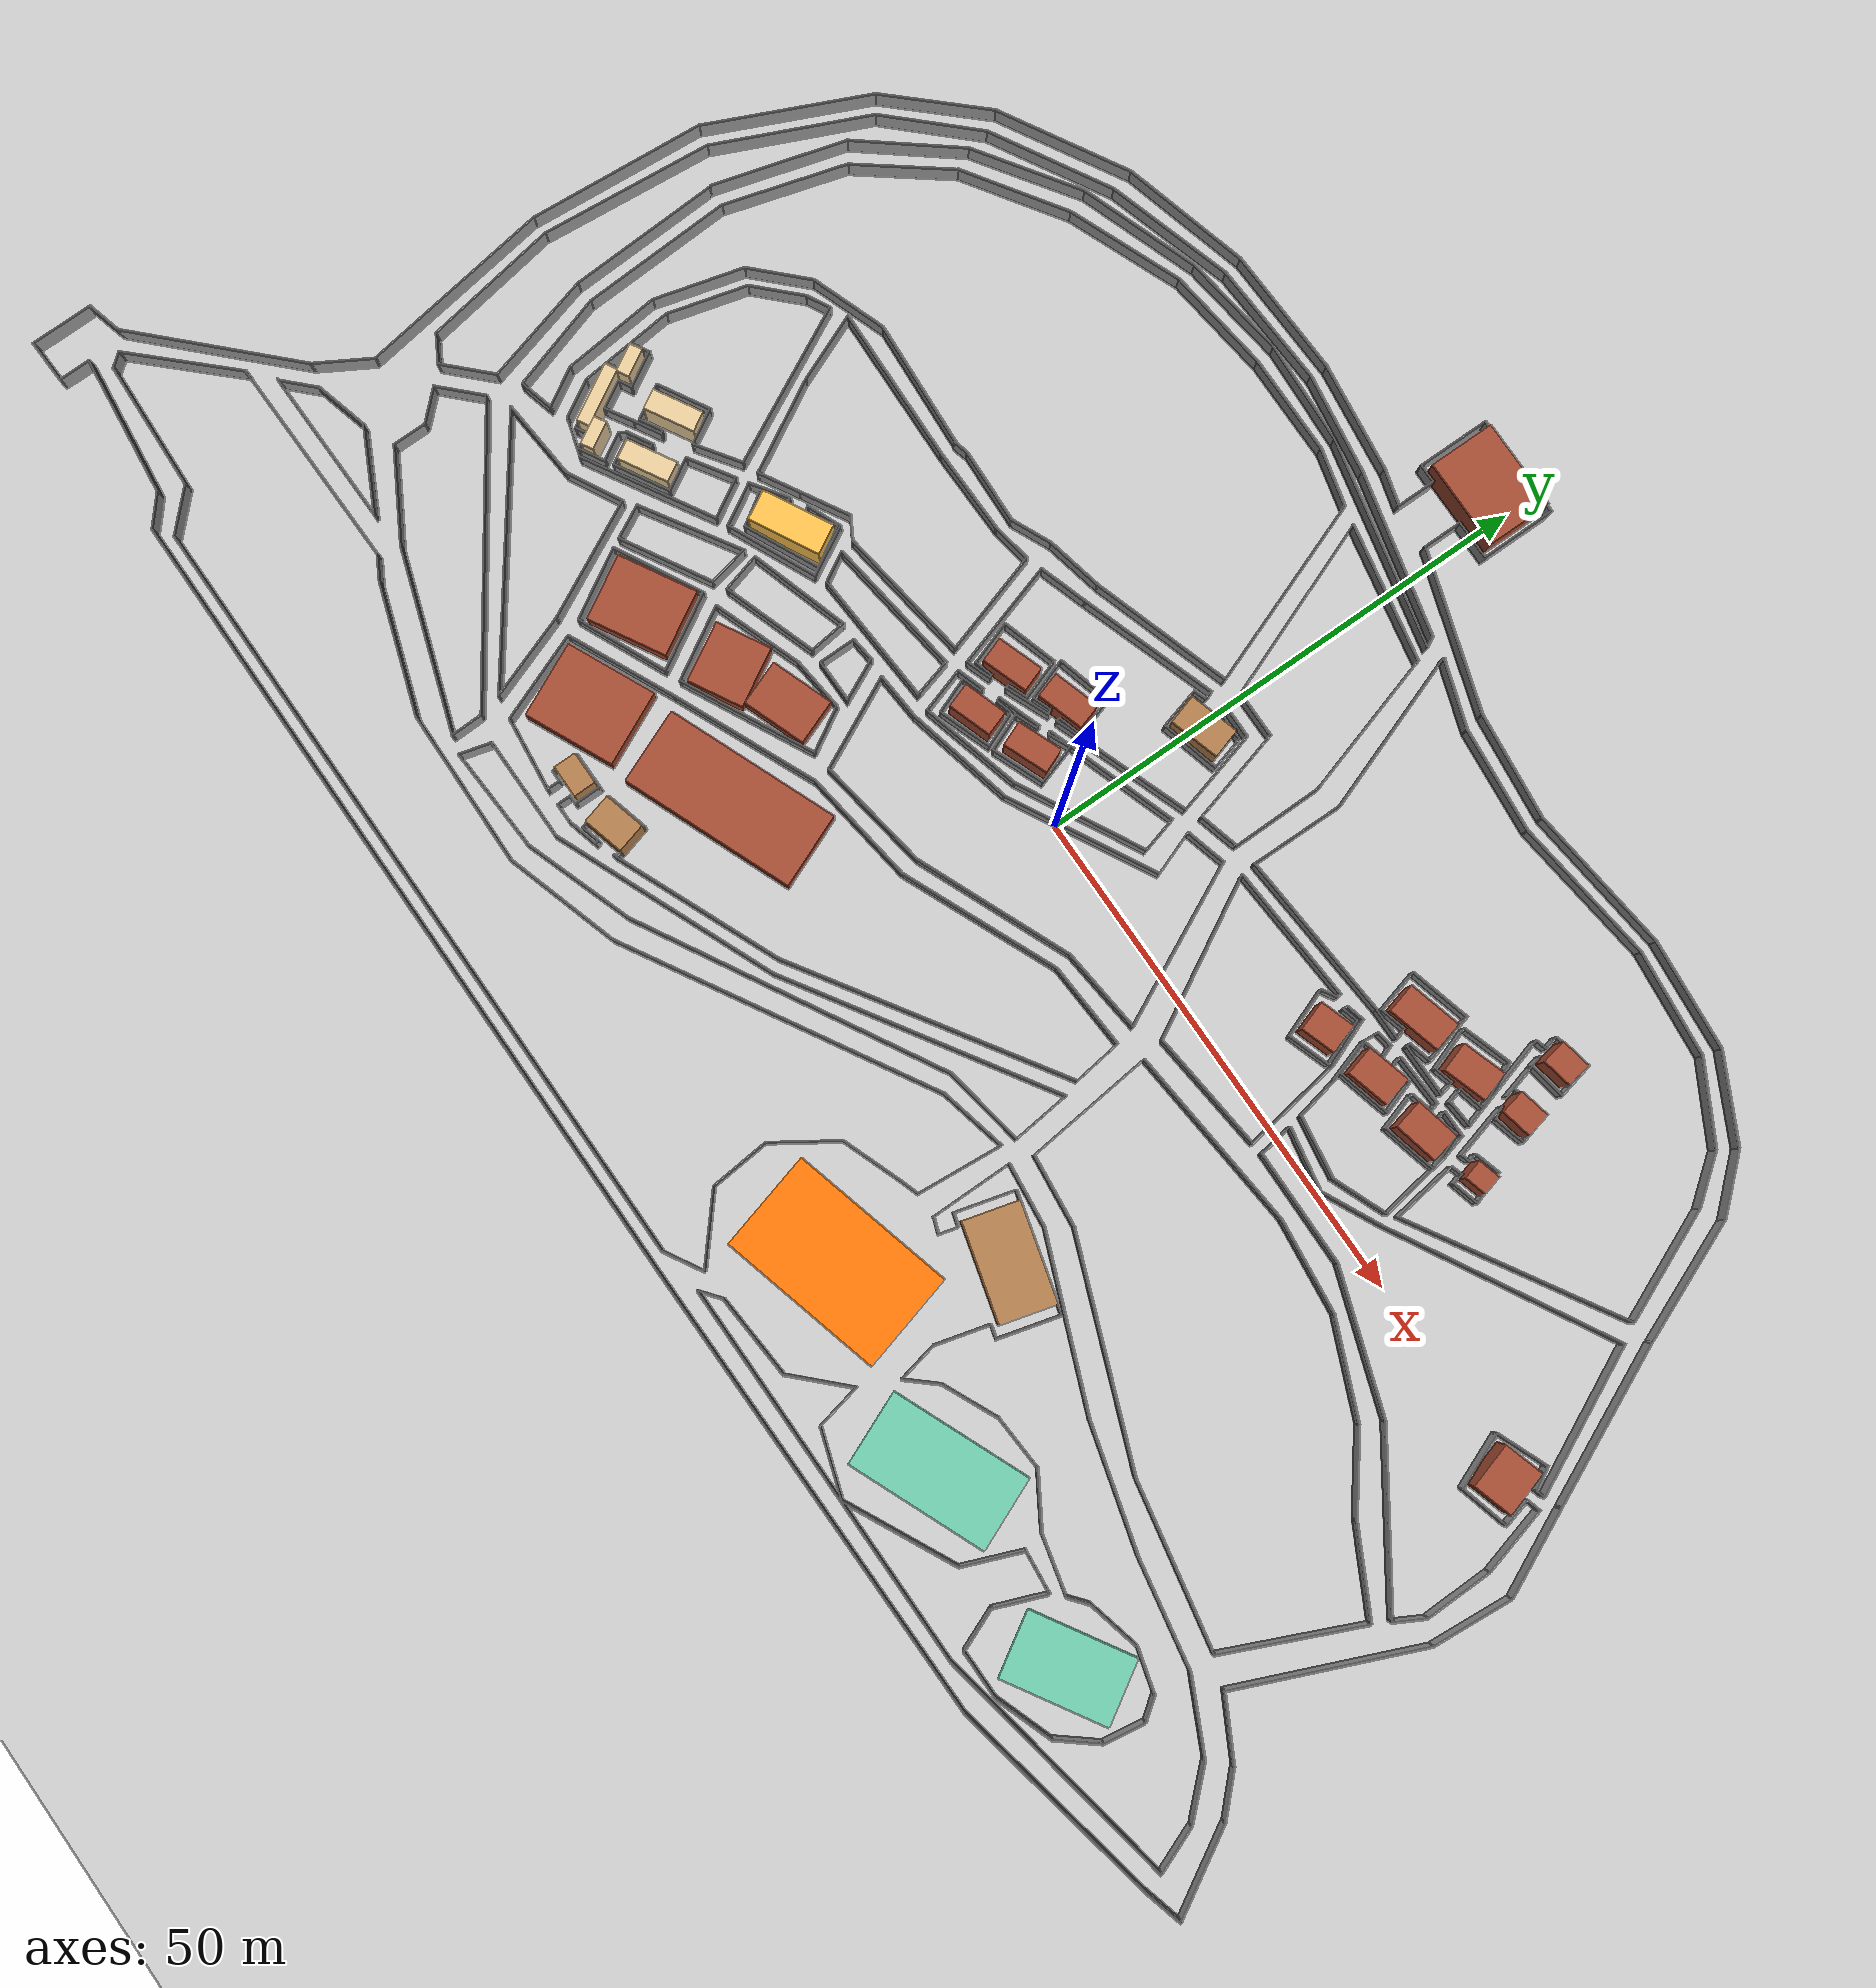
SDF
<sdf version="1.7">
 <world name="default">
  <light name="sun" type="directional">
   <pose>0 0 10 0 -0 0</pose>
   <diffuse>0.8 0.8 0.8 1</diffuse>
   <specular>0.2 0.2 0.2 1</specular>
   <attenuation>
    <range>1000</range>
    <constant>0.9</constant>
    <linear>0.01</linear>
    <quadratic>0.001</quadratic>
   </attenuation>
   <direction>-0.5 0.1 -0.9</direction>
   <spot><inner_angle>0</inner_angle><outer_angle>0</outer_angle><falloff>0</falloff></spot>
  </light>
  <model name="ground_plane">
   <static>1</static>
   <link name="link">
    <collision name="collision">
     <geometry><plane><normal>0 0 1</normal><size>100 100</size></plane></geometry>
     <surface><friction><ode><mu>100</mu><mu2>50</mu2></ode></friction></surface>
    </collision>
    <visual name="visual">
     <cast_shadows>0</cast_shadows>
     <geometry><plane><normal>0 0 1</normal><size>100 100</size></plane></geometry>
     <material>
      <script><uri>file://media/materials/scripts/gazebo.material</uri><name>Gazebo/Grey</name></script>
     </material>
    </visual>
   </link>
  </model>
  <model name="final_max_v1">
   <pose>-2.52311 0.689104 0 0 -0 0</pose>
   <link name="Wall_0">
    <collision name="Wall_0_Collision">
     <geometry><box><size>6.25 0.15 2.5</size></box></geometry>
     <pose>0 0 1.25 0 -0 0</pose>
    </collision>
    <visual name="Wall_0_Visual">
     <pose>0 0 1.25 0 -0 0</pose>
     <geometry><box><size>6.25 0.15 2.5</size></box></geometry>
     <material>
      <script><uri>file://media/materials/scripts/gazebo.material</uri><name>Gazebo/Grey</name></script>
      <ambient>1 1 1 1</ambient>
     </material>
     <meta><layer>0</layer></meta>
    </visual>
    <pose>-86.0864 -48.4326 0 0 -0 1.5708</pose>
   </link>
   <link name="Wall_100">
    <collision name="Wall_100_Collision">
     <geometry><box><size>19.4552 0.15 2.5</size></box></geometry>
     <pose>0 0 1.25 0 -0 0</pose>
    </collision>
    <visual name="Wall_100_Visual">
     <pose>0 0 1.25 0 -0 0</pose>
     <geometry><box><size>19.4552 0.15 2.5</size></box></geometry>
     <material>
      <script><uri>file://media/materials/scripts/gazebo.material</uri><name>Gazebo/Grey</name></script>
      <ambient>1 1 1 1</ambient>
     </material>
     <meta><layer>0</layer></meta>
    </visual>
    <pose>-68.6774 -17.2731 0 0 -0 1.7136</pose>
   </link>
   <link name="Wall_101">
    <collision name="Wall_101_Collision">
     <geometry><box><size>17.4551 0.15 2.5</size></box></geometry>
     <pose>0 0 1.25 0 -0 0</pose>
    </collision>
    <visual name="Wall_101_Visual">
     <pose>0 0 1.25 0 -0 0</pose>
     <geometry><box><size>17.4551 0.15 2.5</size></box></geometry>
     <material>
      <script><uri>file://media/materials/scripts/gazebo.material</uri><name>Gazebo/Grey</name></script>
      <ambient>1 1 1 1</ambient>
     </material>
     <meta><layer>0</layer></meta>
    </visual>
    <pose>-69.3611 0.906246 0 0 -0 1.49097</pose>
   </link>
   <link name="Wall_102">
    <collision name="Wall_102_Collision">
     <geometry><box><size>16.5473 0.15 2.5</size></box></geometry>
     <pose>0 0 1.25 0 -0 0</pose>
    </collision>
    <visual name="Wall_102_Visual">
     <pose>0 0 1.25 0 -0 0</pose>
     <geometry><box><size>16.5473 0.15 2.5</size></box></geometry>
     <material>
      <script><uri>file://media/materials/scripts/gazebo.material</uri><name>Gazebo/Grey</name></script>
      <ambient>1 1 1 1</ambient>
     </material>
     <meta><layer>0</layer></meta>
    </visual>
    <pose>-65.3062 17.0076 0 0 -0 1.14788</pose>
   </link>
   <link name="Wall_103">
    <collision name="Wall_103_Collision">
     <geometry><box><size>11.1751 0.15 2.5</size></box></geometry>
     <pose>0 0 1.25 0 -0 0</pose>
    </collision>
    <visual name="Wall_103_Visual">
     <pose>0 0 1.25 0 -0 0</pose>
     <geometry><box><size>11.1751 0.15 2.5</size></box></geometry>
     <material>
      <script><uri>file://media/materials/scripts/gazebo.material</uri><name>Gazebo/Grey</name></script>
      <ambient>1 1 1 1</ambient>
     </material>
     <meta><layer>0</layer></meta>
    </visual>
    <pose>-58.1953 28.5281 0 0 -0 0.823656</pose>
   </link>
   <link name="Wall_104">
    <collision name="Wall_104_Collision">
     <geometry><box><size>13.75 0.15 2.5</size></box></geometry>
     <pose>0 0 1.25 0 -0 0</pose>
    </collision>
    <visual name="Wall_104_Visual">
     <pose>0 0 1.25 0 -0 0</pose>
     <geometry><box><size>13.75 0.15 2.5</size></box></geometry>
     <material>
      <script><uri>file://media/materials/scripts/gazebo.material</uri><name>Gazebo/Grey</name></script>
      <ambient>1 1 1 1</ambient>
     </material>
     <meta><layer>0</layer></meta>
    </visual>
    <pose>-48.5603 35.9723 0 0 -0 0.523599</pose>
   </link>
   <link name="Wall_105">
    <collision name="Wall_105_Collision">
     <geometry><box><size>12.9786 0.15 2.5</size></box></geometry>
     <pose>0 0 1.25 0 -0 0</pose>
    </collision>
    <visual name="Wall_105_Visual">
     <pose>0 0 1.25 0 -0 0</pose>
     <geometry><box><size>12.9786 0.15 2.5</size></box></geometry>
     <material>
      <script><uri>file://media/materials/scripts/gazebo.material</uri><name>Gazebo/Grey</name></script>
      <ambient>1 1 1 1</ambient>
     </material>
     <meta><layer>0</layer></meta>
    </visual>
    <pose>-36.4883 41.0795 0 0 -0 0.269405</pose>
   </link>
   <link name="Wall_106">
    <collision name="Wall_106_Collision">
     <geometry><box><size>12.8269 0.15 2.5</size></box></geometry>
     <pose>0 0 1.25 0 -0 0</pose>
    </collision>
    <visual name="Wall_106_Visual">
     <pose>0 0 1.25 0 -0 0</pose>
     <geometry><box><size>12.8269 0.15 2.5</size></box></geometry>
     <material>
      <script><uri>file://media/materials/scripts/gazebo.material</uri><name>Gazebo/Grey</name></script>
      <ambient>1 1 1 1</ambient>
     </material>
     <meta><layer>0</layer></meta>
    </visual>
    <pose>-23.9732 43.0681 0 0 -0 0.044415</pose>
   </link>
   <link name="Wall_107">
    <collision name="Wall_107_Collision">
     <geometry><box><size>10.9191 0.15 2.5</size></box></geometry>
     <pose>0 0 1.25 0 -0 0</pose>
    </collision>
    <visual name="Wall_107_Visual">
     <pose>0 0 1.25 0 -0 0</pose>
     <geometry><box><size>10.9191 0.15 2.5</size></box></geometry>
     <material>
      <script><uri>file://media/materials/scripts/gazebo.material</uri><name>Gazebo/Grey</name></script>
      <ambient>1 1 1 1</ambient>
     </material>
     <meta><layer>0</layer></meta>
    </visual>
    <pose>-12.2939 42.7164 0 0 -0 -0.117872</pose>
   </link>
   <link name="Wall_111">
    <collision name="Wall_111_Collision">
     <geometry><box><size>3.75 0.15 2.5</size></box></geometry>
     <pose>0 0 1.25 0 -0 0</pose>
    </collision>
    <visual name="Wall_111_Visual">
     <pose>0 0 1.25 0 -0 0</pose>
     <geometry><box><size>3.75 0.15 2.5</size></box></geometry>
     <material>
      <script><uri>file://media/materials/scripts/gazebo.material</uri><name>Gazebo/Grey</name></script>
      <ambient>1 1 1 1</ambient>
     </material>
     <meta><layer>0</layer></meta>
    </visual>
    <pose>-5.20804 41.6173 0 0 -0 -0.261799</pose>
   </link>
   <link name="Wall_112">
    <collision name="Wall_112_Collision">
     <geometry><box><size>4 0.15 2.5</size></box></geometry>
     <pose>0 0 1.25 0 -0 0</pose>
    </collision>
    <visual name="Wall_112_Visual">
     <pose>0 0 1.25 0 -0 0</pose>
     <geometry><box><size>4 0.15 2.5</size></box></geometry>
     <material>
      <script><uri>file://media/materials/scripts/gazebo.material</uri><name>Gazebo/Grey</name></script>
      <ambient>1 1 1 1</ambient>
     </material>
     <meta><layer>0</layer></meta>
    </visual>
    <pose>-3.46937 43.0764 0 0 -0 1.5708</pose>
   </link>
   <link name="Wall_113">
    <collision name="Wall_113_Collision">
     <geometry><box><size>2 0.15 2.5</size></box></geometry>
     <pose>0 0 1.25 0 -0 0</pose>
    </collision>
    <visual name="Wall_113_Visual">
     <pose>0 0 1.25 0 -0 0</pose>
     <geometry><box><size>2 0.15 2.5</size></box></geometry>
     <material>
      <script><uri>file://media/materials/scripts/gazebo.material</uri><name>Gazebo/Grey</name></script>
      <ambient>1 1 1 1</ambient>
     </material>
     <meta><layer>0</layer></meta>
    </visual>
    <pose>-4.39437 45.0014 0 0 -0 3.14159</pose>
   </link>
   <link name="Wall_114">
    <collision name="Wall_114_Collision">
     <geometry><box><size>7.25 0.15 2.5</size></box></geometry>
     <pose>0 0 1.25 0 -0 0</pose>
    </collision>
    <visual name="Wall_114_Visual">
     <pose>0 0 1.25 0 -0 0</pose>
     <geometry><box><size>7.25 0.15 2.5</size></box></geometry>
     <material>
      <script><uri>file://media/materials/scripts/gazebo.material</uri><name>Gazebo/Grey</name></script>
      <ambient>1 1 1 1</ambient>
     </material>
     <meta><layer>0</layer></meta>
    </visual>
    <pose>-5.31937 48.5514 0 0 -0 1.5708</pose>
   </link>
   <link name="Wall_115">
    <collision name="Wall_115_Collision">
     <geometry><box><size>10.25 0.15 2.5</size></box></geometry>
     <pose>0 0 1.25 0 -0 0</pose>
    </collision>
    <visual name="Wall_115_Visual">
     <pose>0 0 1.25 0 -0 0</pose>
     <geometry><box><size>10.25 0.15 2.5</size></box></geometry>
     <material>
      <script><uri>file://media/materials/scripts/gazebo.material</uri><name>Gazebo/Grey</name></script>
      <ambient>1 1 1 1</ambient>
     </material>
     <meta><layer>0</layer></meta>
    </visual>
    <pose>-0.269373 52.1014 0 0 -0 0</pose>
   </link>
   <link name="Wall_116">
    <collision name="Wall_116_Collision">
     <geometry><box><size>7.5 0.15 2.5</size></box></geometry>
     <pose>0 0 1.25 0 -0 0</pose>
    </collision>
    <visual name="Wall_116_Visual">
     <pose>0 0 1.25 0 -0 0</pose>
     <geometry><box><size>7.5 0.15 2.5</size></box></geometry>
     <material>
      <script><uri>file://media/materials/scripts/gazebo.material</uri><name>Gazebo/Grey</name></script>
      <ambient>1 1 1 1</ambient>
     </material>
     <meta><layer>0</layer></meta>
    </visual>
    <pose>4.78063 48.4264 0 0 -0 -1.5708</pose>
   </link>
   <link name="Wall_117">
    <collision name="Wall_117_Collision">
     <geometry><box><size>4 0.15 2.5</size></box></geometry>
     <pose>0 0 1.25 0 -0 0</pose>
    </collision>
    <visual name="Wall_117_Visual">
     <pose>0 0 1.25 0 -0 0</pose>
     <geometry><box><size>4 0.15 2.5</size></box></geometry>
     <material>
      <script><uri>file://media/materials/scripts/gazebo.material</uri><name>Gazebo/Grey</name></script>
      <ambient>1 1 1 1</ambient>
     </material>
     <meta><layer>0</layer></meta>
    </visual>
    <pose>2.85563 44.7514 0 0 -0 3.14159</pose>
   </link>
   <link name="Wall_118">
    <collision name="Wall_118_Collision">
     <geometry><box><size>4 0.15 2.5</size></box></geometry>
     <pose>0 0 1.25 0 -0 0</pose>
    </collision>
    <visual name="Wall_118_Visual">
     <pose>0 0 1.25 0 -0 0</pose>
     <geometry><box><size>4 0.15 2.5</size></box></geometry>
     <material>
      <script><uri>file://media/materials/scripts/gazebo.material</uri><name>Gazebo/Grey</name></script>
      <ambient>1 1 1 1</ambient>
     </material>
     <meta><layer>0</layer></meta>
    </visual>
    <pose>0.930627 42.8264 0 0 -0 -1.5708</pose>
   </link>
   <link name="Wall_119">
    <collision name="Wall_119_Collision">
     <geometry><box><size>16.165 0.15 2.5</size></box></geometry>
     <pose>0 0 1.25 0 -0 0</pose>
    </collision>
    <visual name="Wall_119_Visual">
     <pose>0 0 1.25 0 -0 0</pose>
     <geometry><box><size>16.165 0.15 2.5</size></box></geometry>
     <material>
      <script><uri>file://media/materials/scripts/gazebo.material</uri><name>Gazebo/Grey</name></script>
      <ambient>1 1 1 1</ambient>
     </material>
     <meta><layer>0</layer></meta>
    </visual>
    <pose>8.5693 38.4991 0 0 -0 -0.304697</pose>
   </link>
   <link name="Wall_12">
    <collision name="Wall_12_Collision">
     <geometry><box><size>4.71285 0.15 2.5</size></box></geometry>
     <pose>0 0 1.25 0 -0 0</pose>
    </collision>
    <visual name="Wall_12_Visual">
     <pose>0 0 1.25 0 -0 0</pose>
     <geometry><box><size>4.71285 0.15 2.5</size></box></geometry>
     <material>
      <script><uri>file://media/materials/scripts/gazebo.material</uri><name>Gazebo/Grey</name></script>
      <ambient>1 1 1 1</ambient>
     </material>
     <meta><layer>0</layer></meta>
    </visual>
    <pose>33.7028 -45.8078 0 0 -0 -1.36194</pose>
   </link>
   <link name="Wall_120">
    <collision name="Wall_120_Collision">
     <geometry><box><size>10.7874 0.15 2.5</size></box></geometry>
     <pose>0 0 1.25 0 -0 0</pose>
    </collision>
    <visual name="Wall_120_Visual">
     <pose>0 0 1.25 0 -0 0</pose>
     <geometry><box><size>10.7874 0.15 2.5</size></box></geometry>
     <material>
      <script><uri>file://media/materials/scripts/gazebo.material</uri><name>Gazebo/Grey</name></script>
      <ambient>1 1 1 1</ambient>
     </material>
     <meta><layer>0</layer></meta>
    </visual>
    <pose>21.498 35.5448 0 0 -0 -0.103972</pose>
   </link>
   <link name="Wall_121">
    <collision name="Wall_121_Collision">
     <geometry><box><size>14.8821 0.15 2.5</size></box></geometry>
     <pose>0 0 1.25 0 -0 0</pose>
    </collision>
    <visual name="Wall_121_Visual">
     <pose>0 0 1.25 0 -0 0</pose>
     <geometry><box><size>14.8821 0.15 2.5</size></box></geometry>
     <material>
      <script><uri>file://media/materials/scripts/gazebo.material</uri><name>Gazebo/Grey</name></script>
      <ambient>1 1 1 1</ambient>
     </material>
     <meta><layer>0</layer></meta>
    </visual>
    <pose>34.102 35.8668 0 0 -0 0.118933</pose>
   </link>
   <link name="Wall_122">
    <collision name="Wall_122_Collision">
     <geometry><box><size>11.1366 0.15 2.5</size></box></geometry>
     <pose>0 0 1.25 0 -0 0</pose>
    </collision>
    <visual name="Wall_122_Visual">
     <pose>0 0 1.25 0 -0 0</pose>
     <geometry><box><size>11.1366 0.15 2.5</size></box></geometry>
     <material>
      <script><uri>file://media/materials/scripts/gazebo.material</uri><name>Gazebo/Grey</name></script>
      <ambient>1 1 1 1</ambient>
     </material>
     <meta><layer>0</layer></meta>
    </visual>
    <pose>46.89 36.2808 0 0 -0 -0.083837</pose>
   </link>
   <link name="Wall_123">
    <collision name="Wall_123_Collision">
     <geometry><box><size>8.99588 0.15 2.5</size></box></geometry>
     <pose>0 0 1.25 0 -0 0</pose>
    </collision>
    <visual name="Wall_123_Visual">
     <pose>0 0 1.25 0 -0 0</pose>
     <geometry><box><size>8.99588 0.15 2.5</size></box></geometry>
     <material>
      <script><uri>file://media/materials/scripts/gazebo.material</uri><name>Gazebo/Grey</name></script>
      <ambient>1 1 1 1</ambient>
     </material>
     <meta><layer>0</layer></meta>
    </visual>
    <pose>56.32 33.8428 0 0 -0 -0.463648</pose>
   </link>
   <link name="Wall_124">
    <collision name="Wall_124_Collision">
     <geometry><box><size>6.5786 0.15 2.5</size></box></geometry>
     <pose>0 0 1.25 0 -0 0</pose>
    </collision>
    <visual name="Wall_124_Visual">
     <pose>0 0 1.25 0 -0 0</pose>
     <geometry><box><size>6.5786 0.15 2.5</size></box></geometry>
     <material>
      <script><uri>file://media/materials/scripts/gazebo.material</uri><name>Gazebo/Grey</name></script>
      <ambient>1 1 1 1</ambient>
     </material>
     <meta><layer>0</layer></meta>
    </visual>
    <pose>62.4457 29.4933 0 0 -0 -0.829799</pose>
   </link>
   <link name="Wall_126">
    <collision name="Wall_126_Collision">
     <geometry><box><size>3.75 0.15 2.5</size></box></geometry>
     <pose>0 0 1.25 0 -0 0</pose>
    </collision>
    <visual name="Wall_126_Visual">
     <pose>0 0 1.25 0 -0 0</pose>
     <geometry><box><size>3.75 0.15 2.5</size></box></geometry>
     <material>
      <script><uri>file://media/materials/scripts/gazebo.material</uri><name>Gazebo/Grey</name></script>
      <ambient>1 1 1 1</ambient>
     </material>
     <meta><layer>0</layer></meta>
    </visual>
    <pose>-69.2284 -33.7829 0 0 -0 0.785398</pose>
   </link>
   <link name="Wall_127">
    <collision name="Wall_127_Collision">
     <geometry><box><size>5.5 0.15 2.5</size></box></geometry>
     <pose>0 0 1.25 0 -0 0</pose>
    </collision>
    <visual name="Wall_127_Visual">
     <pose>0 0 1.25 0 -0 0</pose>
     <geometry><box><size>5.5 0.15 2.5</size></box></geometry>
     <material>
      <script><uri>file://media/materials/scripts/gazebo.material</uri><name>Gazebo/Grey</name></script>
      <ambient>1 1 1 1</ambient>
     </material>
     <meta><layer>0</layer></meta>
    </visual>
    <pose>-65.3717 -31.8178 0 0 -0 0.261799</pose>
   </link>
   <link name="Wall_128">
    <collision name="Wall_128_Collision">
     <geometry><box><size>8.46258 0.15 2.5</size></box></geometry>
     <pose>0 0 1.25 0 -0 0</pose>
    </collision>
    <visual name="Wall_128_Visual">
     <pose>0 0 1.25 0 -0 0</pose>
     <geometry><box><size>8.46258 0.15 2.5</size></box></geometry>
     <material>
      <script><uri>file://media/materials/scripts/gazebo.material</uri><name>Gazebo/Grey</name></script>
      <ambient>1 1 1 1</ambient>
     </material>
     <meta><layer>0</layer></meta>
    </visual>
    <pose>-59.0888 -33.0206 0 0 -0 -0.47347</pose>
   </link>
   <link name="Wall_129">
    <collision name="Wall_129_Collision">
     <geometry><box><size>15.488 0.15 2.5</size></box></geometry>
     <pose>0 0 1.25 0 -0 0</pose>
    </collision>
    <visual name="Wall_129_Visual">
     <pose>0 0 1.25 0 -0 0</pose>
     <geometry><box><size>15.488 0.15 2.5</size></box></geometry>
     <material>
      <script><uri>file://media/materials/scripts/gazebo.material</uri><name>Gazebo/Grey</name></script>
      <ambient>1 1 1 1</ambient>
     </material>
     <meta><layer>0</layer></meta>
    </visual>
    <pose>-63.0581 -35.0458 0 0 -0 -3.12463</pose>
   </link>
   <link name="Wall_13">
    <collision name="Wall_13_Collision">
     <geometry><box><size>6.84861 0.15 2.5</size></box></geometry>
     <pose>0 0 1.25 0 -0 0</pose>
    </collision>
    <visual name="Wall_13_Visual">
     <pose>0 0 1.25 0 -0 0</pose>
     <geometry><box><size>6.84861 0.15 2.5</size></box></geometry>
     <material>
      <script><uri>file://media/materials/scripts/gazebo.material</uri><name>Gazebo/Grey</name></script>
      <ambient>1 1 1 1</ambient>
     </material>
     <meta><layer>0</layer></meta>
    </visual>
    <pose>37.3584 -49.0831 0 0 -0 -0.316824</pose>
   </link>
   <link name="Wall_131">
    <collision name="Wall_131_Collision">
     <geometry><box><size>16.551 0.15 2.5</size></box></geometry>
     <pose>0 0 1.25 0 -0 0</pose>
    </collision>
    <visual name="Wall_131_Visual">
     <pose>0 0 1.25 0 -0 0</pose>
     <geometry><box><size>16.551 0.15 2.5</size></box></geometry>
     <material>
      <script><uri>file://media/materials/scripts/gazebo.material</uri><name>Gazebo/Grey</name></script>
      <ambient>1 1 1 1</ambient>
     </material>
     <meta><layer>0</layer></meta>
    </visual>
    <pose>61.4597 -29.6539 0 0 -0 2.9497</pose>
   </link>
   <link name="Wall_132">
    <collision name="Wall_132_Collision">
     <geometry><box><size>22.4626 0.15 2.5</size></box></geometry>
     <pose>0 0 1.25 0 -0 0</pose>
    </collision>
    <visual name="Wall_132_Visual">
     <pose>0 0 1.25 0 -0 0</pose>
     <geometry><box><size>22.4626 0.15 2.5</size></box></geometry>
     <material>
      <script><uri>file://media/materials/scripts/gazebo.material</uri><name>Gazebo/Grey</name></script>
      <ambient>1 1 1 1</ambient>
     </material>
     <meta><layer>0</layer></meta>
    </visual>
    <pose>43.0137 -24.0419 0 0 -0 2.77027</pose>
   </link>
   <link name="Wall_133">
    <collision name="Wall_133_Collision">
     <geometry><box><size>7.27213 0.15 2.5</size></box></geometry>
     <pose>0 0 1.25 0 -0 0</pose>
    </collision>
    <visual name="Wall_133_Visual">
     <pose>0 0 1.25 0 -0 0</pose>
     <geometry><box><size>7.27213 0.15 2.5</size></box></geometry>
     <material>
      <script><uri>file://media/materials/scripts/gazebo.material</uri><name>Gazebo/Grey</name></script>
      <ambient>1 1 1 1</ambient>
     </material>
     <meta><layer>0</layer></meta>
    </visual>
    <pose>29.0757 -19.6259 0 0 -0 3.03807</pose>
   </link>
   <link name="Wall_134">
    <collision name="Wall_134_Collision">
     <geometry><box><size>13.0122 0.15 2.5</size></box></geometry>
     <pose>0 0 1.25 0 -0 0</pose>
    </collision>
    <visual name="Wall_134_Visual">
     <pose>0 0 1.25 0 -0 0</pose>
     <geometry><box><size>13.0122 0.15 2.5</size></box></geometry>
     <material>
      <script><uri>file://media/materials/scripts/gazebo.material</uri><name>Gazebo/Grey</name></script>
      <ambient>1 1 1 1</ambient>
     </material>
     <meta><layer>0</layer></meta>
    </visual>
    <pose>24.8437 -12.8639 0 0 -0 1.67829</pose>
   </link>
   <link name="Wall_135">
    <collision name="Wall_135_Collision">
     <geometry><box><size>18.5413 0.15 2.5</size></box></geometry>
     <pose>0 0 1.25 0 -0 0</pose>
    </collision>
    <visual name="Wall_135_Visual">
     <pose>0 0 1.25 0 -0 0</pose>
     <geometry><box><size>18.5413 0.15 2.5</size></box></geometry>
     <material>
      <script><uri>file://media/materials/scripts/gazebo.material</uri><name>Gazebo/Grey</name></script>
      <ambient>1 1 1 1</ambient>
     </material>
     <meta><layer>0</layer></meta>
    </visual>
    <pose>33.3077 -5.59592 0 0 -0 0.095189</pose>
   </link>
   <link name="Wall_136">
    <collision name="Wall_136_Collision">
     <geometry><box><size>9.49695 0.15 2.5</size></box></geometry>
     <pose>0 0 1.25 0 -0 0</pose>
    </collision>
    <visual name="Wall_136_Visual">
     <pose>0 0 1.25 0 -0 0</pose>
     <geometry><box><size>9.49695 0.15 2.5</size></box></geometry>
     <material>
      <script><uri>file://media/materials/scripts/gazebo.material</uri><name>Gazebo/Grey</name></script>
      <ambient>1 1 1 1</ambient>
     </material>
     <meta><layer>0</layer></meta>
    </visual>
    <pose>47.1077 -5.22792 0 0 -0 -0.108483</pose>
   </link>
   <link name="Wall_137">
    <collision name="Wall_137_Collision">
     <geometry><box><size>9.83843 0.15 2.5</size></box></geometry>
     <pose>0 0 1.25 0 -0 0</pose>
    </collision>
    <visual name="Wall_137_Visual">
     <pose>0 0 1.25 0 -0 0</pose>
     <geometry><box><size>9.83843 0.15 2.5</size></box></geometry>
     <material>
      <script><uri>file://media/materials/scripts/gazebo.material</uri><name>Gazebo/Grey</name></script>
      <ambient>1 1 1 1</ambient>
     </material>
     <meta><layer>0</layer></meta>
    </visual>
    <pose>56.2157 -7.61992 0 0 -0 -0.399904</pose>
   </link>
   <link name="Wall_138">
    <collision name="Wall_138_Collision">
     <geometry><box><size>8.35659 0.15 2.5</size></box></geometry>
     <pose>0 0 1.25 0 -0 0</pose>
    </collision>
    <visual name="Wall_138_Visual">
     <pose>0 0 1.25 0 -0 0</pose>
     <geometry><box><size>8.35659 0.15 2.5</size></box></geometry>
     <material>
      <script><uri>file://media/materials/scripts/gazebo.material</uri><name>Gazebo/Grey</name></script>
      <ambient>1 1 1 1</ambient>
     </material>
     <meta><layer>0</layer></meta>
    </visual>
    <pose>63.9437 -11.9899 0 0 -0 -0.650227</pose>
   </link>
   <link name="Wall_139">
    <collision name="Wall_139_Collision">
     <geometry><box><size>9.07969 0.15 2.5</size></box></geometry>
     <pose>0 0 1.25 0 -0 0</pose>
    </collision>
    <visual name="Wall_139_Visual">
     <pose>0 0 1.25 0 -0 0</pose>
     <geometry><box><size>9.07969 0.15 2.5</size></box></geometry>
     <material>
      <script><uri>file://media/materials/scripts/gazebo.material</uri><name>Gazebo/Grey</name></script>
      <ambient>1 1 1 1</ambient>
     </material>
     <meta><layer>0</layer></meta>
    </visual>
    <pose>71.1657 -16.5439 0 0 -0 -0.482079</pose>
   </link>
   <link name="Wall_14">
    <collision name="Wall_14_Collision">
     <geometry><box><size>11.6765 0.15 2.5</size></box></geometry>
     <pose>0 0 1.25 0 -0 0</pose>
    </collision>
    <visual name="Wall_14_Visual">
     <pose>0 0 1.25 0 -0 0</pose>
     <geometry><box><size>11.6765 0.15 2.5</size></box></geometry>
     <material>
      <script><uri>file://media/materials/scripts/gazebo.material</uri><name>Gazebo/Grey</name></script>
      <ambient>1 1 1 1</ambient>
     </material>
     <meta><layer>0</layer></meta>
    </visual>
    <pose>45.7063 -47.5701 0 0 -0 0.459599</pose>
   </link>
   <link name="Wall_140">
    <collision name="Wall_140_Collision">
     <geometry><box><size>13.9469 0.15 2.5</size></box></geometry>
     <pose>0 0 1.25 0 -0 0</pose>
    </collision>
    <visual name="Wall_140_Visual">
     <pose>0 0 1.25 0 -0 0</pose>
     <geometry><box><size>13.9469 0.15 2.5</size></box></geometry>
     <material>
      <script><uri>file://media/materials/scripts/gazebo.material</uri><name>Gazebo/Grey</name></script>
      <ambient>1 1 1 1</ambient>
     </material>
     <meta><layer>0</layer></meta>
    </visual>
    <pose>72.3157 -24.9159 0 0 -0 -1.9897</pose>
   </link>
   <link name="Wall_142">
    <collision name="Wall_142_Collision">
     <geometry><box><size>3 0.15 2.5</size></box></geometry>
     <pose>0 0 1.25 0 -0 0</pose>
    </collision>
    <visual name="Wall_142_Visual">
     <pose>0 0 1.25 0 -0 0</pose>
     <geometry><box><size>3 0.15 2.5</size></box></geometry>
     <material>
      <script><uri>file://media/materials/scripts/gazebo.material</uri><name>Gazebo/Grey</name></script>
      <ambient>1 1 1 1</ambient>
     </material>
     <meta><layer>0</layer></meta>
    </visual>
    <pose>-64.8763 -21.7565 0 0 -0 2.61799</pose>
   </link>
   <link name="Wall_143">
    <collision name="Wall_143_Collision">
     <geometry><box><size>13.7057 0.15 2.5</size></box></geometry>
     <pose>0 0 1.25 0 -0 0</pose>
    </collision>
    <visual name="Wall_143_Visual">
     <pose>0 0 1.25 0 -0 0</pose>
     <geometry><box><size>13.7057 0.15 2.5</size></box></geometry>
     <material>
      <script><uri>file://media/materials/scripts/gazebo.material</uri><name>Gazebo/Grey</name></script>
      <ambient>1 1 1 1</ambient>
     </material>
     <meta><layer>0</layer></meta>
    </visual>
    <pose>-67.1763 -14.3505 0 0 -0 1.72872</pose>
   </link>
   <link name="Wall_145">
    <collision name="Wall_145_Collision">
     <geometry><box><size>16.9669 0.15 2.5</size></box></geometry>
     <pose>0 0 1.25 0 -0 0</pose>
    </collision>
    <visual name="Wall_145_Visual">
     <pose>0 0 1.25 0 -0 0</pose>
     <geometry><box><size>16.9669 0.15 2.5</size></box></geometry>
     <material>
      <script><uri>file://media/materials/scripts/gazebo.material</uri><name>Gazebo/Grey</name></script>
      <ambient>1 1 1 1</ambient>
     </material>
     <meta><layer>0</layer></meta>
    </visual>
    <pose>-67.4602 0.714958 0 0 -0 1.47766</pose>
   </link>
   <link name="Wall_147">
    <collision name="Wall_147_Collision">
     <geometry><box><size>15.7591 0.15 2.5</size></box></geometry>
     <pose>0 0 1.25 0 -0 0</pose>
    </collision>
    <visual name="Wall_147_Visual">
     <pose>0 0 1.25 0 -0 0</pose>
     <geometry><box><size>15.7591 0.15 2.5</size></box></geometry>
     <material>
      <script><uri>file://media/materials/scripts/gazebo.material</uri><name>Gazebo/Grey</name></script>
      <ambient>1 1 1 1</ambient>
     </material>
     <meta><layer>0</layer></meta>
    </visual>
    <pose>-63.5042 16.217 0 0 -0 1.15197</pose>
   </link>
   <link name="Wall_149">
    <collision name="Wall_149_Collision">
     <geometry><box><size>10.4318 0.15 2.5</size></box></geometry>
     <pose>0 0 1.25 0 -0 0</pose>
    </collision>
    <visual name="Wall_149_Visual">
     <pose>0 0 1.25 0 -0 0</pose>
     <geometry><box><size>10.4318 0.15 2.5</size></box></geometry>
     <material>
      <script><uri>file://media/materials/scripts/gazebo.material</uri><name>Gazebo/Grey</name></script>
      <ambient>1 1 1 1</ambient>
     </material>
     <meta><layer>0</layer></meta>
    </visual>
    <pose>-56.7882 27.073 0 0 -0 0.810709</pose>
   </link>
   <link name="Wall_15">
    <collision name="Wall_15_Collision">
     <geometry><box><size>6.09874 0.15 2.5</size></box></geometry>
     <pose>0 0 1.25 0 -0 0</pose>
    </collision>
    <visual name="Wall_15_Visual">
     <pose>0 0 1.25 0 -0 0</pose>
     <geometry><box><size>6.09874 0.15 2.5</size></box></geometry>
     <material>
      <script><uri>file://media/materials/scripts/gazebo.material</uri><name>Gazebo/Grey</name></script>
      <ambient>1 1 1 1</ambient>
     </material>
     <meta><layer>0</layer></meta>
    </visual>
    <pose>51.9671 -42.2484 0 0 -0 1.19355</pose>
   </link>
   <link name="Wall_151">
    <collision name="Wall_151_Collision">
     <geometry><box><size>12.8849 0.15 2.5</size></box></geometry>
     <pose>0 0 1.25 0 -0 0</pose>
    </collision>
    <visual name="Wall_151_Visual">
     <pose>0 0 1.25 0 -0 0</pose>
     <geometry><box><size>12.8849 0.15 2.5</size></box></geometry>
     <material>
      <script><uri>file://media/materials/scripts/gazebo.material</uri><name>Gazebo/Grey</name></script>
      <ambient>1 1 1 1</ambient>
     </material>
     <meta><layer>0</layer></meta>
    </visual>
    <pose>-47.7262 33.973 0 0 -0 0.521834</pose>
   </link>
   <link name="Wall_153">
    <collision name="Wall_153_Collision">
     <geometry><box><size>12.9542 0.15 2.5</size></box></geometry>
     <pose>0 0 1.25 0 -0 0</pose>
    </collision>
    <visual name="Wall_153_Visual">
     <pose>0 0 1.25 0 -0 0</pose>
     <geometry><box><size>12.9542 0.15 2.5</size></box></geometry>
     <material>
      <script><uri>file://media/materials/scripts/gazebo.material</uri><name>Gazebo/Grey</name></script>
      <ambient>1 1 1 1</ambient>
     </material>
     <meta><layer>0</layer></meta>
    </visual>
    <pose>-36.0882 39.033 0 0 -0 0.299027</pose>
   </link>
   <link name="Wall_155">
    <collision name="Wall_155_Collision">
     <geometry><box><size>12.4081 0.15 2.5</size></box></geometry>
     <pose>0 0 1.25 0 -0 0</pose>
    </collision>
    <visual name="Wall_155_Visual">
     <pose>0 0 1.25 0 -0 0</pose>
     <geometry><box><size>12.4081 0.15 2.5</size></box></geometry>
     <material>
      <script><uri>file://media/materials/scripts/gazebo.material</uri><name>Gazebo/Grey</name></script>
      <ambient>1 1 1 1</ambient>
     </material>
     <meta><layer>0</layer></meta>
    </visual>
    <pose>-23.8522 41.287 0 0 -0 0.060078</pose>
   </link>
   <link name="Wall_157">
    <collision name="Wall_157_Collision">
     <geometry><box><size>10.2725 0.15 2.5</size></box></geometry>
     <pose>0 0 1.25 0 -0 0</pose>
    </collision>
    <visual name="Wall_157_Visual">
     <pose>0 0 1.25 0 -0 0</pose>
     <geometry><box><size>10.2725 0.15 2.5</size></box></geometry>
     <material>
      <script><uri>file://media/materials/scripts/gazebo.material</uri><name>Gazebo/Grey</name></script>
      <ambient>1 1 1 1</ambient>
     </material>
     <meta><layer>0</layer></meta>
    </visual>
    <pose>-12.7202 40.965 0 0 -0 -0.136756</pose>
   </link>
   <link name="Wall_159">
    <collision name="Wall_159_Collision">
     <geometry><box><size>16.3963 0.15 2.5</size></box></geometry>
     <pose>0 0 1.25 0 -0 0</pose>
    </collision>
    <visual name="Wall_159_Visual">
     <pose>0 0 1.25 0 -0 0</pose>
     <geometry><box><size>16.3963 0.15 2.5</size></box></geometry>
     <material>
      <script><uri>file://media/materials/scripts/gazebo.material</uri><name>Gazebo/Grey</name></script>
      <ambient>1 1 1 1</ambient>
     </material>
     <meta><layer>0</layer></meta>
    </visual>
    <pose>0.113766 38.435 0 0 -0 -0.228497</pose>
   </link>
   <link name="Wall_16">
    <collision name="Wall_16_Collision">
     <geometry><box><size>4.34473 0.15 2.5</size></box></geometry>
     <pose>0 0 1.25 0 -0 0</pose>
    </collision>
    <visual name="Wall_16_Visual">
     <pose>0 0 1.25 0 -0 0</pose>
     <geometry><box><size>4.34473 0.15 2.5</size></box></geometry>
     <material>
      <script><uri>file://media/materials/scripts/gazebo.material</uri><name>Gazebo/Grey</name></script>
      <ambient>1 1 1 1</ambient>
     </material>
     <meta><layer>0</layer></meta>
    </visual>
    <pose>55.1497 -39.6918 0 0 -0 -0.099669</pose>
   </link>
   <link name="Wall_164">
    <collision name="Wall_164_Collision">
     <geometry><box><size>9.16316 0.15 2.5</size></box></geometry>
     <pose>0 0 1.25 0 -0 0</pose>
    </collision>
    <visual name="Wall_164_Visual">
     <pose>0 0 1.25 0 -0 0</pose>
     <geometry><box><size>9.16316 0.15 2.5</size></box></geometry>
     <material>
      <script><uri>file://media/materials/scripts/gazebo.material</uri><name>Gazebo/Grey</name></script>
      <ambient>1 1 1 1</ambient>
     </material>
     <meta><layer>0</layer></meta>
    </visual>
    <pose>13.3066 15.8045 0 0 -0 -1.56262</pose>
   </link>
   <link name="Wall_167">
    <collision name="Wall_167_Collision">
     <geometry><box><size>4 0.15 2.5</size></box></geometry>
     <pose>0 0 1.25 0 -0 0</pose>
    </collision>
    <visual name="Wall_167_Visual">
     <pose>0 0 1.25 0 -0 0</pose>
     <geometry><box><size>4 0.15 2.5</size></box></geometry>
     <material>
      <script><uri>file://media/materials/scripts/gazebo.material</uri><name>Gazebo/Grey</name></script>
      <ambient>1 1 1 1</ambient>
     </material>
     <meta><layer>0</layer></meta>
    </visual>
    <pose>11.3094 10.7013 0 0 -0 0.261799</pose>
   </link>
   <link name="Wall_169">
    <collision name="Wall_169_Collision">
     <geometry><box><size>9.75 0.15 2.5</size></box></geometry>
     <pose>0 0 1.25 0 -0 0</pose>
    </collision>
    <visual name="Wall_169_Visual">
     <pose>0 0 1.25 0 -0 0</pose>
     <geometry><box><size>9.75 0.15 2.5</size></box></geometry>
     <material>
      <script><uri>file://media/materials/scripts/gazebo.material</uri><name>Gazebo/Grey</name></script>
      <ambient>1 1 1 1</ambient>
     </material>
     <meta><layer>0</layer></meta>
    </visual>
    <pose>8.20764 14.8395 0 0 -0 1.8326</pose>
   </link>
   <link name="Wall_17">
    <collision name="Wall_17_Collision">
     <geometry><box><size>5.3044 0.15 2.5</size></box></geometry>
     <pose>0 0 1.25 0 -0 0</pose>
    </collision>
    <visual name="Wall_17_Visual">
     <pose>0 0 1.25 0 -0 0</pose>
     <geometry><box><size>5.3044 0.15 2.5</size></box></geometry>
     <material>
      <script><uri>file://media/materials/scripts/gazebo.material</uri><name>Gazebo/Grey</name></script>
      <ambient>1 1 1 1</ambient>
     </material>
     <meta><layer>0</layer></meta>
    </visual>
    <pose>56.2976 -42.3005 0 0 -0 -1.94378</pose>
   </link>
   <link name="Wall_171">
    <collision name="Wall_171_Collision">
     <geometry><box><size>4.75 0.15 2.5</size></box></geometry>
     <pose>0 0 1.25 0 -0 0</pose>
    </collision>
    <visual name="Wall_171_Visual">
     <pose>0 0 1.25 0 -0 0</pose>
     <geometry><box><size>4.75 0.15 2.5</size></box></geometry>
     <material>
      <script><uri>file://media/materials/scripts/gazebo.material</uri><name>Gazebo/Grey</name></script>
      <ambient>1 1 1 1</ambient>
     </material>
     <meta><layer>0</layer></meta>
    </visual>
    <pose>4.66531 19.476 0 0 -0 3.14159</pose>
   </link>
   <link name="Wall_177">
    <collision name="Wall_177_Collision">
     <geometry><box><size>11.25 0.15 2.5</size></box></geometry>
     <pose>0 0 1.25 0 -0 0</pose>
    </collision>
    <visual name="Wall_177_Visual">
     <pose>0 0 1.25 0 -0 0</pose>
     <geometry><box><size>11.25 0.15 2.5</size></box></geometry>
     <material>
      <script><uri>file://media/materials/scripts/gazebo.material</uri><name>Gazebo/Grey</name></script>
      <ambient>1 1 1 1</ambient>
     </material>
     <meta><layer>0</layer></meta>
    </visual>
    <pose>-61.219 -13.2274 0 0 -0 1.8326</pose>
   </link>
   <link name="Wall_178">
    <collision name="Wall_178_Collision">
     <geometry><box><size>14.9254 0.15 2.5</size></box></geometry>
     <pose>0 0 1.25 0 -0 0</pose>
    </collision>
    <visual name="Wall_178_Visual">
     <pose>0 0 1.25 0 -0 0</pose>
     <geometry><box><size>14.9254 0.15 2.5</size></box></geometry>
     <material>
      <script><uri>file://media/materials/scripts/gazebo.material</uri><name>Gazebo/Grey</name></script>
      <ambient>1 1 1 1</ambient>
     </material>
     <meta><layer>0</layer></meta>
    </visual>
    <pose>-62.967 -0.485436 0 0 -0 1.61298</pose>
   </link>
   <link name="Wall_18">
    <collision name="Wall_18_Collision">
     <geometry><box><size>4.54873 0.15 2.5</size></box></geometry>
     <pose>0 0 1.25 0 -0 0</pose>
    </collision>
    <visual name="Wall_18_Visual">
     <pose>0 0 1.25 0 -0 0</pose>
     <geometry><box><size>4.54873 0.15 2.5</size></box></geometry>
     <material>
      <script><uri>file://media/materials/scripts/gazebo.material</uri><name>Gazebo/Grey</name></script>
      <ambient>1 1 1 1</ambient>
     </material>
     <meta><layer>0</layer></meta>
    </visual>
    <pose>56.1932 -46.7353 0 0 -0 -1.18148</pose>
   </link>
   <link name="Wall_180">
    <collision name="Wall_180_Collision">
     <geometry><box><size>13.3433 0.15 2.5</size></box></geometry>
     <pose>0 0 1.25 0 -0 0</pose>
    </collision>
    <visual name="Wall_180_Visual">
     <pose>0 0 1.25 0 -0 0</pose>
     <geometry><box><size>13.3433 0.15 2.5</size></box></geometry>
     <material>
      <script><uri>file://media/materials/scripts/gazebo.material</uri><name>Gazebo/Grey</name></script>
      <ambient>1 1 1 1</ambient>
     </material>
     <meta><layer>0</layer></meta>
    </visual>
    <pose>-61.5766 13.5197 0 0 -0 1.29537</pose>
   </link>
   <link name="Wall_181">
    <collision name="Wall_181_Collision">
     <geometry><box><size>11.2134 0.15 2.5</size></box></geometry>
     <pose>0 0 1.25 0 -0 0</pose>
    </collision>
    <visual name="Wall_181_Visual">
     <pose>0 0 1.25 0 -0 0</pose>
     <geometry><box><size>11.2134 0.15 2.5</size></box></geometry>
     <material>
      <script><uri>file://media/materials/scripts/gazebo.material</uri><name>Gazebo/Grey</name></script>
      <ambient>1 1 1 1</ambient>
     </material>
     <meta><layer>0</layer></meta>
    </visual>
    <pose>-56.3326 24.1917 0 0 -0 0.897354</pose>
   </link>
   <link name="Wall_183">
    <collision name="Wall_183_Collision">
     <geometry><box><size>11.4034 0.15 2.5</size></box></geometry>
     <pose>0 0 1.25 0 -0 0</pose>
    </collision>
    <visual name="Wall_183_Visual">
     <pose>0 0 1.25 0 -0 0</pose>
     <geometry><box><size>11.4034 0.15 2.5</size></box></geometry>
     <material>
      <script><uri>file://media/materials/scripts/gazebo.material</uri><name>Gazebo/Grey</name></script>
      <ambient>1 1 1 1</ambient>
     </material>
     <meta><layer>0</layer></meta>
    </visual>
    <pose>-48.2366 31.6897 0 0 -0 0.59934</pose>
   </link>
   <link name="Wall_185">
    <collision name="Wall_185_Collision">
     <geometry><box><size>12.286 0.15 2.5</size></box></geometry>
     <pose>0 0 1.25 0 -0 0</pose>
    </collision>
    <visual name="Wall_185_Visual">
     <pose>0 0 1.25 0 -0 0</pose>
     <geometry><box><size>12.286 0.15 2.5</size></box></geometry>
     <material>
      <script><uri>file://media/materials/scripts/gazebo.material</uri><name>Gazebo/Grey</name></script>
      <ambient>1 1 1 1</ambient>
     </material>
     <meta><layer>0</layer></meta>
    </visual>
    <pose>-37.8866 36.9337 0 0 -0 0.348123</pose>
   </link>
   <link name="Wall_187">
    <collision name="Wall_187_Collision">
     <geometry><box><size>10.5586 0.15 2.5</size></box></geometry>
     <pose>0 0 1.25 0 -0 0</pose>
    </collision>
    <visual name="Wall_187_Visual">
     <pose>0 0 1.25 0 -0 0</pose>
     <geometry><box><size>10.5586 0.15 2.5</size></box></geometry>
     <material>
      <script><uri>file://media/materials/scripts/gazebo.material</uri><name>Gazebo/Grey</name></script>
      <ambient>1 1 1 1</ambient>
     </material>
     <meta><layer>0</layer></meta>
    </visual>
    <pose>-27.0306 39.7397 0 0 -0 0.141897</pose>
   </link>
   <link name="Wall_189">
    <collision name="Wall_189_Collision">
     <geometry><box><size>10.2804 0.15 2.5</size></box></geometry>
     <pose>0 0 1.25 0 -0 0</pose>
    </collision>
    <visual name="Wall_189_Visual">
     <pose>0 0 1.25 0 -0 0</pose>
     <geometry><box><size>10.2804 0.15 2.5</size></box></geometry>
     <material>
      <script><uri>file://media/materials/scripts/gazebo.material</uri><name>Gazebo/Grey</name></script>
      <ambient>1 1 1 1</ambient>
     </material>
     <meta><layer>0</layer></meta>
    </visual>
    <pose>-16.8186 40.2457 0 0 -0 -0.045423</pose>
   </link>
   <link name="Wall_191">
    <collision name="Wall_191_Collision">
     <geometry><box><size>20.8467 0.15 2.5</size></box></geometry>
     <pose>0 0 1.25 0 -0 0</pose>
    </collision>
    <visual name="Wall_191_Visual">
     <pose>0 0 1.25 0 -0 0</pose>
     <geometry><box><size>20.8467 0.15 2.5</size></box></geometry>
     <material>
      <script><uri>file://media/materials/scripts/gazebo.material</uri><name>Gazebo/Grey</name></script>
      <ambient>1 1 1 1</ambient>
     </material>
     <meta><layer>0</layer></meta>
    </visual>
    <pose>-1.63858 37.8537 0 0 -0 -0.210472</pose>
   </link>
   <link name="Wall_193">
    <collision name="Wall_193_Collision">
     <geometry><box><size>1.1617 0.15 2.5</size></box></geometry>
     <pose>0 0 1.25 0 -0 0</pose>
    </collision>
    <visual name="Wall_193_Visual">
     <pose>0 0 1.25 0 -0 0</pose>
     <geometry><box><size>1.1617 0.15 2.5</size></box></geometry>
     <material>
      <script><uri>file://media/materials/scripts/gazebo.material</uri><name>Gazebo/Grey</name></script>
      <ambient>1 1 1 1</ambient>
     </material>
     <meta><layer>0</layer></meta>
    </visual>
    <pose>8.25359 36.1433 0 0 -0 2.03799</pose>
   </link>
   <link name="Wall_195">
    <collision name="Wall_195_Collision">
     <geometry><box><size>9.95782 0.15 2.5</size></box></geometry>
     <pose>0 0 1.25 0 -0 0</pose>
    </collision>
    <visual name="Wall_195_Visual">
     <pose>0 0 1.25 0 -0 0</pose>
     <geometry><box><size>9.95782 0.15 2.5</size></box></geometry>
     <material>
      <script><uri>file://media/materials/scripts/gazebo.material</uri><name>Gazebo/Grey</name></script>
      <ambient>1 1 1 1</ambient>
     </material>
     <meta><layer>0</layer></meta>
    </visual>
    <pose>-59.1949 -12.5474 0 0 -0 1.86585</pose>
   </link>
   <link name="Wall_196">
    <collision name="Wall_196_Collision">
     <geometry><box><size>15.018 0.15 2.5</size></box></geometry>
     <pose>0 0 1.25 0 -0 0</pose>
    </collision>
    <visual name="Wall_196_Visual">
     <pose>0 0 1.25 0 -0 0</pose>
     <geometry><box><size>15.018 0.15 2.5</size></box></geometry>
     <material>
      <script><uri>file://media/materials/scripts/gazebo.material</uri><name>Gazebo/Grey</name></script>
      <ambient>1 1 1 1</ambient>
     </material>
     <meta><layer>0</layer></meta>
    </visual>
    <pose>-60.9452 -0.428503 0 0 -0 1.61444</pose>
   </link>
   <link name="Wall_198">
    <collision name="Wall_198_Collision">
     <geometry><box><size>12.2392 0.15 2.5</size></box></geometry>
     <pose>0 0 1.25 0 -0 0</pose>
    </collision>
    <visual name="Wall_198_Visual">
     <pose>0 0 1.25 0 -0 0</pose>
     <geometry><box><size>12.2392 0.15 2.5</size></box></geometry>
     <material>
      <script><uri>file://media/materials/scripts/gazebo.material</uri><name>Gazebo/Grey</name></script>
      <ambient>1 1 1 1</ambient>
     </material>
     <meta><layer>0</layer></meta>
    </visual>
    <pose>-59.5904 12.8051 0 0 -0 1.28932</pose>
   </link>
   <link name="Wall_2">
    <collision name="Wall_2_Collision">
     <geometry><box><size>3.25 0.15 2.5</size></box></geometry>
     <pose>0 0 1.25 0 -0 0</pose>
    </collision>
    <visual name="Wall_2_Visual">
     <pose>0 0 1.25 0 -0 0</pose>
     <geometry><box><size>3.25 0.15 2.5</size></box></geometry>
     <material>
      <script><uri>file://media/materials/scripts/gazebo.material</uri><name>Gazebo/Grey</name></script>
      <ambient>1 1 1 1</ambient>
     </material>
     <meta><layer>0</layer></meta>
    </visual>
    <pose>-81.869 -49.7753 0 0 -0 1.5708</pose>
   </link>
   <link name="Wall_200">
    <collision name="Wall_200_Collision">
     <geometry><box><size>10.2252 0.15 2.5</size></box></geometry>
     <pose>0 0 1.25 0 -0 0</pose>
    </collision>
    <visual name="Wall_200_Visual">
     <pose>0 0 1.25 0 -0 0</pose>
     <geometry><box><size>10.2252 0.15 2.5</size></box></geometry>
     <material>
      <script><uri>file://media/materials/scripts/gazebo.material</uri><name>Gazebo/Grey</name></script>
      <ambient>1 1 1 1</ambient>
     </material>
     <meta><layer>0</layer></meta>
    </visual>
    <pose>-54.8331 22.5996 0 0 -0 0.913407</pose>
   </link>
   <link name="Wall_203">
    <collision name="Wall_203_Collision">
     <geometry><box><size>11.085 0.15 2.5</size></box></geometry>
     <pose>0 0 1.25 0 -0 0</pose>
    </collision>
    <visual name="Wall_203_Visual">
     <pose>0 0 1.25 0 -0 0</pose>
     <geometry><box><size>11.085 0.15 2.5</size></box></geometry>
     <material>
      <script><uri>file://media/materials/scripts/gazebo.material</uri><name>Gazebo/Grey</name></script>
      <ambient>1 1 1 1</ambient>
     </material>
     <meta><layer>0</layer></meta>
    </visual>
    <pose>-47.218 29.6386 0 0 -0 0.592066</pose>
   </link>
   <link name="Wall_205">
    <collision name="Wall_205_Collision">
     <geometry><box><size>11.7846 0.15 2.5</size></box></geometry>
     <pose>0 0 1.25 0 -0 0</pose>
    </collision>
    <visual name="Wall_205_Visual">
     <pose>0 0 1.25 0 -0 0</pose>
     <geometry><box><size>11.7846 0.15 2.5</size></box></geometry>
     <material>
      <script><uri>file://media/materials/scripts/gazebo.material</uri><name>Gazebo/Grey</name></script>
      <ambient>1 1 1 1</ambient>
     </material>
     <meta><layer>0</layer></meta>
    </visual>
    <pose>-37.2991 34.8978 0 0 -0 0.389317</pose>
   </link>
   <link name="Wall_207">
    <collision name="Wall_207_Collision">
     <geometry><box><size>10.546 0.15 2.5</size></box></geometry>
     <pose>0 0 1.25 0 -0 0</pose>
    </collision>
    <visual name="Wall_207_Visual">
     <pose>0 0 1.25 0 -0 0</pose>
     <geometry><box><size>10.546 0.15 2.5</size></box></geometry>
     <material>
      <script><uri>file://media/materials/scripts/gazebo.material</uri><name>Gazebo/Grey</name></script>
      <ambient>1 1 1 1</ambient>
     </material>
     <meta><layer>0</layer></meta>
    </visual>
    <pose>-26.7651 37.7958 0 0 -0 0.133136</pose>
   </link>
   <link name="Wall_208">
    <collision name="Wall_208_Collision">
     <geometry><box><size>10 0.15 2.5</size></box></geometry>
     <pose>0 0 1.25 0 -0 0</pose>
    </collision>
    <visual name="Wall_208_Visual">
     <pose>0 0 1.25 0 -0 0</pose>
     <geometry><box><size>10 0.15 2.5</size></box></geometry>
     <material>
      <script><uri>file://media/materials/scripts/gazebo.material</uri><name>Gazebo/Grey</name></script>
      <ambient>1 1 1 1</ambient>
     </material>
     <meta><layer>0</layer></meta>
    </visual>
    <pose>-16.6881 38.4858 0 0 -0 0</pose>
   </link>
   <link name="Wall_21">
    <collision name="Wall_21_Collision">
     <geometry><box><size>4.95 0.15 2.5</size></box></geometry>
     <pose>0 0 1.25 0 -0 0</pose>
    </collision>
    <visual name="Wall_21_Visual">
     <pose>0 0 1.25 0 -0 0</pose>
     <geometry><box><size>4.95 0.15 2.5</size></box></geometry>
     <material>
      <script><uri>file://media/materials/scripts/gazebo.material</uri><name>Gazebo/Grey</name></script>
      <ambient>1 1 1 1</ambient>
     </material>
     <meta><layer>0</layer></meta>
    </visual>
    <pose>59.428 -48.7701 0 0 -0 0</pose>
   </link>
   <link name="Wall_211">
    <collision name="Wall_211_Collision">
     <geometry><box><size>14.7253 0.15 2.5</size></box></geometry>
     <pose>0 0 1.25 0 -0 0</pose>
    </collision>
    <visual name="Wall_211_Visual">
     <pose>0 0 1.25 0 -0 0</pose>
     <geometry><box><size>14.7253 0.15 2.5</size></box></geometry>
     <material>
      <script><uri>file://media/materials/scripts/gazebo.material</uri><name>Gazebo/Grey</name></script>
      <ambient>1 1 1 1</ambient>
     </material>
     <meta><layer>0</layer></meta>
    </visual>
    <pose>11.1463 27.2824 0 0 -0 -1.27513</pose>
   </link>
   <link name="Wall_213">
    <collision name="Wall_213_Collision">
     <geometry><box><size>9.53445 0.15 2.5</size></box></geometry>
     <pose>0 0 1.25 0 -0 0</pose>
    </collision>
    <visual name="Wall_213_Visual">
     <pose>0 0 1.25 0 -0 0</pose>
     <geometry><box><size>9.53445 0.15 2.5</size></box></geometry>
     <material>
      <script><uri>file://media/materials/scripts/gazebo.material</uri><name>Gazebo/Grey</name></script>
      <ambient>1 1 1 1</ambient>
     </material>
     <meta><layer>0</layer></meta>
    </visual>
    <pose>15.6009 16.3138 0 0 -0 1.56099</pose>
   </link>
   <link name="Wall_215">
    <collision name="Wall_215_Collision">
     <geometry><box><size>16.389 0.15 2.5</size></box></geometry>
     <pose>0 0 1.25 0 -0 0</pose>
    </collision>
    <visual name="Wall_215_Visual">
     <pose>0 0 1.25 0 -0 0</pose>
     <geometry><box><size>16.389 0.15 2.5</size></box></geometry>
     <material>
      <script><uri>file://media/materials/scripts/gazebo.material</uri><name>Gazebo/Grey</name></script>
      <ambient>1 1 1 1</ambient>
     </material>
     <meta><layer>0</layer></meta>
    </visual>
    <pose>12.8869 28.6418 0 0 -0 1.91763</pose>
   </link>
   <link name="Wall_217">
    <collision name="Wall_217_Collision">
     <geometry><box><size>6.92872 0.15 2.5</size></box></geometry>
     <pose>0 0 1.25 0 -0 0</pose>
    </collision>
    <visual name="Wall_217_Visual">
     <pose>0 0 1.25 0 -0 0</pose>
     <geometry><box><size>6.92872 0.15 2.5</size></box></geometry>
     <material>
      <script><uri>file://media/materials/scripts/gazebo.material</uri><name>Gazebo/Grey</name></script>
      <ambient>1 1 1 1</ambient>
     </material>
     <meta><layer>0</layer></meta>
    </visual>
    <pose>13.3469 35.2198 0 0 -0 -0.317459</pose>
   </link>
   <link name="Wall_219">
    <collision name="Wall_219_Collision">
     <geometry><box><size>10.5866 0.15 2.5</size></box></geometry>
     <pose>0 0 1.25 0 -0 0</pose>
    </collision>
    <visual name="Wall_219_Visual">
     <pose>0 0 1.25 0 -0 0</pose>
     <geometry><box><size>10.5866 0.15 2.5</size></box></geometry>
     <material>
      <script><uri>file://media/materials/scripts/gazebo.material</uri><name>Gazebo/Grey</name></script>
      <ambient>1 1 1 1</ambient>
     </material>
     <meta><layer>0</layer></meta>
    </visual>
    <pose>21.7649 33.7018 0 0 -0 -0.088266</pose>
   </link>
   <link name="Wall_22">
    <collision name="Wall_22_Collision">
     <geometry><box><size>6.02507 0.15 2.5</size></box></geometry>
     <pose>0 0 1.25 0 -0 0</pose>
    </collision>
    <visual name="Wall_22_Visual">
     <pose>0 0 1.25 0 -0 0</pose>
     <geometry><box><size>6.02507 0.15 2.5</size></box></geometry>
     <material>
      <script><uri>file://media/materials/scripts/gazebo.material</uri><name>Gazebo/Grey</name></script>
      <ambient>1 1 1 1</ambient>
     </material>
     <meta><layer>0</layer></meta>
    </visual>
    <pose>64.5932 -47.7788 0 0 -0 0.344219</pose>
   </link>
   <link name="Wall_221">
    <collision name="Wall_221_Collision">
     <geometry><box><size>14.7107 0.15 2.5</size></box></geometry>
     <pose>0 0 1.25 0 -0 0</pose>
    </collision>
    <visual name="Wall_221_Visual">
     <pose>0 0 1.25 0 -0 0</pose>
     <geometry><box><size>14.7107 0.15 2.5</size></box></geometry>
     <material>
      <script><uri>file://media/materials/scripts/gazebo.material</uri><name>Gazebo/Grey</name></script>
      <ambient>1 1 1 1</ambient>
     </material>
     <meta><layer>0</layer></meta>
    </visual>
    <pose>34.1849 34.1618 0 0 -0 0.126706</pose>
   </link>
   <link name="Wall_223">
    <collision name="Wall_223_Collision">
     <geometry><box><size>10.6867 0.15 2.5</size></box></geometry>
     <pose>0 0 1.25 0 -0 0</pose>
    </collision>
    <visual name="Wall_223_Visual">
     <pose>0 0 1.25 0 -0 0</pose>
     <geometry><box><size>10.6867 0.15 2.5</size></box></geometry>
     <material>
      <script><uri>file://media/materials/scripts/gazebo.material</uri><name>Gazebo/Grey</name></script>
      <ambient>1 1 1 1</ambient>
     </material>
     <meta><layer>0</layer></meta>
    </visual>
    <pose>46.6509 34.5758 0 0 -0 -0.096193</pose>
   </link>
   <link name="Wall_224">
    <collision name="Wall_224_Collision">
     <geometry><box><size>8.50581 0.15 2.5</size></box></geometry>
     <pose>0 0 1.25 0 -0 0</pose>
    </collision>
    <visual name="Wall_224_Visual">
     <pose>0 0 1.25 0 -0 0</pose>
     <geometry><box><size>8.50581 0.15 2.5</size></box></geometry>
     <material>
      <script><uri>file://media/materials/scripts/gazebo.material</uri><name>Gazebo/Grey</name></script>
      <ambient>1 1 1 1</ambient>
     </material>
     <meta><layer>0</layer></meta>
    </visual>
    <pose>55.5749 32.0918 0 0 -0 -0.493196</pose>
   </link>
   <link name="Wall_225">
    <collision name="Wall_225_Collision">
     <geometry><box><size>5.52393 0.15 2.5</size></box></geometry>
     <pose>0 0 1.25 0 -0 0</pose>
    </collision>
    <visual name="Wall_225_Visual">
     <pose>0 0 1.25 0 -0 0</pose>
     <geometry><box><size>5.52393 0.15 2.5</size></box></geometry>
     <material>
      <script><uri>file://media/materials/scripts/gazebo.material</uri><name>Gazebo/Grey</name></script>
      <ambient>1 1 1 1</ambient>
     </material>
     <meta><layer>0</layer></meta>
    </visual>
    <pose>60.9109 27.9978 0 0 -0 -0.90675</pose>
   </link>
   <link name="Wall_226">
    <collision name="Wall_226_Collision">
     <geometry><box><size>11.7237 0.15 2.5</size></box></geometry>
     <pose>0 0 1.25 0 -0 0</pose>
    </collision>
    <visual name="Wall_226_Visual">
     <pose>0 0 1.25 0 -0 0</pose>
     <geometry><box><size>11.7237 0.15 2.5</size></box></geometry>
     <material>
      <script><uri>file://media/materials/scripts/gazebo.material</uri><name>Gazebo/Grey</name></script>
      <ambient>1 1 1 1</ambient>
     </material>
     <meta><layer>0</layer></meta>
    </visual>
    <pose>64.9129 20.5918 0 0 -0 -1.15338</pose>
   </link>
   <link name="Wall_229">
    <collision name="Wall_229_Collision">
     <geometry><box><size>12.5433 0.15 2.5</size></box></geometry>
     <pose>0 0 1.25 0 -0 0</pose>
    </collision>
    <visual name="Wall_229_Visual">
     <pose>0 0 1.25 0 -0 0</pose>
     <geometry><box><size>12.5433 0.15 2.5</size></box></geometry>
     <material>
      <script><uri>file://media/materials/scripts/gazebo.material</uri><name>Gazebo/Grey</name></script>
      <ambient>1 1 1 1</ambient>
     </material>
     <meta><layer>0</layer></meta>
    </visual>
    <pose>67.0397 21.4191 0 0 -0 -1.16884</pose>
   </link>
   <link name="Wall_23">
    <collision name="Wall_23_Collision">
     <geometry><box><size>4.59918 0.15 2.5</size></box></geometry>
     <pose>0 0 1.25 0 -0 0</pose>
    </collision>
    <visual name="Wall_23_Visual">
     <pose>0 0 1.25 0 -0 0</pose>
     <geometry><box><size>4.59918 0.15 2.5</size></box></geometry>
     <material>
      <script><uri>file://media/materials/scripts/gazebo.material</uri><name>Gazebo/Grey</name></script>
      <ambient>1 1 1 1</ambient>
     </material>
     <meta><layer>0</layer></meta>
    </visual>
    <pose>68.7671 -45.0658 0 0 -0 0.885067</pose>
   </link>
   <link name="Wall_233">
    <collision name="Wall_233_Collision">
     <geometry><box><size>12.0422 0.15 2.5</size></box></geometry>
     <pose>0 0 1.25 0 -0 0</pose>
    </collision>
    <visual name="Wall_233_Visual">
     <pose>0 0 1.25 0 -0 0</pose>
     <geometry><box><size>12.0422 0.15 2.5</size></box></geometry>
     <material>
      <script><uri>file://media/materials/scripts/gazebo.material</uri><name>Gazebo/Grey</name></script>
      <ambient>1 1 1 1</ambient>
     </material>
     <meta><layer>0</layer></meta>
    </visual>
    <pose>29.7422 -3.55323 0 0 -0 0.105489</pose>
   </link>
   <link name="Wall_234">
    <collision name="Wall_234_Collision">
     <geometry><box><size>10.0086 0.15 2.5</size></box></geometry>
     <pose>0 0 1.25 0 -0 0</pose>
    </collision>
    <visual name="Wall_234_Visual">
     <pose>0 0 1.25 0 -0 0</pose>
     <geometry><box><size>10.0086 0.15 2.5</size></box></geometry>
     <material>
      <script><uri>file://media/materials/scripts/gazebo.material</uri><name>Gazebo/Grey</name></script>
      <ambient>1 1 1 1</ambient>
     </material>
     <meta><layer>0</layer></meta>
    </visual>
    <pose>34.8901 1.94242 0 0 -0 1.72666</pose>
   </link>
   <link name="Wall_235">
    <collision name="Wall_235_Collision">
     <geometry><box><size>5.08472 0.15 2.5</size></box></geometry>
     <pose>0 0 1.25 0 -0 0</pose>
    </collision>
    <visual name="Wall_235_Visual">
     <pose>0 0 1.25 0 -0 0</pose>
     <geometry><box><size>5.08472 0.15 2.5</size></box></geometry>
     <material>
      <script><uri>file://media/materials/scripts/gazebo.material</uri><name>Gazebo/Grey</name></script>
      <ambient>1 1 1 1</ambient>
     </material>
     <meta><layer>0</layer></meta>
    </visual>
    <pose>33.2205 9.10764 0 0 -0 1.94607</pose>
   </link>
   <link name="Wall_237">
    <collision name="Wall_237_Collision">
     <geometry><box><size>16.5284 0.15 2.5</size></box></geometry>
     <pose>0 0 1.25 0 -0 0</pose>
    </collision>
    <visual name="Wall_237_Visual">
     <pose>0 0 1.25 0 -0 0</pose>
     <geometry><box><size>16.5284 0.15 2.5</size></box></geometry>
     <material>
      <script><uri>file://media/materials/scripts/gazebo.material</uri><name>Gazebo/Grey</name></script>
      <ambient>1 1 1 1</ambient>
     </material>
     <meta><layer>0</layer></meta>
    </visual>
    <pose>19.7248 2.9859 0 0 -0 -1.06535</pose>
   </link>
   <link name="Wall_24">
    <collision name="Wall_24_Collision">
     <geometry><box><size>4.16434 0.15 2.5</size></box></geometry>
     <pose>0 0 1.25 0 -0 0</pose>
    </collision>
    <visual name="Wall_24_Visual">
     <pose>0 0 1.25 0 -0 0</pose>
     <geometry><box><size>4.16434 0.15 2.5</size></box></geometry>
     <material>
      <script><uri>file://media/materials/scripts/gazebo.material</uri><name>Gazebo/Grey</name></script>
      <ambient>1 1 1 1</ambient>
     </material>
     <meta><layer>0</layer></meta>
    </visual>
    <pose>70.4889 -41.3614 0 0 -0 1.41419</pose>
   </link>
   <link name="Wall_240">
    <collision name="Wall_240_Collision">
     <geometry><box><size>16.9278 0.15 2.5</size></box></geometry>
     <pose>0 0 1.25 0 -0 0</pose>
    </collision>
    <visual name="Wall_240_Visual">
     <pose>0 0 1.25 0 -0 0</pose>
     <geometry><box><size>16.9278 0.15 2.5</size></box></geometry>
     <material>
      <script><uri>file://media/materials/scripts/gazebo.material</uri><name>Gazebo/Grey</name></script>
      <ambient>1 1 1 1</ambient>
     </material>
     <meta><layer>0</layer></meta>
    </visual>
    <pose>23.9191 12.2642 0 0 -0 0.076646</pose>
   </link>
   <link name="Wall_241">
    <collision name="Wall_241_Collision">
     <geometry><box><size>3.25 0.15 2.5</size></box></geometry>
     <pose>0 0 1.25 0 -0 0</pose>
    </collision>
    <visual name="Wall_241_Visual">
     <pose>0 0 1.25 0 -0 0</pose>
     <geometry><box><size>3.25 0.15 2.5</size></box></geometry>
     <material>
      <script><uri>file://media/materials/scripts/gazebo.material</uri><name>Gazebo/Grey</name></script>
      <ambient>1 1 1 1</ambient>
     </material>
     <meta><layer>0</layer></meta>
    </visual>
    <pose>33.8334 12.9065 0 0 -0 0</pose>
   </link>
   <link name="Wall_242">
    <collision name="Wall_242_Collision">
     <geometry><box><size>1.25 0.15 2.5</size></box></geometry>
     <pose>0 0 1.25 0 -0 0</pose>
    </collision>
    <visual name="Wall_242_Visual">
     <pose>0 0 1.25 0 -0 0</pose>
     <geometry><box><size>1.25 0.15 2.5</size></box></geometry>
     <material>
      <script><uri>file://media/materials/scripts/gazebo.material</uri><name>Gazebo/Grey</name></script>
      <ambient>1 1 1 1</ambient>
     </material>
     <meta><layer>0</layer></meta>
    </visual>
    <pose>35.241 13.4378 0 0 -0 1.8326</pose>
   </link>
   <link name="Wall_243">
    <collision name="Wall_243_Collision">
     <geometry><box><size>2.75 0.15 2.5</size></box></geometry>
     <pose>0 0 1.25 0 -0 0</pose>
    </collision>
    <visual name="Wall_243_Visual">
     <pose>0 0 1.25 0 -0 0</pose>
     <geometry><box><size>2.75 0.15 2.5</size></box></geometry>
     <material>
      <script><uri>file://media/materials/scripts/gazebo.material</uri><name>Gazebo/Grey</name></script>
      <ambient>1 1 1 1</ambient>
     </material>
     <meta><layer>0</layer></meta>
    </visual>
    <pose>33.843 13.6326 0 0 -0 -2.87979</pose>
   </link>
   <link name="Wall_244">
    <collision name="Wall_244_Collision">
     <geometry><box><size>4.5 0.15 2.5</size></box></geometry>
     <pose>0 0 1.25 0 -0 0</pose>
    </collision>
    <visual name="Wall_244_Visual">
     <pose>0 0 1.25 0 -0 0</pose>
     <geometry><box><size>4.5 0.15 2.5</size></box></geometry>
     <material>
      <script><uri>file://media/materials/scripts/gazebo.material</uri><name>Gazebo/Grey</name></script>
      <ambient>1 1 1 1</ambient>
     </material>
     <meta><layer>0</layer></meta>
    </visual>
    <pose>32.0243 15.397 0 0 -0 1.8326</pose>
   </link>
   <link name="Wall_245">
    <collision name="Wall_245_Collision">
     <geometry><box><size>6.25 0.15 2.5</size></box></geometry>
     <pose>0 0 1.25 0 -0 0</pose>
    </collision>
    <visual name="Wall_245_Visual">
     <pose>0 0 1.25 0 -0 0</pose>
     <geometry><box><size>6.25 0.15 2.5</size></box></geometry>
     <material>
      <script><uri>file://media/materials/scripts/gazebo.material</uri><name>Gazebo/Grey</name></script>
      <ambient>1 1 1 1</ambient>
     </material>
     <meta><layer>0</layer></meta>
    </visual>
    <pose>34.4075 18.2873 0 0 -0 0.261799</pose>
   </link>
   <link name="Wall_246">
    <collision name="Wall_246_Collision">
     <geometry><box><size>5.25 0.15 2.5</size></box></geometry>
     <pose>0 0 1.25 0 -0 0</pose>
    </collision>
    <visual name="Wall_246_Visual">
     <pose>0 0 1.25 0 -0 0</pose>
     <geometry><box><size>5.25 0.15 2.5</size></box></geometry>
     <material>
      <script><uri>file://media/materials/scripts/gazebo.material</uri><name>Gazebo/Grey</name></script>
      <ambient>1 1 1 1</ambient>
     </material>
     <meta><layer>0</layer></meta>
    </visual>
    <pose>38.0136 16.6136 0 0 -0 -1.309</pose>
   </link>
   <link name="Wall_247">
    <collision name="Wall_247_Collision">
     <geometry><box><size>2.5 0.15 2.5</size></box></geometry>
     <pose>0 0 1.25 0 -0 0</pose>
    </collision>
    <visual name="Wall_247_Visual">
     <pose>0 0 1.25 0 -0 0</pose>
     <geometry><box><size>2.5 0.15 2.5</size></box></geometry>
     <material>
      <script><uri>file://media/materials/scripts/gazebo.material</uri><name>Gazebo/Grey</name></script>
      <ambient>1 1 1 1</ambient>
     </material>
     <meta><layer>0</layer></meta>
    </visual>
    <pose>37.5386 13.8464 0 0 -0 -2.87979</pose>
   </link>
   <link name="Wall_248">
    <collision name="Wall_248_Collision">
     <geometry><box><size>0.5 0.15 2.5</size></box></geometry>
     <pose>0 0 1.25 0 -0 0</pose>
    </collision>
    <visual name="Wall_248_Visual">
     <pose>0 0 1.25 0 -0 0</pose>
     <geometry><box><size>0.5 0.15 2.5</size></box></geometry>
     <material>
      <script><uri>file://media/materials/scripts/gazebo.material</uri><name>Gazebo/Grey</name></script>
      <ambient>1 1 1 1</ambient>
     </material>
     <meta><layer>0</layer></meta>
    </visual>
    <pose>36.4489 13.3732 0 0 -0 -1.309</pose>
   </link>
   <link name="Wall_249">
    <collision name="Wall_249_Collision">
     <geometry><box><size>5.25 0.15 2.5</size></box></geometry>
     <pose>0 0 1.25 0 -0 0</pose>
    </collision>
    <visual name="Wall_249_Visual">
     <pose>0 0 1.25 0 -0 0</pose>
     <geometry><box><size>5.25 0.15 2.5</size></box></geometry>
     <material>
      <script><uri>file://media/materials/scripts/gazebo.material</uri><name>Gazebo/Grey</name></script>
      <ambient>1 1 1 1</ambient>
     </material>
     <meta><layer>0</layer></meta>
    </visual>
    <pose>39.0442 13.2042 0 0 -0 0</pose>
   </link>
   <link name="Wall_25">
    <collision name="Wall_25_Collision">
     <geometry><box><size>2.6127 0.15 2.5</size></box></geometry>
     <pose>0 0 1.25 0 -0 0</pose>
    </collision>
    <visual name="Wall_25_Visual">
     <pose>0 0 1.25 0 -0 0</pose>
     <geometry><box><size>2.6127 0.15 2.5</size></box></geometry>
     <material>
      <script><uri>file://media/materials/scripts/gazebo.material</uri><name>Gazebo/Grey</name></script>
      <ambient>1 1 1 1</ambient>
     </material>
     <meta><layer>0</layer></meta>
    </visual>
    <pose>70.0715 -38.3875 0 0 -0 2.20582</pose>
   </link>
   <link name="Wall_250">
    <collision name="Wall_250_Collision">
     <geometry><box><size>1.59344 0.15 2.5</size></box></geometry>
     <pose>0 0 1.25 0 -0 0</pose>
    </collision>
    <visual name="Wall_250_Visual">
     <pose>0 0 1.25 0 -0 0</pose>
     <geometry><box><size>1.59344 0.15 2.5</size></box></geometry>
     <material>
      <script><uri>file://media/materials/scripts/gazebo.material</uri><name>Gazebo/Grey</name></script>
      <ambient>1 1 1 1</ambient>
     </material>
     <meta><layer>0</layer></meta>
    </visual>
    <pose>41.4428 13.9098 0 0 -0 1.78212</pose>
   </link>
   <link name="Wall_251">
    <collision name="Wall_251_Collision">
     <geometry><box><size>2 0.15 2.5</size></box></geometry>
     <pose>0 0 1.25 0 -0 0</pose>
    </collision>
    <visual name="Wall_251_Visual">
     <pose>0 0 1.25 0 -0 0</pose>
     <geometry><box><size>2 0.15 2.5</size></box></geometry>
     <material>
      <script><uri>file://media/materials/scripts/gazebo.material</uri><name>Gazebo/Grey</name></script>
      <ambient>1 1 1 1</ambient>
     </material>
     <meta><layer>0</layer></meta>
    </visual>
    <pose>40.3979 14.3761 0 0 -0 -2.87979</pose>
   </link>
   <link name="Wall_252">
    <collision name="Wall_252_Collision">
     <geometry><box><size>4.54595 0.15 2.5</size></box></geometry>
     <pose>0 0 1.25 0 -0 0</pose>
    </collision>
    <visual name="Wall_252_Visual">
     <pose>0 0 1.25 0 -0 0</pose>
     <geometry><box><size>4.54595 0.15 2.5</size></box></geometry>
     <material>
      <script><uri>file://media/materials/scripts/gazebo.material</uri><name>Gazebo/Grey</name></script>
      <ambient>1 1 1 1</ambient>
     </material>
     <meta><layer>0</layer></meta>
    </visual>
    <pose>38.7724 16.2092 0 0 -0 1.91035</pose>
   </link>
   <link name="Wall_253">
    <collision name="Wall_253_Collision">
     <geometry><box><size>5.09377 0.15 2.5</size></box></geometry>
     <pose>0 0 1.25 0 -0 0</pose>
    </collision>
    <visual name="Wall_253_Visual">
     <pose>0 0 1.25 0 -0 0</pose>
     <geometry><box><size>5.09377 0.15 2.5</size></box></geometry>
     <material>
      <script><uri>file://media/materials/scripts/gazebo.material</uri><name>Gazebo/Grey</name></script>
      <ambient>1 1 1 1</ambient>
     </material>
     <meta><layer>0</layer></meta>
    </visual>
    <pose>40.3922 19.0425 0 0 -0 0.312901</pose>
   </link>
   <link name="Wall_254">
    <collision name="Wall_254_Collision">
     <geometry><box><size>4.85576 0.15 2.5</size></box></geometry>
     <pose>0 0 1.25 0 -0 0</pose>
    </collision>
    <visual name="Wall_254_Visual">
     <pose>0 0 1.25 0 -0 0</pose>
     <geometry><box><size>4.85576 0.15 2.5</size></box></geometry>
     <material>
      <script><uri>file://media/materials/scripts/gazebo.material</uri><name>Gazebo/Grey</name></script>
      <ambient>1 1 1 1</ambient>
     </material>
     <meta><layer>0</layer></meta>
    </visual>
    <pose>43.7125 17.6591 0 0 -0 -1.1466</pose>
   </link>
   <link name="Wall_255">
    <collision name="Wall_255_Collision">
     <geometry><box><size>2.71685 0.15 2.5</size></box></geometry>
     <pose>0 0 1.25 0 -0 0</pose>
    </collision>
    <visual name="Wall_255_Visual">
     <pose>0 0 1.25 0 -0 0</pose>
     <geometry><box><size>2.71685 0.15 2.5</size></box></geometry>
     <material>
      <script><uri>file://media/materials/scripts/gazebo.material</uri><name>Gazebo/Grey</name></script>
      <ambient>1 1 1 1</ambient>
     </material>
     <meta><layer>0</layer></meta>
    </visual>
    <pose>43.4358 15.2035 0 0 -0 -2.89661</pose>
   </link>
   <link name="Wall_256">
    <collision name="Wall_256_Collision">
     <geometry><box><size>1.66075 0.15 2.5</size></box></geometry>
     <pose>0 0 1.25 0 -0 0</pose>
    </collision>
    <visual name="Wall_256_Visual">
     <pose>0 0 1.25 0 -0 0</pose>
     <geometry><box><size>1.66075 0.15 2.5</size></box></geometry>
     <material>
      <script><uri>file://media/materials/scripts/gazebo.material</uri><name>Gazebo/Grey</name></script>
      <ambient>1 1 1 1</ambient>
     </material>
     <meta><layer>0</layer></meta>
    </visual>
    <pose>42.3982 14.1659 0 0 -0 -1.2925</pose>
   </link>
   <link name="Wall_257">
    <collision name="Wall_257_Collision">
     <geometry><box><size>2.78673 0.15 2.5</size></box></geometry>
     <pose>0 0 1.25 0 -0 0</pose>
    </collision>
    <visual name="Wall_257_Visual">
     <pose>0 0 1.25 0 -0 0</pose>
     <geometry><box><size>2.78673 0.15 2.5</size></box></geometry>
     <material>
      <script><uri>file://media/materials/scripts/gazebo.material</uri><name>Gazebo/Grey</name></script>
      <ambient>1 1 1 1</ambient>
     </material>
     <meta><layer>0</layer></meta>
    </visual>
    <pose>43.92 13.5433 0 0 -0 0.078784</pose>
   </link>
   <link name="Wall_258">
    <collision name="Wall_258_Collision">
     <geometry><box><size>9.73731 0.15 2.5</size></box></geometry>
     <pose>0 0 1.25 0 -0 0</pose>
    </collision>
    <visual name="Wall_258_Visual">
     <pose>0 0 1.25 0 -0 0</pose>
     <geometry><box><size>9.73731 0.15 2.5</size></box></geometry>
     <material>
      <script><uri>file://media/materials/scripts/gazebo.material</uri><name>Gazebo/Grey</name></script>
      <ambient>1 1 1 1</ambient>
     </material>
     <meta><layer>0</layer></meta>
    </visual>
    <pose>43.8854 18.2471 0 0 -0 1.85603</pose>
   </link>
   <link name="Wall_259">
    <collision name="Wall_259_Collision">
     <geometry><box><size>1.30954 0.15 2.5</size></box></geometry>
     <pose>0 0 1.25 0 -0 0</pose>
    </collision>
    <visual name="Wall_259_Visual">
     <pose>0 0 1.25 0 -0 0</pose>
     <geometry><box><size>1.30954 0.15 2.5</size></box></geometry>
     <material>
      <script><uri>file://media/materials/scripts/gazebo.material</uri><name>Gazebo/Grey</name></script>
      <ambient>1 1 1 1</ambient>
     </material>
     <meta><layer>0</layer></meta>
    </visual>
    <pose>43.0899 23.02 0 0 -0 0.302885</pose>
   </link>
   <link name="Wall_26">
    <collision name="Wall_26_Collision">
     <geometry><box><size>4.47886 0.15 2.5</size></box></geometry>
     <pose>0 0 1.25 0 -0 0</pose>
    </collision>
    <visual name="Wall_26_Visual">
     <pose>0 0 1.25 0 -0 0</pose>
     <geometry><box><size>4.47886 0.15 2.5</size></box></geometry>
     <material>
      <script><uri>file://media/materials/scripts/gazebo.material</uri><name>Gazebo/Grey</name></script>
      <ambient>1 1 1 1</ambient>
     </material>
     <meta><layer>0</layer></meta>
    </visual>
    <pose>67.2541 -36.8223 0 0 -0 2.87323</pose>
   </link>
   <link name="Wall_260">
    <collision name="Wall_260_Collision">
     <geometry><box><size>1.5 0.15 2.5</size></box></geometry>
     <pose>0 0 1.25 0 -0 0</pose>
    </collision>
    <visual name="Wall_260_Visual">
     <pose>0 0 1.25 0 -0 0</pose>
     <geometry><box><size>1.5 0.15 2.5</size></box></geometry>
     <material>
      <script><uri>file://media/materials/scripts/gazebo.material</uri><name>Gazebo/Grey</name></script>
      <ambient>1 1 1 1</ambient>
     </material>
     <meta><layer>0</layer></meta>
    </visual>
    <pose>43.4686 23.8449 0 0 -0 1.8326</pose>
   </link>
   <link name="Wall_261">
    <collision name="Wall_261_Collision">
     <geometry><box><size>3.89984 0.15 2.5</size></box></geometry>
     <pose>0 0 1.25 0 -0 0</pose>
    </collision>
    <visual name="Wall_261_Visual">
     <pose>0 0 1.25 0 -0 0</pose>
     <geometry><box><size>3.89984 0.15 2.5</size></box></geometry>
     <material>
      <script><uri>file://media/materials/scripts/gazebo.material</uri><name>Gazebo/Grey</name></script>
      <ambient>1 1 1 1</ambient>
     </material>
     <meta><layer>0</layer></meta>
    </visual>
    <pose>45.1287 24.8825 0 0 -0 0.207133</pose>
   </link>
   <link name="Wall_262">
    <collision name="Wall_262_Collision">
     <geometry><box><size>3.6238 0.15 2.5</size></box></geometry>
     <pose>0 0 1.25 0 -0 0</pose>
    </collision>
    <visual name="Wall_262_Visual">
     <pose>0 0 1.25 0 -0 0</pose>
     <geometry><box><size>3.6238 0.15 2.5</size></box></geometry>
     <material>
      <script><uri>file://media/materials/scripts/gazebo.material</uri><name>Gazebo/Grey</name></script>
      <ambient>1 1 1 1</ambient>
     </material>
     <meta><layer>0</layer></meta>
    </visual>
    <pose>47.344 23.5733 0 0 -0 -1.34997</pose>
   </link>
   <link name="Wall_263">
    <collision name="Wall_263_Collision">
     <geometry><box><size>3.80044 0.15 2.5</size></box></geometry>
     <pose>0 0 1.25 0 -0 0</pose>
    </collision>
    <visual name="Wall_263_Visual">
     <pose>0 0 1.25 0 -0 0</pose>
     <geometry><box><size>3.80044 0.15 2.5</size></box></geometry>
     <material>
      <script><uri>file://media/materials/scripts/gazebo.material</uri><name>Gazebo/Grey</name></script>
      <ambient>1 1 1 1</ambient>
     </material>
     <meta><layer>0</layer></meta>
    </visual>
    <pose>45.926 21.5673 0 0 -0 -2.97021</pose>
   </link>
   <link name="Wall_264">
    <collision name="Wall_264_Collision">
     <geometry><box><size>1.29082 0.15 2.5</size></box></geometry>
     <pose>0 0 1.25 0 -0 0</pose>
    </collision>
    <visual name="Wall_264_Visual">
     <pose>0 0 1.25 0 -0 0</pose>
     <geometry><box><size>1.29082 0.15 2.5</size></box></geometry>
     <material>
      <script><uri>file://media/materials/scripts/gazebo.material</uri><name>Gazebo/Grey</name></script>
      <ambient>1 1 1 1</ambient>
     </material>
     <meta><layer>0</layer></meta>
    </visual>
    <pose>43.9892 21.8094 0 0 -0 1.81577</pose>
   </link>
   <link name="Wall_265">
    <collision name="Wall_265_Collision">
     <geometry><box><size>4.75 0.15 2.5</size></box></geometry>
     <pose>0 0 1.25 0 -0 0</pose>
    </collision>
    <visual name="Wall_265_Visual">
     <pose>0 0 1.25 0 -0 0</pose>
     <geometry><box><size>4.75 0.15 2.5</size></box></geometry>
     <material>
      <script><uri>file://media/materials/scripts/gazebo.material</uri><name>Gazebo/Grey</name></script>
      <ambient>1 1 1 1</ambient>
     </material>
     <meta><layer>0</layer></meta>
    </visual>
    <pose>44.4461 20.1412 0 0 -0 -1.309</pose>
   </link>
   <link name="Wall_266">
    <collision name="Wall_266_Collision">
     <geometry><box><size>1 0.15 2.5</size></box></geometry>
     <pose>0 0 1.25 0 -0 0</pose>
    </collision>
    <visual name="Wall_266_Visual">
     <pose>0 0 1.25 0 -0 0</pose>
     <geometry><box><size>1 0.15 2.5</size></box></geometry>
     <material>
      <script><uri>file://media/materials/scripts/gazebo.material</uri><name>Gazebo/Grey</name></script>
      <ambient>1 1 1 1</ambient>
     </material>
     <meta><layer>0</layer></meta>
    </visual>
    <pose>44.9314 18.3301 0 0 -0 1.8326</pose>
   </link>
   <link name="Wall_267">
    <collision name="Wall_267_Collision">
     <geometry><box><size>3.75 0.15 2.5</size></box></geometry>
     <pose>0 0 1.25 0 -0 0</pose>
    </collision>
    <visual name="Wall_267_Visual">
     <pose>0 0 1.25 0 -0 0</pose>
     <geometry><box><size>3.75 0.15 2.5</size></box></geometry>
     <material>
      <script><uri>file://media/materials/scripts/gazebo.material</uri><name>Gazebo/Grey</name></script>
      <ambient>1 1 1 1</ambient>
     </material>
     <meta><layer>0</layer></meta>
    </visual>
    <pose>46.5601 19.2065 0 0 -0 0.261799</pose>
   </link>
   <link name="Wall_268">
    <collision name="Wall_268_Collision">
     <geometry><box><size>3.25 0.15 2.5</size></box></geometry>
     <pose>0 0 1.25 0 -0 0</pose>
    </collision>
    <visual name="Wall_268_Visual">
     <pose>0 0 1.25 0 -0 0</pose>
     <geometry><box><size>3.25 0.15 2.5</size></box></geometry>
     <material>
      <script><uri>file://media/materials/scripts/gazebo.material</uri><name>Gazebo/Grey</name></script>
      <ambient>1 1 1 1</ambient>
     </material>
     <meta><layer>0</layer></meta>
    </visual>
    <pose>48.6999 18.1752 0 0 -0 -1.309</pose>
   </link>
   <link name="Wall_269">
    <collision name="Wall_269_Collision">
     <geometry><box><size>3.25 0.15 2.5</size></box></geometry>
     <pose>0 0 1.25 0 -0 0</pose>
    </collision>
    <visual name="Wall_269_Visual">
     <pose>0 0 1.25 0 -0 0</pose>
     <geometry><box><size>3.25 0.15 2.5</size></box></geometry>
     <material>
      <script><uri>file://media/materials/scripts/gazebo.material</uri><name>Gazebo/Grey</name></script>
      <ambient>1 1 1 1</ambient>
     </material>
     <meta><layer>0</layer></meta>
    </visual>
    <pose>47.6039 16.2768 0 0 -0 -2.87979</pose>
   </link>
   <link name="Wall_27">
    <collision name="Wall_27_Collision">
     <geometry><box><size>5.51555 0.15 2.5</size></box></geometry>
     <pose>0 0 1.25 0 -0 0</pose>
    </collision>
    <visual name="Wall_27_Visual">
     <pose>0 0 1.25 0 -0 0</pose>
     <geometry><box><size>5.51555 0.15 2.5</size></box></geometry>
     <material>
      <script><uri>file://media/materials/scripts/gazebo.material</uri><name>Gazebo/Grey</name></script>
      <ambient>1 1 1 1</ambient>
     </material>
     <meta><layer>0</layer></meta>
    </visual>
    <pose>62.5584 -36.8745 0 0 -0 -2.90605</pose>
   </link>
   <link name="Wall_270">
    <collision name="Wall_270_Collision">
     <geometry><box><size>1.3937 0.15 2.5</size></box></geometry>
     <pose>0 0 1.25 0 -0 0</pose>
    </collision>
    <visual name="Wall_270_Visual">
     <pose>0 0 1.25 0 -0 0</pose>
     <geometry><box><size>1.3937 0.15 2.5</size></box></geometry>
     <material>
      <script><uri>file://media/materials/scripts/gazebo.material</uri><name>Gazebo/Grey</name></script>
      <ambient>1 1 1 1</ambient>
     </material>
     <meta><layer>0</layer></meta>
    </visual>
    <pose>45.8088 16.4215 0 0 -0 2.07031</pose>
   </link>
   <link name="Wall_271">
    <collision name="Wall_271_Collision">
     <geometry><box><size>5.75 0.15 2.5</size></box></geometry>
     <pose>0 0 1.25 0 -0 0</pose>
    </collision>
    <visual name="Wall_271_Visual">
     <pose>0 0 1.25 0 -0 0</pose>
     <geometry><box><size>5.75 0.15 2.5</size></box></geometry>
     <material>
      <script><uri>file://media/materials/scripts/gazebo.material</uri><name>Gazebo/Grey</name></script>
      <ambient>1 1 1 1</ambient>
     </material>
     <meta><layer>0</layer></meta>
    </visual>
    <pose>46.2356 14.2628 0 0 -0 -1.309</pose>
   </link>
   <link name="Wall_272">
    <collision name="Wall_272_Collision">
     <geometry><box><size>1 0.15 2.5</size></box></geometry>
     <pose>0 0 1.25 0 -0 0</pose>
    </collision>
    <visual name="Wall_272_Visual">
     <pose>0 0 1.25 0 -0 0</pose>
     <geometry><box><size>1 0.15 2.5</size></box></geometry>
     <material>
      <script><uri>file://media/materials/scripts/gazebo.material</uri><name>Gazebo/Grey</name></script>
      <ambient>1 1 1 1</ambient>
     </material>
     <meta><layer>0</layer></meta>
    </visual>
    <pose>47.3709 11.6682 0 0 -0 0.261799</pose>
   </link>
   <link name="Wall_273">
    <collision name="Wall_273_Collision">
     <geometry><box><size>1 0.15 2.5</size></box></geometry>
     <pose>0 0 1.25 0 -0 0</pose>
    </collision>
    <visual name="Wall_273_Visual">
     <pose>0 0 1.25 0 -0 0</pose>
     <geometry><box><size>1 0.15 2.5</size></box></geometry>
     <material>
      <script><uri>file://media/materials/scripts/gazebo.material</uri><name>Gazebo/Grey</name></script>
      <ambient>1 1 1 1</ambient>
     </material>
     <meta><layer>0</layer></meta>
    </visual>
    <pose>47.6714 12.1887 0 0 -0 1.8326</pose>
   </link>
   <link name="Wall_274">
    <collision name="Wall_274_Collision">
     <geometry><box><size>2.70849 0.15 2.5</size></box></geometry>
     <pose>0 0 1.25 0 -0 0</pose>
    </collision>
    <visual name="Wall_274_Visual">
     <pose>0 0 1.25 0 -0 0</pose>
     <geometry><box><size>2.70849 0.15 2.5</size></box></geometry>
     <material>
      <script><uri>file://media/materials/scripts/gazebo.material</uri><name>Gazebo/Grey</name></script>
      <ambient>1 1 1 1</ambient>
     </material>
     <meta><layer>0</layer></meta>
    </visual>
    <pose>48.7888 12.9596 0 0 -0 0.285615</pose>
   </link>
   <link name="Wall_275">
    <collision name="Wall_275_Collision">
     <geometry><box><size>3.45989 0.15 2.5</size></box></geometry>
     <pose>0 0 1.25 0 -0 0</pose>
    </collision>
    <visual name="Wall_275_Visual">
     <pose>0 0 1.25 0 -0 0</pose>
     <geometry><box><size>3.45989 0.15 2.5</size></box></geometry>
     <material>
      <script><uri>file://media/materials/scripts/gazebo.material</uri><name>Gazebo/Grey</name></script>
      <ambient>1 1 1 1</ambient>
     </material>
     <meta><layer>0</layer></meta>
    </visual>
    <pose>50.5576 11.7562 0 0 -0 -1.23755</pose>
   </link>
   <link name="Wall_276">
    <collision name="Wall_276_Collision">
     <geometry><box><size>2.75 0.15 2.5</size></box></geometry>
     <pose>0 0 1.25 0 -0 0</pose>
    </collision>
    <visual name="Wall_276_Visual">
     <pose>0 0 1.25 0 -0 0</pose>
     <geometry><box><size>2.75 0.15 2.5</size></box></geometry>
     <material>
      <script><uri>file://media/materials/scripts/gazebo.material</uri><name>Gazebo/Grey</name></script>
      <ambient>1 1 1 1</ambient>
     </material>
     <meta><layer>0</layer></meta>
    </visual>
    <pose>49.8432 9.85581 0 0 -0 -2.87979</pose>
   </link>
   <link name="Wall_277">
    <collision name="Wall_277_Collision">
     <geometry><box><size>1.25 0.15 2.5</size></box></geometry>
     <pose>0 0 1.25 0 -0 0</pose>
    </collision>
    <visual name="Wall_277_Visual">
     <pose>0 0 1.25 0 -0 0</pose>
     <geometry><box><size>1.25 0.15 2.5</size></box></geometry>
     <material>
      <script><uri>file://media/materials/scripts/gazebo.material</uri><name>Gazebo/Grey</name></script>
      <ambient>1 1 1 1</ambient>
     </material>
     <meta><layer>0</layer></meta>
    </visual>
    <pose>48.4452 10.0506 0 0 -0 1.8326</pose>
   </link>
   <link name="Wall_279">
    <collision name="Wall_279_Collision">
     <geometry><box><size>2.75 0.15 2.5</size></box></geometry>
     <pose>0 0 1.25 0 -0 0</pose>
    </collision>
    <visual name="Wall_279_Visual">
     <pose>0 0 1.25 0 -0 0</pose>
     <geometry><box><size>2.75 0.15 2.5</size></box></geometry>
     <material>
      <script><uri>file://media/materials/scripts/gazebo.material</uri><name>Gazebo/Grey</name></script>
      <ambient>1 1 1 1</ambient>
     </material>
     <meta><layer>0</layer></meta>
    </visual>
    <pose>45.9379 11.294 0 0 -0 1.8326</pose>
   </link>
   <link name="Wall_28">
    <collision name="Wall_28_Collision">
     <geometry><box><size>2.30119 0.15 2.5</size></box></geometry>
     <pose>0 0 1.25 0 -0 0</pose>
    </collision>
    <visual name="Wall_28_Visual">
     <pose>0 0 1.25 0 -0 0</pose>
     <geometry><box><size>2.30119 0.15 2.5</size></box></geometry>
     <material>
      <script><uri>file://media/materials/scripts/gazebo.material</uri><name>Gazebo/Grey</name></script>
      <ambient>1 1 1 1</ambient>
     </material>
     <meta><layer>0</layer></meta>
    </visual>
    <pose>59.1149 -38.1788 0 0 -0 -2.45928</pose>
   </link>
   <link name="Wall_280">
    <collision name="Wall_280_Collision">
     <geometry><box><size>2.75 0.15 2.5</size></box></geometry>
     <pose>0 0 1.25 0 -0 0</pose>
    </collision>
    <visual name="Wall_280_Visual">
     <pose>0 0 1.25 0 -0 0</pose>
     <geometry><box><size>2.75 0.15 2.5</size></box></geometry>
     <material>
      <script><uri>file://media/materials/scripts/gazebo.material</uri><name>Gazebo/Grey</name></script>
      <ambient>1 1 1 1</ambient>
     </material>
     <meta><layer>0</layer></meta>
    </visual>
    <pose>44.3014 12.5497 0 0 -0 3.14159</pose>
   </link>
   <link name="Wall_281">
    <collision name="Wall_281_Collision">
     <geometry><box><size>1 0.15 2.5</size></box></geometry>
     <pose>0 0 1.25 0 -0 0</pose>
    </collision>
    <visual name="Wall_281_Visual">
     <pose>0 0 1.25 0 -0 0</pose>
     <geometry><box><size>1 0.15 2.5</size></box></geometry>
     <material>
      <script><uri>file://media/materials/scripts/gazebo.material</uri><name>Gazebo/Grey</name></script>
      <ambient>1 1 1 1</ambient>
     </material>
     <meta><layer>0</layer></meta>
    </visual>
    <pose>43.1114 12.1392 0 0 -0 -1.309</pose>
   </link>
   <link name="Wall_282">
    <collision name="Wall_282_Collision">
     <geometry><box><size>2.21277 0.15 2.5</size></box></geometry>
     <pose>0 0 1.25 0 -0 0</pose>
    </collision>
    <visual name="Wall_282_Visual">
     <pose>0 0 1.25 0 -0 0</pose>
     <geometry><box><size>2.21277 0.15 2.5</size></box></geometry>
     <material>
      <script><uri>file://media/materials/scripts/gazebo.material</uri><name>Gazebo/Grey</name></script>
      <ambient>1 1 1 1</ambient>
     </material>
     <meta><layer>0</layer></meta>
    </visual>
    <pose>44.2128 12.0131 0 0 -0 0.27937</pose>
   </link>
   <link name="Wall_283">
    <collision name="Wall_283_Collision">
     <geometry><box><size>3.88124 0.15 2.5</size></box></geometry>
     <pose>0 0 1.25 0 -0 0</pose>
    </collision>
    <visual name="Wall_283_Visual">
     <pose>0 0 1.25 0 -0 0</pose>
     <geometry><box><size>3.88124 0.15 2.5</size></box></geometry>
     <material>
      <script><uri>file://media/materials/scripts/gazebo.material</uri><name>Gazebo/Grey</name></script>
      <ambient>1 1 1 1</ambient>
     </material>
     <meta><layer>0</layer></meta>
    </visual>
    <pose>45.8659 10.5532 0 0 -0 -1.20825</pose>
   </link>
   <link name="Wall_284">
    <collision name="Wall_284_Collision">
     <geometry><box><size>5.6061 0.15 2.5</size></box></geometry>
     <pose>0 0 1.25 0 -0 0</pose>
    </collision>
    <visual name="Wall_284_Visual">
     <pose>0 0 1.25 0 -0 0</pose>
     <geometry><box><size>5.6061 0.15 2.5</size></box></geometry>
     <material>
      <script><uri>file://media/materials/scripts/gazebo.material</uri><name>Gazebo/Grey</name></script>
      <ambient>1 1 1 1</ambient>
     </material>
     <meta><layer>0</layer></meta>
    </visual>
    <pose>43.8809 8.14718 0 0 -0 -2.89661</pose>
   </link>
   <link name="Wall_285">
    <collision name="Wall_285_Collision">
     <geometry><box><size>3.93562 0.15 2.5</size></box></geometry>
     <pose>0 0 1.25 0 -0 0</pose>
    </collision>
    <visual name="Wall_285_Visual">
     <pose>0 0 1.25 0 -0 0</pose>
     <geometry><box><size>3.93562 0.15 2.5</size></box></geometry>
     <material>
      <script><uri>file://media/materials/scripts/gazebo.material</uri><name>Gazebo/Grey</name></script>
      <ambient>1 1 1 1</ambient>
     </material>
     <meta><layer>0</layer></meta>
    </visual>
    <pose>40.6629 9.29002 0 0 -0 1.87747</pose>
   </link>
   <link name="Wall_286">
    <collision name="Wall_286_Collision">
     <geometry><box><size>2.38204 0.15 2.5</size></box></geometry>
     <pose>0 0 1.25 0 -0 0</pose>
    </collision>
    <visual name="Wall_286_Visual">
     <pose>0 0 1.25 0 -0 0</pose>
     <geometry><box><size>2.38204 0.15 2.5</size></box></geometry>
     <material>
      <script><uri>file://media/materials/scripts/gazebo.material</uri><name>Gazebo/Grey</name></script>
      <ambient>1 1 1 1</ambient>
     </material>
     <meta><layer>0</layer></meta>
    </visual>
    <pose>41.1742 11.3652 0 0 -0 0.244979</pose>
   </link>
   <link name="Wall_287">
    <collision name="Wall_287_Collision">
     <geometry><box><size>0.968127 0.15 2.5</size></box></geometry>
     <pose>0 0 1.25 0 -0 0</pose>
    </collision>
    <visual name="Wall_287_Visual">
     <pose>0 0 1.25 0 -0 0</pose>
     <geometry><box><size>0.968127 0.15 2.5</size></box></geometry>
     <material>
      <script><uri>file://media/materials/scripts/gazebo.material</uri><name>Gazebo/Grey</name></script>
      <ambient>1 1 1 1</ambient>
     </material>
     <meta><layer>0</layer></meta>
    </visual>
    <pose>42.1366 12.0268 0 0 -0 1.86929</pose>
   </link>
   <link name="Wall_288">
    <collision name="Wall_288_Collision">
     <geometry><box><size>5.2684 0.15 2.5</size></box></geometry>
     <pose>0 0 1.25 0 -0 0</pose>
    </collision>
    <visual name="Wall_288_Visual">
     <pose>0 0 1.25 0 -0 0</pose>
     <geometry><box><size>5.2684 0.15 2.5</size></box></geometry>
     <material>
      <script><uri>file://media/materials/scripts/gazebo.material</uri><name>Gazebo/Grey</name></script>
      <ambient>1 1 1 1</ambient>
     </material>
     <meta><layer>0</layer></meta>
    </visual>
    <pose>39.4599 12.2975 0 0 -0 -3.09457</pose>
   </link>
   <link name="Wall_289">
    <collision name="Wall_289_Collision">
     <geometry><box><size>1.40597 0.15 2.5</size></box></geometry>
     <pose>0 0 1.25 0 -0 0</pose>
    </collision>
    <visual name="Wall_289_Visual">
     <pose>0 0 1.25 0 -0 0</pose>
     <geometry><box><size>1.40597 0.15 2.5</size></box></geometry>
     <material>
      <script><uri>file://media/materials/scripts/gazebo.material</uri><name>Gazebo/Grey</name></script>
      <ambient>1 1 1 1</ambient>
     </material>
     <meta><layer>0</layer></meta>
    </visual>
    <pose>37.084 11.5757 0 0 -0 -1.27934</pose>
   </link>
   <link name="Wall_29">
    <collision name="Wall_29_Collision">
     <geometry><box><size>5.94577 0.15 2.5</size></box></geometry>
     <pose>0 0 1.25 0 -0 0</pose>
    </collision>
    <visual name="Wall_29_Visual">
     <pose>0 0 1.25 0 -0 0</pose>
     <geometry><box><size>5.94577 0.15 2.5</size></box></geometry>
     <material>
      <script><uri>file://media/materials/scripts/gazebo.material</uri><name>Gazebo/Grey</name></script>
      <ambient>1 1 1 1</ambient>
     </material>
     <meta><layer>0</layer></meta>
    </visual>
    <pose>55.4628 -38.1788 0 0 -0 2.90535</pose>
   </link>
   <link name="Wall_290">
    <collision name="Wall_290_Collision">
     <geometry><box><size>2.10926 0.15 2.5</size></box></geometry>
     <pose>0 0 1.25 0 -0 0</pose>
    </collision>
    <visual name="Wall_290_Visual">
     <pose>0 0 1.25 0 -0 0</pose>
     <geometry><box><size>2.10926 0.15 2.5</size></box></geometry>
     <material>
      <script><uri>file://media/materials/scripts/gazebo.material</uri><name>Gazebo/Grey</name></script>
      <ambient>1 1 1 1</ambient>
     </material>
     <meta><layer>0</layer></meta>
    </visual>
    <pose>38.1968 11.275 0 0 -0 0.312042</pose>
   </link>
   <link name="Wall_291">
    <collision name="Wall_291_Collision">
     <geometry><box><size>3.51678 0.15 2.5</size></box></geometry>
     <pose>0 0 1.25 0 -0 0</pose>
    </collision>
    <visual name="Wall_291_Visual">
     <pose>0 0 1.25 0 -0 0</pose>
     <geometry><box><size>3.51678 0.15 2.5</size></box></geometry>
     <material>
      <script><uri>file://media/materials/scripts/gazebo.material</uri><name>Gazebo/Grey</name></script>
      <ambient>1 1 1 1</ambient>
     </material>
     <meta><layer>0</layer></meta>
    </visual>
    <pose>39.6704 9.98175 0 0 -0 -1.2434</pose>
   </link>
   <link name="Wall_292">
    <collision name="Wall_292_Collision">
     <geometry><box><size>5.43122 0.15 2.5</size></box></geometry>
     <pose>0 0 1.25 0 -0 0</pose>
    </collision>
    <visual name="Wall_292_Visual">
     <pose>0 0 1.25 0 -0 0</pose>
     <geometry><box><size>5.43122 0.15 2.5</size></box></geometry>
     <material>
      <script><uri>file://media/materials/scripts/gazebo.material</uri><name>Gazebo/Grey</name></script>
      <ambient>1 1 1 1</ambient>
     </material>
     <meta><layer>0</layer></meta>
    </visual>
    <pose>37.6554 7.72613 0 0 -0 -2.88833</pose>
   </link>
   <link name="Wall_293">
    <collision name="Wall_293_Collision">
     <geometry><box><size>3.61267 0.15 2.5</size></box></geometry>
     <pose>0 0 1.25 0 -0 0</pose>
    </collision>
    <visual name="Wall_293_Visual">
     <pose>0 0 1.25 0 -0 0</pose>
     <geometry><box><size>3.61267 0.15 2.5</size></box></geometry>
     <material>
      <script><uri>file://media/materials/scripts/gazebo.material</uri><name>Gazebo/Grey</name></script>
      <ambient>1 1 1 1</ambient>
     </material>
     <meta><layer>0</layer></meta>
    </visual>
    <pose>34.5878 8.7186 0 0 -0 1.87057</pose>
   </link>
   <link name="Wall_294">
    <collision name="Wall_294_Collision">
     <geometry><box><size>2.19244 0.15 2.5</size></box></geometry>
     <pose>0 0 1.25 0 -0 0</pose>
    </collision>
    <visual name="Wall_294_Visual">
     <pose>0 0 1.25 0 -0 0</pose>
     <geometry><box><size>2.19244 0.15 2.5</size></box></geometry>
     <material>
      <script><uri>file://media/materials/scripts/gazebo.material</uri><name>Gazebo/Grey</name></script>
      <ambient>1 1 1 1</ambient>
     </material>
     <meta><layer>0</layer></meta>
    </visual>
    <pose>35.069 10.6133 0 0 -0 0.237836</pose>
   </link>
   <link name="Wall_295">
    <collision name="Wall_295_Collision">
     <geometry><box><size>1.44567 0.15 2.5</size></box></geometry>
     <pose>0 0 1.25 0 -0 0</pose>
    </collision>
    <visual name="Wall_295_Visual">
     <pose>0 0 1.25 0 -0 0</pose>
     <geometry><box><size>1.44567 0.15 2.5</size></box></geometry>
     <material>
      <script><uri>file://media/materials/scripts/gazebo.material</uri><name>Gazebo/Grey</name></script>
      <ambient>1 1 1 1</ambient>
     </material>
     <meta><layer>0</layer></meta>
    </visual>
    <pose>35.8208 11.4554 0 0 -0 1.9513</pose>
   </link>
   <link name="Wall_296">
    <collision name="Wall_296_Collision">
     <geometry><box><size>1.7323 0.15 2.5</size></box></geometry>
     <pose>0 0 1.25 0 -0 0</pose>
    </collision>
    <visual name="Wall_296_Visual">
     <pose>0 0 1.25 0 -0 0</pose>
     <geometry><box><size>1.7323 0.15 2.5</size></box></geometry>
     <material>
      <script><uri>file://media/materials/scripts/gazebo.material</uri><name>Gazebo/Grey</name></script>
      <ambient>1 1 1 1</ambient>
     </material>
     <meta><layer>0</layer></meta>
    </visual>
    <pose>34.7983 11.9366 0 0 -0 -2.98894</pose>
   </link>
   <link name="Wall_297">
    <collision name="Wall_297_Collision">
     <geometry><box><size>1.5986 0.15 2.5</size></box></geometry>
     <pose>0 0 1.25 0 -0 0</pose>
    </collision>
    <visual name="Wall_297_Visual">
     <pose>0 0 1.25 0 -0 0</pose>
     <geometry><box><size>1.5986 0.15 2.5</size></box></geometry>
     <material>
      <script><uri>file://media/materials/scripts/gazebo.material</uri><name>Gazebo/Grey</name></script>
      <ambient>1 1 1 1</ambient>
     </material>
     <meta><layer>0</layer></meta>
    </visual>
    <pose>33.9562 11.0945 0 0 -0 -1.65394</pose>
   </link>
   <link name="Wall_298">
    <collision name="Wall_298_Collision">
     <geometry><box><size>4.5062 0.15 2.5</size></box></geometry>
     <pose>0 0 1.25 0 -0 0</pose>
    </collision>
    <visual name="Wall_298_Visual">
     <pose>0 0 1.25 0 -0 0</pose>
     <geometry><box><size>4.5062 0.15 2.5</size></box></geometry>
     <material>
      <script><uri>file://media/materials/scripts/gazebo.material</uri><name>Gazebo/Grey</name></script>
      <ambient>1 1 1 1</ambient>
     </material>
     <meta><layer>0</layer></meta>
    </visual>
    <pose>34.5577 8.29755 0 0 -0 -1.26215</pose>
   </link>
   <link name="Wall_3">
    <collision name="Wall_3_Collision">
     <geometry><box><size>13.848 0.15 2.5</size></box></geometry>
     <pose>0 0 1.25 0 -0 0</pose>
    </collision>
    <visual name="Wall_3_Visual">
     <pose>0 0 1.25 0 -0 0</pose>
     <geometry><box><size>13.848 0.15 2.5</size></box></geometry>
     <material>
      <script><uri>file://media/materials/scripts/gazebo.material</uri><name>Gazebo/Grey</name></script>
      <ambient>1 1 1 1</ambient>
     </material>
     <meta><layer>0</layer></meta>
    </visual>
    <pose>-75.0629 -48.9907 0 0 -0 -0.111993</pose>
   </link>
   <link name="Wall_300">
    <collision name="Wall_300_Collision">
     <geometry><box><size>11.627 0.15 2.5</size></box></geometry>
     <pose>0 0 1.25 0 -0 0</pose>
    </collision>
    <visual name="Wall_300_Visual">
     <pose>0 0 1.25 0 -0 0</pose>
     <geometry><box><size>11.627 0.15 2.5</size></box></geometry>
     <material>
      <script><uri>file://media/materials/scripts/gazebo.material</uri><name>Gazebo/Grey</name></script>
      <ambient>1 1 1 1</ambient>
     </material>
     <meta><layer>0</layer></meta>
    </visual>
    <pose>42.5993 -2.85617 0 0 -0 -0.009391</pose>
   </link>
   <link name="Wall_301">
    <collision name="Wall_301_Collision">
     <geometry><box><size>14.3248 0.15 2.5</size></box></geometry>
     <pose>0 0 1.25 0 -0 0</pose>
    </collision>
    <visual name="Wall_301_Visual">
     <pose>0 0 1.25 0 -0 0</pose>
     <geometry><box><size>14.3248 0.15 2.5</size></box></geometry>
     <material>
      <script><uri>file://media/materials/scripts/gazebo.material</uri><name>Gazebo/Grey</name></script>
      <ambient>1 1 1 1</ambient>
     </material>
     <meta><layer>0</layer></meta>
    </visual>
    <pose>55.0472 -5.19275 0 0 -0 -0.327923</pose>
   </link>
   <link name="Wall_302">
    <collision name="Wall_302_Collision">
     <geometry><box><size>17.3014 0.15 2.5</size></box></geometry>
     <pose>0 0 1.25 0 -0 0</pose>
    </collision>
    <visual name="Wall_302_Visual">
     <pose>0 0 1.25 0 -0 0</pose>
     <geometry><box><size>17.3014 0.15 2.5</size></box></geometry>
     <material>
      <script><uri>file://media/materials/scripts/gazebo.material</uri><name>Gazebo/Grey</name></script>
      <ambient>1 1 1 1</ambient>
     </material>
     <meta><layer>0</layer></meta>
    </visual>
    <pose>68.8817 -12.2483 0 0 -0 -0.59024</pose>
   </link>
   <link name="Wall_303">
    <collision name="Wall_303_Collision">
     <geometry><box><size>3.26378 0.15 2.5</size></box></geometry>
     <pose>0 0 1.25 0 -0 0</pose>
    </collision>
    <visual name="Wall_303_Visual">
     <pose>0 0 1.25 0 -0 0</pose>
     <geometry><box><size>3.26378 0.15 2.5</size></box></geometry>
     <material>
      <script><uri>file://media/materials/scripts/gazebo.material</uri><name>Gazebo/Grey</name></script>
      <ambient>1 1 1 1</ambient>
     </material>
     <meta><layer>0</layer></meta>
    </visual>
    <pose>76.7485 -15.6525 0 0 -0 1.07401</pose>
   </link>
   <link name="Wall_304">
    <collision name="Wall_304_Collision">
     <geometry><box><size>6.84577 0.15 2.5</size></box></geometry>
     <pose>0 0 1.25 0 -0 0</pose>
    </collision>
    <visual name="Wall_304_Visual">
     <pose>0 0 1.25 0 -0 0</pose>
     <geometry><box><size>6.84577 0.15 2.5</size></box></geometry>
     <material>
      <script><uri>file://media/materials/scripts/gazebo.material</uri><name>Gazebo/Grey</name></script>
      <ambient>1 1 1 1</ambient>
     </material>
     <meta><layer>0</layer></meta>
    </visual>
    <pose>77.4382 -10.9364 0 0 -0 1.58642</pose>
   </link>
   <link name="Wall_306">
    <collision name="Wall_306_Collision">
     <geometry><box><size>23.3769 0.15 2.5</size></box></geometry>
     <pose>0 0 1.25 0 -0 0</pose>
    </collision>
    <visual name="Wall_306_Visual">
     <pose>0 0 1.25 0 -0 0</pose>
     <geometry><box><size>23.3769 0.15 2.5</size></box></geometry>
     <material>
      <script><uri>file://media/materials/scripts/gazebo.material</uri><name>Gazebo/Grey</name></script>
      <ambient>1 1 1 1</ambient>
     </material>
     <meta><layer>0</layer></meta>
    </visual>
    <pose>58.1379 7.89318 0 0 -0 -2.63362</pose>
   </link>
   <link name="Wall_309">
    <collision name="Wall_309_Collision">
     <geometry><box><size>3.61438 0.15 2.5</size></box></geometry>
     <pose>0 0 1.25 0 -0 0</pose>
    </collision>
    <visual name="Wall_309_Visual">
     <pose>0 0 1.25 0 -0 0</pose>
     <geometry><box><size>3.61438 0.15 2.5</size></box></geometry>
     <material>
      <script><uri>file://media/materials/scripts/gazebo.material</uri><name>Gazebo/Grey</name></script>
      <ambient>1 1 1 1</ambient>
     </material>
     <meta><layer>0</layer></meta>
    </visual>
    <pose>36.5953 -1.09059 0 0 -0 -1.41679</pose>
   </link>
   <link name="Wall_31">
    <collision name="Wall_31_Collision">
     <geometry><box><size>5.7693 0.15 2.5</size></box></geometry>
     <pose>0 0 1.25 0 -0 0</pose>
    </collision>
    <visual name="Wall_31_Visual">
     <pose>0 0 1.25 0 -0 0</pose>
     <geometry><box><size>5.7693 0.15 2.5</size></box></geometry>
     <material>
      <script><uri>file://media/materials/scripts/gazebo.material</uri><name>Gazebo/Grey</name></script>
      <ambient>1 1 1 1</ambient>
     </material>
     <meta><layer>0</layer></meta>
    </visual>
    <pose>50.2454 -36.0397 0 0 -0 2.5948</pose>
   </link>
   <link name="Wall_312">
    <collision name="Wall_312_Collision">
     <geometry><box><size>6.31592 0.15 2.5</size></box></geometry>
     <pose>0 0 1.25 0 -0 0</pose>
    </collision>
    <visual name="Wall_312_Visual">
     <pose>0 0 1.25 0 -0 0</pose>
     <geometry><box><size>6.31592 0.15 2.5</size></box></geometry>
     <material>
      <script><uri>file://media/materials/scripts/gazebo.material</uri><name>Gazebo/Grey</name></script>
      <ambient>1 1 1 1</ambient>
     </material>
     <meta><layer>0</layer></meta>
    </visual>
    <pose>39.3633 0.071902 0 0 -0 -0.179095</pose>
   </link>
   <link name="Wall_313">
    <collision name="Wall_313_Collision">
     <geometry><box><size>6.37091 0.15 2.5</size></box></geometry>
     <pose>0 0 1.25 0 -0 0</pose>
    </collision>
    <visual name="Wall_313_Visual">
     <pose>0 0 1.25 0 -0 0</pose>
     <geometry><box><size>6.37091 0.15 2.5</size></box></geometry>
     <material>
      <script><uri>file://media/materials/scripts/gazebo.material</uri><name>Gazebo/Grey</name></script>
      <ambient>1 1 1 1</ambient>
     </material>
     <meta><layer>0</layer></meta>
    </visual>
    <pose>45.1939 0.883513 0 0 -0 0.45281</pose>
   </link>
   <link name="Wall_315">
    <collision name="Wall_315_Collision">
     <geometry><box><size>7.1054 0.15 2.5</size></box></geometry>
     <pose>0 0 1.25 0 -0 0</pose>
    </collision>
    <visual name="Wall_315_Visual">
     <pose>0 0 1.25 0 -0 0</pose>
     <geometry><box><size>7.1054 0.15 2.5</size></box></geometry>
     <material>
      <script><uri>file://media/materials/scripts/gazebo.material</uri><name>Gazebo/Grey</name></script>
      <ambient>1 1 1 1</ambient>
     </material>
     <meta><layer>0</layer></meta>
    </visual>
    <pose>46.8212 6.60391 0 0 -0 -1.41289</pose>
   </link>
   <link name="Wall_316">
    <collision name="Wall_316_Collision">
     <geometry><box><size>5.79064 0.15 2.5</size></box></geometry>
     <pose>0 0 1.25 0 -0 0</pose>
    </collision>
    <visual name="Wall_316_Visual">
     <pose>0 0 1.25 0 -0 0</pose>
     <geometry><box><size>5.79064 0.15 2.5</size></box></geometry>
     <material>
      <script><uri>file://media/materials/scripts/gazebo.material</uri><name>Gazebo/Grey</name></script>
      <ambient>1 1 1 1</ambient>
     </material>
     <meta><layer>0</layer></meta>
    </visual>
    <pose>44.7516 2.11685 0 0 -0 -2.75911</pose>
   </link>
   <link name="Wall_317">
    <collision name="Wall_317_Collision">
     <geometry><box><size>6.23229 0.15 2.5</size></box></geometry>
     <pose>0 0 1.25 0 -0 0</pose>
    </collision>
    <visual name="Wall_317_Visual">
     <pose>0 0 1.25 0 -0 0</pose>
     <geometry><box><size>6.23229 0.15 2.5</size></box></geometry>
     <material>
      <script><uri>file://media/materials/scripts/gazebo.material</uri><name>Gazebo/Grey</name></script>
      <ambient>1 1 1 1</ambient>
     </material>
     <meta><layer>0</layer></meta>
    </visual>
    <pose>39.1276 1.51535 0 0 -0 2.9927</pose>
   </link>
   <link name="Wall_318">
    <collision name="Wall_318_Collision">
     <geometry><box><size>4.50017 0.15 2.5</size></box></geometry>
     <pose>0 0 1.25 0 -0 0</pose>
    </collision>
    <visual name="Wall_318_Visual">
     <pose>0 0 1.25 0 -0 0</pose>
     <geometry><box><size>4.50017 0.15 2.5</size></box></geometry>
     <material>
      <script><uri>file://media/materials/scripts/gazebo.material</uri><name>Gazebo/Grey</name></script>
      <ambient>1 1 1 1</ambient>
     </material>
     <meta><layer>0</layer></meta>
    </visual>
    <pose>35.6697 4.09443 0 0 -0 1.77936</pose>
   </link>
   <link name="Wall_32">
    <collision name="Wall_32_Collision">
     <geometry><box><size>5.58511 0.15 2.5</size></box></geometry>
     <pose>0 0 1.25 0 -0 0</pose>
    </collision>
    <visual name="Wall_32_Visual">
     <pose>0 0 1.25 0 -0 0</pose>
     <geometry><box><size>5.58511 0.15 2.5</size></box></geometry>
     <material>
      <script><uri>file://media/materials/scripts/gazebo.material</uri><name>Gazebo/Grey</name></script>
      <ambient>1 1 1 1</ambient>
     </material>
     <meta><layer>0</layer></meta>
    </visual>
    <pose>45.1323 -34.7353 0 0 -0 -3.08396</pose>
   </link>
   <link name="Wall_320">
    <collision name="Wall_320_Collision">
     <geometry><box><size>1.26963 0.15 2.5</size></box></geometry>
     <pose>0 0 1.25 0 -0 0</pose>
    </collision>
    <visual name="Wall_320_Visual">
     <pose>0 0 1.25 0 -0 0</pose>
     <geometry><box><size>1.26963 0.15 2.5</size></box></geometry>
     <material>
      <script><uri>file://media/materials/scripts/gazebo.material</uri><name>Gazebo/Grey</name></script>
      <ambient>1 1 1 1</ambient>
     </material>
     <meta><layer>0</layer></meta>
    </visual>
    <pose>47.7753 10.3944 0 0 -0 0.34139</pose>
   </link>
   <link name="Wall_322">
    <collision name="Wall_322_Collision">
     <geometry><box><size>6.58941 0.15 2.5</size></box></geometry>
     <pose>0 0 1.25 0 -0 0</pose>
    </collision>
    <visual name="Wall_322_Visual">
     <pose>0 0 1.25 0 -0 0</pose>
     <geometry><box><size>6.58941 0.15 2.5</size></box></geometry>
     <material>
      <script><uri>file://media/materials/scripts/gazebo.material</uri><name>Gazebo/Grey</name></script>
      <ambient>1 1 1 1</ambient>
     </material>
     <meta><layer>0</layer></meta>
    </visual>
    <pose>47.6989 7.01907 0 0 -0 -1.43022</pose>
   </link>
   <link name="Wall_324">
    <collision name="Wall_324_Collision">
     <geometry><box><size>22.4373 0.15 2.5</size></box></geometry>
     <pose>0 0 1.25 0 -0 0</pose>
    </collision>
    <visual name="Wall_324_Visual">
     <pose>0 0 1.25 0 -0 0</pose>
     <geometry><box><size>22.4373 0.15 2.5</size></box></geometry>
     <material>
      <script><uri>file://media/materials/scripts/gazebo.material</uri><name>Gazebo/Grey</name></script>
      <ambient>1 1 1 1</ambient>
     </material>
     <meta><layer>0</layer></meta>
    </visual>
    <pose>57.7044 9.56648 0 0 -0 0.540629</pose>
   </link>
   <link name="Wall_326">
    <collision name="Wall_326_Collision">
     <geometry><box><size>2 0.15 2.5</size></box></geometry>
     <pose>0 0 1.25 0 -0 0</pose>
    </collision>
    <visual name="Wall_326_Visual">
     <pose>0 0 1.25 0 -0 0</pose>
     <geometry><box><size>2 0.15 2.5</size></box></geometry>
     <material>
      <script><uri>file://media/materials/scripts/gazebo.material</uri><name>Gazebo/Grey</name></script>
      <ambient>1 1 1 1</ambient>
     </material>
     <meta><layer>0</layer></meta>
    </visual>
    <pose>-12.5221 1.99009 0 0 -0 -2.87979</pose>
   </link>
   <link name="Wall_327">
    <collision name="Wall_327_Collision">
     <geometry><box><size>4.52817 0.15 2.5</size></box></geometry>
     <pose>0 0 1.25 0 -0 0</pose>
    </collision>
    <visual name="Wall_327_Visual">
     <pose>0 0 1.25 0 -0 0</pose>
     <geometry><box><size>4.52817 0.15 2.5</size></box></geometry>
     <material>
      <script><uri>file://media/materials/scripts/gazebo.material</uri><name>Gazebo/Grey</name></script>
      <ambient>1 1 1 1</ambient>
     </material>
     <meta><layer>0</layer></meta>
    </visual>
    <pose>-14.1161 3.82466 0 0 -0 1.89652</pose>
   </link>
   <link name="Wall_328">
    <collision name="Wall_328_Collision">
     <geometry><box><size>5.68673 0.15 2.5</size></box></geometry>
     <pose>0 0 1.25 0 -0 0</pose>
    </collision>
    <visual name="Wall_328_Visual">
     <pose>0 0 1.25 0 -0 0</pose>
     <geometry><box><size>5.68673 0.15 2.5</size></box></geometry>
     <material>
      <script><uri>file://media/materials/scripts/gazebo.material</uri><name>Gazebo/Grey</name></script>
      <ambient>1 1 1 1</ambient>
     </material>
     <meta><layer>0</layer></meta>
    </visual>
    <pose>-12.1699 6.71066 0 0 -0 0.2977</pose>
   </link>
   <link name="Wall_329">
    <collision name="Wall_329_Collision">
     <geometry><box><size>4.22069 0.15 2.5</size></box></geometry>
     <pose>0 0 1.25 0 -0 0</pose>
    </collision>
    <visual name="Wall_329_Visual">
     <pose>0 0 1.25 0 -0 0</pose>
     <geometry><box><size>4.22069 0.15 2.5</size></box></geometry>
     <material>
      <script><uri>file://media/materials/scripts/gazebo.material</uri><name>Gazebo/Grey</name></script>
      <ambient>1 1 1 1</ambient>
     </material>
     <meta><layer>0</layer></meta>
    </visual>
    <pose>-8.8617 5.59789 0 0 -0 -1.2397</pose>
   </link>
   <link name="Wall_33">
    <collision name="Wall_33_Collision">
     <geometry><box><size>5.89292 0.15 2.5</size></box></geometry>
     <pose>0 0 1.25 0 -0 0</pose>
    </collision>
    <visual name="Wall_33_Visual">
     <pose>0 0 1.25 0 -0 0</pose>
     <geometry><box><size>5.89292 0.15 2.5</size></box></geometry>
     <material>
      <script><uri>file://media/materials/scripts/gazebo.material</uri><name>Gazebo/Grey</name></script>
      <ambient>1 1 1 1</ambient>
     </material>
     <meta><layer>0</layer></meta>
    </visual>
    <pose>39.8106 -36.0918 0 0 -0 -2.71045</pose>
   </link>
   <link name="Wall_330">
    <collision name="Wall_330_Collision">
     <geometry><box><size>2.0935 0.15 2.5</size></box></geometry>
     <pose>0 0 1.25 0 -0 0</pose>
    </collision>
    <visual name="Wall_330_Visual">
     <pose>0 0 1.25 0 -0 0</pose>
     <geometry><box><size>2.0935 0.15 2.5</size></box></geometry>
     <material>
      <script><uri>file://media/materials/scripts/gazebo.material</uri><name>Gazebo/Grey</name></script>
      <ambient>1 1 1 1</ambient>
     </material>
     <meta><layer>0</layer></meta>
    </visual>
    <pose>-9.1023 3.3122 0 0 -0 -2.76109</pose>
   </link>
   <link name="Wall_332">
    <collision name="Wall_332_Collision">
     <geometry><box><size>2.01562 0.15 2.5</size></box></geometry>
     <pose>0 0 1.25 0 -0 0</pose>
    </collision>
    <visual name="Wall_332_Visual">
     <pose>0 0 1.25 0 -0 0</pose>
     <geometry><box><size>2.01562 0.15 2.5</size></box></geometry>
     <material>
      <script><uri>file://media/materials/scripts/gazebo.material</uri><name>Gazebo/Grey</name></script>
      <ambient>1 1 1 1</ambient>
     </material>
     <meta><layer>0</layer></meta>
    </visual>
    <pose>-6.96698 4.42497 0 0 -0 -2.77905</pose>
   </link>
   <link name="Wall_333">
    <collision name="Wall_333_Collision">
     <geometry><box><size>4.35405 0.15 2.5</size></box></geometry>
     <pose>0 0 1.25 0 -0 0</pose>
    </collision>
    <visual name="Wall_333_Visual">
     <pose>0 0 1.25 0 -0 0</pose>
     <geometry><box><size>4.35405 0.15 2.5</size></box></geometry>
     <material>
      <script><uri>file://media/materials/scripts/gazebo.material</uri><name>Gazebo/Grey</name></script>
      <ambient>1 1 1 1</ambient>
     </material>
     <meta><layer>0</layer></meta>
    </visual>
    <pose>-8.53088 6.07909 0 0 -0 1.90612</pose>
   </link>
   <link name="Wall_334">
    <collision name="Wall_334_Collision">
     <geometry><box><size>5.63652 0.15 2.5</size></box></geometry>
     <pose>0 0 1.25 0 -0 0</pose>
    </collision>
    <visual name="Wall_334_Visual">
     <pose>0 0 1.25 0 -0 0</pose>
     <geometry><box><size>5.63652 0.15 2.5</size></box></geometry>
     <material>
      <script><uri>file://media/materials/scripts/gazebo.material</uri><name>Gazebo/Grey</name></script>
      <ambient>1 1 1 1</ambient>
     </material>
     <meta><layer>0</layer></meta>
    </visual>
    <pose>-6.57601 8.78584 0 0 -0 0.266252</pose>
   </link>
   <link name="Wall_335">
    <collision name="Wall_335_Collision">
     <geometry><box><size>4.16566 0.15 2.5</size></box></geometry>
     <pose>0 0 1.25 0 -0 0</pose>
    </collision>
    <visual name="Wall_335_Visual">
     <pose>0 0 1.25 0 -0 0</pose>
     <geometry><box><size>4.16566 0.15 2.5</size></box></geometry>
     <material>
      <script><uri>file://media/materials/scripts/gazebo.material</uri><name>Gazebo/Grey</name></script>
      <ambient>1 1 1 1</ambient>
     </material>
     <meta><layer>0</layer></meta>
    </visual>
    <pose>-3.35798 7.58284 0 0 -0 -1.28221</pose>
   </link>
   <link name="Wall_336">
    <collision name="Wall_336_Collision">
     <geometry><box><size>2.41423 0.15 2.5</size></box></geometry>
     <pose>0 0 1.25 0 -0 0</pose>
    </collision>
    <visual name="Wall_336_Visual">
     <pose>0 0 1.25 0 -0 0</pose>
     <geometry><box><size>2.41423 0.15 2.5</size></box></geometry>
     <material>
      <script><uri>file://media/materials/scripts/gazebo.material</uri><name>Gazebo/Grey</name></script>
      <ambient>1 1 1 1</ambient>
     </material>
     <meta><layer>0</layer></meta>
    </visual>
    <pose>-3.86926 5.32722 0 0 -0 -2.84505</pose>
   </link>
   <link name="Wall_338">
    <collision name="Wall_338_Collision">
     <geometry><box><size>3.79257 0.15 2.5</size></box></geometry>
     <pose>0 0 1.25 0 -0 0</pose>
    </collision>
    <visual name="Wall_338_Visual">
     <pose>0 0 1.25 0 -0 0</pose>
     <geometry><box><size>3.79257 0.15 2.5</size></box></geometry>
     <material>
      <script><uri>file://media/materials/scripts/gazebo.material</uri><name>Gazebo/Grey</name></script>
      <ambient>1 1 1 1</ambient>
     </material>
     <meta><layer>0</layer></meta>
    </visual>
    <pose>-12.1998 -1.73062 0 0 -0 -1.20362</pose>
   </link>
   <link name="Wall_339">
    <collision name="Wall_339_Collision">
     <geometry><box><size>5.49451 0.15 2.5</size></box></geometry>
     <pose>0 0 1.25 0 -0 0</pose>
    </collision>
    <visual name="Wall_339_Visual">
     <pose>0 0 1.25 0 -0 0</pose>
     <geometry><box><size>5.49451 0.15 2.5</size></box></geometry>
     <material>
      <script><uri>file://media/materials/scripts/gazebo.material</uri><name>Gazebo/Grey</name></script>
      <ambient>1 1 1 1</ambient>
     </material>
     <meta><layer>0</layer></meta>
    </visual>
    <pose>-9.03535 -2.51518 0 0 -0 0.349607</pose>
   </link>
   <link name="Wall_34">
    <collision name="Wall_34_Collision">
     <geometry><box><size>3.62495 0.15 2.5</size></box></geometry>
     <pose>0 0 1.25 0 -0 0</pose>
    </collision>
    <visual name="Wall_34_Visual">
     <pose>0 0 1.25 0 -0 0</pose>
     <geometry><box><size>3.62495 0.15 2.5</size></box></geometry>
     <material>
      <script><uri>file://media/materials/scripts/gazebo.material</uri><name>Gazebo/Grey</name></script>
      <ambient>1 1 1 1</ambient>
     </material>
     <meta><layer>0</layer></meta>
    </visual>
    <pose>36.0541 -38.5962 0 0 -0 -2.29245</pose>
   </link>
   <link name="Wall_340">
    <collision name="Wall_340_Collision">
     <geometry><box><size>3.71476 0.15 2.5</size></box></geometry>
     <pose>0 0 1.25 0 -0 0</pose>
    </collision>
    <visual name="Wall_340_Visual">
     <pose>0 0 1.25 0 -0 0</pose>
     <geometry><box><size>3.71476 0.15 2.5</size></box></geometry>
     <material>
      <script><uri>file://media/materials/scripts/gazebo.material</uri><name>Gazebo/Grey</name></script>
      <ambient>1 1 1 1</ambient>
     </material>
     <meta><layer>0</layer></meta>
    </visual>
    <pose>-7.2047 0.047724 0 0 -0 1.9622</pose>
   </link>
   <link name="Wall_343">
    <collision name="Wall_343_Collision">
     <geometry><box><size>3.92824 0.15 2.5</size></box></geometry>
     <pose>0 0 1.25 0 -0 0</pose>
    </collision>
    <visual name="Wall_343_Visual">
     <pose>0 0 1.25 0 -0 0</pose>
     <geometry><box><size>3.92824 0.15 2.5</size></box></geometry>
     <material>
      <script><uri>file://media/materials/scripts/gazebo.material</uri><name>Gazebo/Grey</name></script>
      <ambient>1 1 1 1</ambient>
     </material>
     <meta><layer>0</layer></meta>
    </visual>
    <pose>-6.76011 0.204637 0 0 -0 -1.18772</pose>
   </link>
   <link name="Wall_344">
    <collision name="Wall_344_Collision">
     <geometry><box><size>5.45315 0.15 2.5</size></box></geometry>
     <pose>0 0 1.25 0 -0 0</pose>
    </collision>
    <visual name="Wall_344_Visual">
     <pose>0 0 1.25 0 -0 0</pose>
     <geometry><box><size>5.45315 0.15 2.5</size></box></geometry>
     <material>
      <script><uri>file://media/materials/scripts/gazebo.material</uri><name>Gazebo/Grey</name></script>
      <ambient>1 1 1 1</ambient>
     </material>
     <meta><layer>0</layer></meta>
    </visual>
    <pose>-3.5957 -0.553775 0 0 -0 0.384169</pose>
   </link>
   <link name="Wall_345">
    <collision name="Wall_345_Collision">
     <geometry><box><size>4.15324 0.15 2.5</size></box></geometry>
     <pose>0 0 1.25 0 -0 0</pose>
    </collision>
    <visual name="Wall_345_Visual">
     <pose>0 0 1.25 0 -0 0</pose>
     <geometry><box><size>4.15324 0.15 2.5</size></box></geometry>
     <material>
      <script><uri>file://media/materials/scripts/gazebo.material</uri><name>Gazebo/Grey</name></script>
      <ambient>1 1 1 1</ambient>
     </material>
     <meta><layer>0</layer></meta>
    </visual>
    <pose>-1.7389 2.34911 0 0 -0 1.87602</pose>
   </link>
   <link name="Wall_348">
    <collision name="Wall_348_Collision">
     <geometry><box><size>2.08526 0.15 2.5</size></box></geometry>
     <pose>0 0 1.25 0 -0 0</pose>
    </collision>
    <visual name="Wall_348_Visual">
     <pose>0 0 1.25 0 -0 0</pose>
     <geometry><box><size>2.08526 0.15 2.5</size></box></geometry>
     <material>
      <script><uri>file://media/materials/scripts/gazebo.material</uri><name>Gazebo/Grey</name></script>
      <ambient>1 1 1 1</ambient>
     </material>
     <meta><layer>0</layer></meta>
    </visual>
    <pose>-11.9382 0.283094 0 0 -0 0.330297</pose>
   </link>
   <link name="Wall_35">
    <collision name="Wall_35_Collision">
     <geometry><box><size>4.20214 0.15 2.5</size></box></geometry>
     <pose>0 0 1.25 0 -0 0</pose>
    </collision>
    <visual name="Wall_35_Visual">
     <pose>0 0 1.25 0 -0 0</pose>
     <geometry><box><size>4.20214 0.15 2.5</size></box></geometry>
     <material>
      <script><uri>file://media/materials/scripts/gazebo.material</uri><name>Gazebo/Grey</name></script>
      <ambient>1 1 1 1</ambient>
     </material>
     <meta><layer>0</layer></meta>
    </visual>
    <pose>34.4889 -37.9179 0 0 -0 1.77829</pose>
   </link>
   <link name="Wall_350">
    <collision name="Wall_350_Collision">
     <geometry><box><size>1.75 0.15 2.5</size></box></geometry>
     <pose>0 0 1.25 0 -0 0</pose>
    </collision>
    <visual name="Wall_350_Visual">
     <pose>0 0 1.25 0 -0 0</pose>
     <geometry><box><size>1.75 0.15 2.5</size></box></geometry>
     <material>
      <script><uri>file://media/materials/scripts/gazebo.material</uri><name>Gazebo/Grey</name></script>
      <ambient>1 1 1 1</ambient>
     </material>
     <meta><layer>0</layer></meta>
    </visual>
    <pose>-8.6574 1.48825 0 0 -0 -2.87979</pose>
   </link>
   <link name="Wall_352">
    <collision name="Wall_352_Collision">
     <geometry><box><size>2.28681 0.15 2.5</size></box></geometry>
     <pose>0 0 1.25 0 -0 0</pose>
    </collision>
    <visual name="Wall_352_Visual">
     <pose>0 0 1.25 0 -0 0</pose>
     <geometry><box><size>2.28681 0.15 2.5</size></box></geometry>
     <material>
      <script><uri>file://media/materials/scripts/gazebo.material</uri><name>Gazebo/Grey</name></script>
      <ambient>1 1 1 1</ambient>
     </material>
     <meta><layer>0</layer></meta>
    </visual>
    <pose>-6.47244 2.34911 0 0 -0 0.375961</pose>
   </link>
   <link name="Wall_354">
    <collision name="Wall_354_Collision">
     <geometry><box><size>2.27975 0.15 2.5</size></box></geometry>
     <pose>0 0 1.25 0 -0 0</pose>
    </collision>
    <visual name="Wall_354_Visual">
     <pose>0 0 1.25 0 -0 0</pose>
     <geometry><box><size>2.27975 0.15 2.5</size></box></geometry>
     <material>
      <script><uri>file://media/materials/scripts/gazebo.material</uri><name>Gazebo/Grey</name></script>
      <ambient>1 1 1 1</ambient>
     </material>
     <meta><layer>0</layer></meta>
    </visual>
    <pose>-3.30803 3.81363 0 0 -0 -2.7109</pose>
   </link>
   <link name="Wall_356">
    <collision name="Wall_356_Collision">
     <geometry><box><size>0.444601 0.15 2.5</size></box></geometry>
     <pose>0 0 1.25 0 -0 0</pose>
    </collision>
    <visual name="Wall_356_Visual">
     <pose>0 0 1.25 0 -0 0</pose>
     <geometry><box><size>0.444601 0.15 2.5</size></box></geometry>
     <material>
      <script><uri>file://media/materials/scripts/gazebo.material</uri><name>Gazebo/Grey</name></script>
      <ambient>1 1 1 1</ambient>
     </material>
     <meta><layer>0</layer></meta>
    </visual>
    <pose>-11.0589 0.739759 0 0 -0 -1.32406</pose>
   </link>
   <link name="Wall_358">
    <collision name="Wall_358_Collision">
     <geometry><box><size>0.523214 0.15 2.5</size></box></geometry>
     <pose>0 0 1.25 0 -0 0</pose>
    </collision>
    <visual name="Wall_358_Visual">
     <pose>0 0 1.25 0 -0 0</pose>
     <geometry><box><size>0.523214 0.15 2.5</size></box></geometry>
     <material>
      <script><uri>file://media/materials/scripts/gazebo.material</uri><name>Gazebo/Grey</name></script>
      <ambient>1 1 1 1</ambient>
     </material>
     <meta><layer>0</layer></meta>
    </visual>
    <pose>-9.5231 1.443 0 0 -0 -1.04932</pose>
   </link>
   <link name="Wall_36">
    <collision name="Wall_36_Collision">
     <geometry><box><size>5.43993 0.15 2.5</size></box></geometry>
     <pose>0 0 1.25 0 -0 0</pose>
    </collision>
    <visual name="Wall_36_Visual">
     <pose>0 0 1.25 0 -0 0</pose>
     <geometry><box><size>5.43993 0.15 2.5</size></box></geometry>
     <material>
      <script><uri>file://media/materials/scripts/gazebo.material</uri><name>Gazebo/Grey</name></script>
      <ambient>1 1 1 1</ambient>
     </material>
     <meta><layer>0</layer></meta>
    </visual>
    <pose>34.7497 -33.3788 0 0 -0 1.31147</pose>
   </link>
   <link name="Wall_360">
    <collision name="Wall_360_Collision">
     <geometry><box><size>0.411181 0.15 2.5</size></box></geometry>
     <pose>0 0 1.25 0 -0 0</pose>
    </collision>
    <visual name="Wall_360_Visual">
     <pose>0 0 1.25 0 -0 0</pose>
     <geometry><box><size>0.411181 0.15 2.5</size></box></geometry>
     <material>
      <script><uri>file://media/materials/scripts/gazebo.material</uri><name>Gazebo/Grey</name></script>
      <ambient>1 1 1 1</ambient>
     </material>
     <meta><layer>0</layer></meta>
    </visual>
    <pose>-11.5853 2.1063 0 0 -0 1.90897</pose>
   </link>
   <link name="Wall_362">
    <collision name="Wall_362_Collision">
     <geometry><box><size>0.467902 0.15 2.5</size></box></geometry>
     <pose>0 0 1.25 0 -0 0</pose>
    </collision>
    <visual name="Wall_362_Visual">
     <pose>0 0 1.25 0 -0 0</pose>
     <geometry><box><size>0.467902 0.15 2.5</size></box></geometry>
     <material>
      <script><uri>file://media/materials/scripts/gazebo.material</uri><name>Gazebo/Grey</name></script>
      <ambient>1 1 1 1</ambient>
     </material>
     <meta><layer>0</layer></meta>
    </visual>
    <pose>-9.98226 2.79392 0 0 -0 1.71151</pose>
   </link>
   <link name="Wall_364">
    <collision name="Wall_364_Collision">
     <geometry><box><size>0.497007 0.15 2.5</size></box></geometry>
     <pose>0 0 1.25 0 -0 0</pose>
    </collision>
    <visual name="Wall_364_Visual">
     <pose>0 0 1.25 0 -0 0</pose>
     <geometry><box><size>0.497007 0.15 2.5</size></box></geometry>
     <material>
      <script><uri>file://media/materials/scripts/gazebo.material</uri><name>Gazebo/Grey</name></script>
      <ambient>1 1 1 1</ambient>
     </material>
     <meta><layer>0</layer></meta>
    </visual>
    <pose>-5.98113 4.62472 0 0 -0 2.28524</pose>
   </link>
   <link name="Wall_366">
    <collision name="Wall_366_Collision">
     <geometry><box><size>0.515419 0.15 2.5</size></box></geometry>
     <pose>0 0 1.25 0 -0 0</pose>
    </collision>
    <visual name="Wall_366_Visual">
     <pose>0 0 1.25 0 -0 0</pose>
     <geometry><box><size>0.515419 0.15 2.5</size></box></geometry>
     <material>
      <script><uri>file://media/materials/scripts/gazebo.material</uri><name>Gazebo/Grey</name></script>
      <ambient>1 1 1 1</ambient>
     </material>
     <meta><layer>0</layer></meta>
    </visual>
    <pose>-4.94543 4.8138 0 0 -0 1.60655</pose>
   </link>
   <link name="Wall_368">
    <collision name="Wall_368_Collision">
     <geometry><box><size>0.458009 0.15 2.5</size></box></geometry>
     <pose>0 0 1.25 0 -0 0</pose>
    </collision>
    <visual name="Wall_368_Visual">
     <pose>0 0 1.25 0 -0 0</pose>
     <geometry><box><size>0.458009 0.15 2.5</size></box></geometry>
     <material>
      <script><uri>file://media/materials/scripts/gazebo.material</uri><name>Gazebo/Grey</name></script>
      <ambient>1 1 1 1</ambient>
     </material>
     <meta><layer>0</layer></meta>
    </visual>
    <pose>-5.4839 2.89531 0 0 -0 -1.53674</pose>
   </link>
   <link name="Wall_37">
    <collision name="Wall_37_Collision">
     <geometry><box><size>1.5 0.15 2.5</size></box></geometry>
     <pose>0 0 1.25 0 -0 0</pose>
    </collision>
    <visual name="Wall_37_Visual">
     <pose>0 0 1.25 0 -0 0</pose>
     <geometry><box><size>1.5 0.15 2.5</size></box></geometry>
     <material>
      <script><uri>file://media/materials/scripts/gazebo.material</uri><name>Gazebo/Grey</name></script>
      <ambient>1 1 1 1</ambient>
     </material>
     <meta><layer>0</layer></meta>
    </visual>
    <pose>36.08 -30.997 0 0 -0 -0.261799</pose>
   </link>
   <link name="Wall_370">
    <collision name="Wall_370_Collision">
     <geometry><box><size>0.49586 0.15 2.5</size></box></geometry>
     <pose>0 0 1.25 0 -0 0</pose>
    </collision>
    <visual name="Wall_370_Visual">
     <pose>0 0 1.25 0 -0 0</pose>
     <geometry><box><size>0.49586 0.15 2.5</size></box></geometry>
     <material>
      <script><uri>file://media/materials/scripts/gazebo.material</uri><name>Gazebo/Grey</name></script>
      <ambient>1 1 1 1</ambient>
     </material>
     <meta><layer>0</layer></meta>
    </visual>
    <pose>-4.41813 3.46707 0 0 -0 -0.602649</pose>
   </link>
   <link name="Wall_372">
    <collision name="Wall_372_Collision">
     <geometry><box><size>14.0321 0.15 2.5</size></box></geometry>
     <pose>0 0 1.25 0 -0 0</pose>
    </collision>
    <visual name="Wall_372_Visual">
     <pose>0 0 1.25 0 -0 0</pose>
     <geometry><box><size>14.0321 0.15 2.5</size></box></geometry>
     <material>
      <script><uri>file://media/materials/scripts/gazebo.material</uri><name>Gazebo/Grey</name></script>
      <ambient>1 1 1 1</ambient>
     </material>
     <meta><layer>0</layer></meta>
    </visual>
    <pose>1.57832 7.01954 0 0 -0 0.351268</pose>
   </link>
   <link name="Wall_374">
    <collision name="Wall_374_Collision">
     <geometry><box><size>8.75 0.15 2.5</size></box></geometry>
     <pose>0 0 1.25 0 -0 0</pose>
    </collision>
    <visual name="Wall_374_Visual">
     <pose>0 0 1.25 0 -0 0</pose>
     <geometry><box><size>8.75 0.15 2.5</size></box></geometry>
     <material>
      <script><uri>file://media/materials/scripts/gazebo.material</uri><name>Gazebo/Grey</name></script>
      <ambient>1 1 1 1</ambient>
     </material>
     <meta><layer>0</layer></meta>
    </visual>
    <pose>6.98261 13.5614 0 0 -0 1.8326</pose>
   </link>
   <link name="Wall_378">
    <collision name="Wall_378_Collision">
     <geometry><box><size>18.7028 0.15 2.5</size></box></geometry>
     <pose>0 0 1.25 0 -0 0</pose>
    </collision>
    <visual name="Wall_378_Visual">
     <pose>0 0 1.25 0 -0 0</pose>
     <geometry><box><size>18.7028 0.15 2.5</size></box></geometry>
     <material>
      <script><uri>file://media/materials/scripts/gazebo.material</uri><name>Gazebo/Grey</name></script>
      <ambient>1 1 1 1</ambient>
     </material>
     <meta><layer>0</layer></meta>
    </visual>
    <pose>-1.00084 28.1201 0 0 -0 1.94215</pose>
   </link>
   <link name="Wall_379">
    <collision name="Wall_379_Collision">
     <geometry><box><size>13.7731 0.15 2.5</size></box></geometry>
     <pose>0 0 1.25 0 -0 0</pose>
    </collision>
    <visual name="Wall_379_Visual">
     <pose>0 0 1.25 0 -0 0</pose>
     <geometry><box><size>13.7731 0.15 2.5</size></box></geometry>
     <material>
      <script><uri>file://media/materials/scripts/gazebo.material</uri><name>Gazebo/Grey</name></script>
      <ambient>1 1 1 1</ambient>
     </material>
     <meta><layer>0</layer></meta>
    </visual>
    <pose>2.32793 35.509 0 0 -0 -0.18533</pose>
   </link>
   <link name="Wall_38">
    <collision name="Wall_38_Collision">
     <geometry><box><size>6.25 0.15 2.5</size></box></geometry>
     <pose>0 0 1.25 0 -0 0</pose>
    </collision>
    <visual name="Wall_38_Visual">
     <pose>0 0 1.25 0 -0 0</pose>
     <geometry><box><size>6.25 0.15 2.5</size></box></geometry>
     <material>
      <script><uri>file://media/materials/scripts/gazebo.material</uri><name>Gazebo/Grey</name></script>
      <ambient>1 1 1 1</ambient>
     </material>
     <meta><layer>0</layer></meta>
    </visual>
    <pose>37.5214 -28.2256 0 0 -0 1.309</pose>
   </link>
   <link name="Wall_381">
    <collision name="Wall_381_Collision">
     <geometry><box><size>14.3834 0.15 2.5</size></box></geometry>
     <pose>0 0 1.25 0 -0 0</pose>
    </collision>
    <visual name="Wall_381_Visual">
     <pose>0 0 1.25 0 -0 0</pose>
     <geometry><box><size>14.3834 0.15 2.5</size></box></geometry>
     <material>
      <script><uri>file://media/materials/scripts/gazebo.material</uri><name>Gazebo/Grey</name></script>
      <ambient>1 1 1 1</ambient>
     </material>
     <meta><layer>0</layer></meta>
    </visual>
    <pose>-6.23233 16.9329 0 0 -0 0.313621</pose>
   </link>
   <link name="Wall_383">
    <collision name="Wall_383_Collision">
     <geometry><box><size>19.4012 0.15 2.5</size></box></geometry>
     <pose>0 0 1.25 0 -0 0</pose>
    </collision>
    <visual name="Wall_383_Visual">
     <pose>0 0 1.25 0 -0 0</pose>
     <geometry><box><size>19.4012 0.15 2.5</size></box></geometry>
     <material>
      <script><uri>file://media/materials/scripts/gazebo.material</uri><name>Gazebo/Grey</name></script>
      <ambient>1 1 1 1</ambient>
     </material>
     <meta><layer>0</layer></meta>
    </visual>
    <pose>-2.84755 28.1393 0 0 -0 -1.21147</pose>
   </link>
   <link name="Wall_385">
    <collision name="Wall_385_Collision">
     <geometry><box><size>5.83984 0.15 2.5</size></box></geometry>
     <pose>0 0 1.25 0 -0 0</pose>
    </collision>
    <visual name="Wall_385_Visual">
     <pose>0 0 1.25 0 -0 0</pose>
     <geometry><box><size>5.83984 0.15 2.5</size></box></geometry>
     <material>
      <script><uri>file://media/materials/scripts/gazebo.material</uri><name>Gazebo/Grey</name></script>
      <ambient>1 1 1 1</ambient>
     </material>
     <meta><layer>0</layer></meta>
    </visual>
    <pose>-8.99774 37.818 0 0 -0 -0.236973</pose>
   </link>
   <link name="Wall_39">
    <collision name="Wall_39_Collision">
     <geometry><box><size>11.75 0.15 2.5</size></box></geometry>
     <pose>0 0 1.25 0 -0 0</pose>
    </collision>
    <visual name="Wall_39_Visual">
     <pose>0 0 1.25 0 -0 0</pose>
     <geometry><box><size>11.75 0.15 2.5</size></box></geometry>
     <material>
      <script><uri>file://media/materials/scripts/gazebo.material</uri><name>Gazebo/Grey</name></script>
      <ambient>1 1 1 1</ambient>
     </material>
     <meta><layer>0</layer></meta>
    </visual>
    <pose>32.7084 -23.7784 0 0 -0 2.87979</pose>
   </link>
   <link name="Wall_394">
    <collision name="Wall_394_Collision">
     <geometry><box><size>7.47359 0.15 2.5</size></box></geometry>
     <pose>0 0 1.25 0 -0 0</pose>
    </collision>
    <visual name="Wall_394_Visual">
     <pose>0 0 1.25 0 -0 0</pose>
     <geometry><box><size>7.47359 0.15 2.5</size></box></geometry>
     <material>
      <script><uri>file://media/materials/scripts/gazebo.material</uri><name>Gazebo/Grey</name></script>
      <ambient>1 1 1 1</ambient>
     </material>
     <meta><layer>0</layer></meta>
    </visual>
    <pose>-25.9366 11.9607 0 0 -0 -0.037482</pose>
   </link>
   <link name="Wall_398">
    <collision name="Wall_398_Collision">
     <geometry><box><size>8.58721 0.15 2.5</size></box></geometry>
     <pose>0 0 1.25 0 -0 0</pose>
    </collision>
    <visual name="Wall_398_Visual">
     <pose>0 0 1.25 0 -0 0</pose>
     <geometry><box><size>8.58721 0.15 2.5</size></box></geometry>
     <material>
      <script><uri>file://media/materials/scripts/gazebo.material</uri><name>Gazebo/Grey</name></script>
      <ambient>1 1 1 1</ambient>
     </material>
     <meta><layer>0</layer></meta>
    </visual>
    <pose>-26.6782 10.1895 0 0 -0 0.01868</pose>
   </link>
   <link name="Wall_4">
    <collision name="Wall_4_Collision">
     <geometry><box><size>3.68163 0.15 2.5</size></box></geometry>
     <pose>0 0 1.25 0 -0 0</pose>
    </collision>
    <visual name="Wall_4_Visual">
     <pose>0 0 1.25 0 -0 0</pose>
     <geometry><box><size>3.68163 0.15 2.5</size></box></geometry>
     <material>
      <script><uri>file://media/materials/scripts/gazebo.material</uri><name>Gazebo/Grey</name></script>
      <ambient>1 1 1 1</ambient>
     </material>
     <meta><layer>0</layer></meta>
    </visual>
    <pose>-66.923 -50.9134 0 0 -0 -0.71465</pose>
   </link>
   <link name="Wall_40">
    <collision name="Wall_40_Collision">
     <geometry><box><size>6 0.15 2.5</size></box></geometry>
     <pose>0 0 1.25 0 -0 0</pose>
    </collision>
    <visual name="Wall_40_Visual">
     <pose>0 0 1.25 0 -0 0</pose>
     <geometry><box><size>6 0.15 2.5</size></box></geometry>
     <material>
      <script><uri>file://media/materials/scripts/gazebo.material</uri><name>Gazebo/Grey</name></script>
      <ambient>1 1 1 1</ambient>
     </material>
     <meta><layer>0</layer></meta>
    </visual>
    <pose>26.349 -25.1026 0 0 -0 -1.8326</pose>
   </link>
   <link name="Wall_400">
    <collision name="Wall_400_Collision">
     <geometry><box><size>4.23042 0.15 2.5</size></box></geometry>
     <pose>0 0 1.25 0 -0 0</pose>
    </collision>
    <visual name="Wall_400_Visual">
     <pose>0 0 1.25 0 -0 0</pose>
     <geometry><box><size>4.23042 0.15 2.5</size></box></geometry>
     <material>
      <script><uri>file://media/materials/scripts/gazebo.material</uri><name>Gazebo/Grey</name></script>
      <ambient>1 1 1 1</ambient>
     </material>
     <meta><layer>0</layer></meta>
    </visual>
    <pose>-20.4212 12.6703 0 0 -0 0.428018</pose>
   </link>
   <link name="Wall_401">
    <collision name="Wall_401_Collision">
     <geometry><box><size>5.84537 0.15 2.5</size></box></geometry>
     <pose>0 0 1.25 0 -0 0</pose>
    </collision>
    <visual name="Wall_401_Visual">
     <pose>0 0 1.25 0 -0 0</pose>
     <geometry><box><size>5.84537 0.15 2.5</size></box></geometry>
     <material>
      <script><uri>file://media/materials/scripts/gazebo.material</uri><name>Gazebo/Grey</name></script>
      <ambient>1 1 1 1</ambient>
     </material>
     <meta><layer>0</layer></meta>
    </visual>
    <pose>-15.7834 14.1273 0 0 -0 0.215921</pose>
   </link>
   <link name="Wall_404">
    <collision name="Wall_404_Collision">
     <geometry><box><size>4 0.15 2.5</size></box></geometry>
     <pose>0 0 1.25 0 -0 0</pose>
    </collision>
    <visual name="Wall_404_Visual">
     <pose>0 0 1.25 0 -0 0</pose>
     <geometry><box><size>4 0.15 2.5</size></box></geometry>
     <material>
      <script><uri>file://media/materials/scripts/gazebo.material</uri><name>Gazebo/Grey</name></script>
      <ambient>1 1 1 1</ambient>
     </material>
     <meta><layer>0</layer></meta>
    </visual>
    <pose>-14.4631 -2.31451 0 0 -0 1.8326</pose>
   </link>
   <link name="Wall_406">
    <collision name="Wall_406_Collision">
     <geometry><box><size>3.25 0.15 2.5</size></box></geometry>
     <pose>0 0 1.25 0 -0 0</pose>
    </collision>
    <visual name="Wall_406_Visual">
     <pose>0 0 1.25 0 -0 0</pose>
     <geometry><box><size>3.25 0.15 2.5</size></box></geometry>
     <material>
      <script><uri>file://media/materials/scripts/gazebo.material</uri><name>Gazebo/Grey</name></script>
      <ambient>1 1 1 1</ambient>
     </material>
     <meta><layer>0</layer></meta>
    </visual>
    <pose>-27.828 -3.70736 0 0 -0 -1.0472</pose>
   </link>
   <link name="Wall_407">
    <collision name="Wall_407_Collision">
     <geometry><box><size>13.2674 0.15 2.5</size></box></geometry>
     <pose>0 0 1.25 0 -0 0</pose>
    </collision>
    <visual name="Wall_407_Visual">
     <pose>0 0 1.25 0 -0 0</pose>
     <geometry><box><size>13.2674 0.15 2.5</size></box></geometry>
     <material>
      <script><uri>file://media/materials/scripts/gazebo.material</uri><name>Gazebo/Grey</name></script>
      <ambient>1 1 1 1</ambient>
     </material>
     <meta><layer>0</layer></meta>
    </visual>
    <pose>-20.5089 -4.61181 0 0 -0 0.066815</pose>
   </link>
   <link name="Wall_409">
    <collision name="Wall_409_Collision">
     <geometry><box><size>13.9247 0.15 2.5</size></box></geometry>
     <pose>0 0 1.25 0 -0 0</pose>
    </collision>
    <visual name="Wall_409_Visual">
     <pose>0 0 1.25 0 -0 0</pose>
     <geometry><box><size>13.9247 0.15 2.5</size></box></geometry>
     <material>
      <script><uri>file://media/materials/scripts/gazebo.material</uri><name>Gazebo/Grey</name></script>
      <ambient>1 1 1 1</ambient>
     </material>
     <meta><layer>0</layer></meta>
    </visual>
    <pose>-21.7821 -1.41006 0 0 -0 0.139103</pose>
   </link>
   <link name="Wall_41">
    <collision name="Wall_41_Collision">
     <geometry><box><size>1.48764 0.15 2.5</size></box></geometry>
     <pose>0 0 1.25 0 -0 0</pose>
    </collision>
    <visual name="Wall_41_Visual">
     <pose>0 0 1.25 0 -0 0</pose>
     <geometry><box><size>1.48764 0.15 2.5</size></box></geometry>
     <material>
      <script><uri>file://media/materials/scripts/gazebo.material</uri><name>Gazebo/Grey</name></script>
      <ambient>1 1 1 1</ambient>
     </material>
     <meta><layer>0</layer></meta>
    </visual>
    <pose>26.2317 -28.1229 0 0 -0 -0.295878</pose>
   </link>
   <link name="Wall_411">
    <collision name="Wall_411_Collision">
     <geometry><box><size>3.44351 0.15 2.5</size></box></geometry>
     <pose>0 0 1.25 0 -0 0</pose>
    </collision>
    <visual name="Wall_411_Visual">
     <pose>0 0 1.25 0 -0 0</pose>
     <geometry><box><size>3.44351 0.15 2.5</size></box></geometry>
     <material>
      <script><uri>file://media/materials/scripts/gazebo.material</uri><name>Gazebo/Grey</name></script>
      <ambient>1 1 1 1</ambient>
     </material>
     <meta><layer>0</layer></meta>
    </visual>
    <pose>-36.3458 -6.77948 0 0 -0 -1.00041</pose>
   </link>
   <link name="Wall_412">
    <collision name="Wall_412_Collision">
     <geometry><box><size>7.75303 0.15 2.5</size></box></geometry>
     <pose>0 0 1.25 0 -0 0</pose>
    </collision>
    <visual name="Wall_412_Visual">
     <pose>0 0 1.25 0 -0 0</pose>
     <geometry><box><size>7.75303 0.15 2.5</size></box></geometry>
     <material>
      <script><uri>file://media/materials/scripts/gazebo.material</uri><name>Gazebo/Grey</name></script>
      <ambient>1 1 1 1</ambient>
     </material>
     <meta><layer>0</layer></meta>
    </visual>
    <pose>-32.0307 -6.51795 0 0 -0 0.448264</pose>
   </link>
   <link name="Wall_413">
    <collision name="Wall_413_Collision">
     <geometry><box><size>4.27641 0.15 2.5</size></box></geometry>
     <pose>0 0 1.25 0 -0 0</pose>
    </collision>
    <visual name="Wall_413_Visual">
     <pose>0 0 1.25 0 -0 0</pose>
     <geometry><box><size>4.27641 0.15 2.5</size></box></geometry>
     <material>
      <script><uri>file://media/materials/scripts/gazebo.material</uri><name>Gazebo/Grey</name></script>
      <ambient>1 1 1 1</ambient>
     </material>
     <meta><layer>0</layer></meta>
    </visual>
    <pose>-29.6509 -3.09202 0 0 -0 2.10252</pose>
   </link>
   <link name="Wall_414">
    <collision name="Wall_414_Collision">
     <geometry><box><size>3.27165 0.15 2.5</size></box></geometry>
     <pose>0 0 1.25 0 -0 0</pose>
    </collision>
    <visual name="Wall_414_Visual">
     <pose>0 0 1.25 0 -0 0</pose>
     <geometry><box><size>3.27165 0.15 2.5</size></box></geometry>
     <material>
      <script><uri>file://media/materials/scripts/gazebo.material</uri><name>Gazebo/Grey</name></script>
      <ambient>1 1 1 1</ambient>
     </material>
     <meta><layer>0</layer></meta>
    </visual>
    <pose>-32.0307 -2.12439 0 0 -0 -2.59543</pose>
   </link>
   <link name="Wall_417">
    <collision name="Wall_417_Collision">
     <geometry><box><size>2.91163 0.15 2.5</size></box></geometry>
     <pose>0 0 1.25 0 -0 0</pose>
    </collision>
    <visual name="Wall_417_Visual">
     <pose>0 0 1.25 0 -0 0</pose>
     <geometry><box><size>2.91163 0.15 2.5</size></box></geometry>
     <material>
      <script><uri>file://media/materials/scripts/gazebo.material</uri><name>Gazebo/Grey</name></script>
      <ambient>1 1 1 1</ambient>
     </material>
     <meta><layer>0</layer></meta>
    </visual>
    <pose>-36.0749 -4.64456 0 0 -0 -2.56839</pose>
   </link>
   <link name="Wall_42">
    <collision name="Wall_42_Collision">
     <geometry><box><size>2 0.15 2.5</size></box></geometry>
     <pose>0 0 1.25 0 -0 0</pose>
    </collision>
    <visual name="Wall_42_Visual">
     <pose>0 0 1.25 0 -0 0</pose>
     <geometry><box><size>2 0.15 2.5</size></box></geometry>
     <material>
      <script><uri>file://media/materials/scripts/gazebo.material</uri><name>Gazebo/Grey</name></script>
      <ambient>1 1 1 1</ambient>
     </material>
     <meta><layer>0</layer></meta>
    </visual>
    <pose>26.6321 -29.2114 0 0 -0 -1.8326</pose>
   </link>
   <link name="Wall_422">
    <collision name="Wall_422_Collision">
     <geometry><box><size>0.785118 0.15 2.5</size></box></geometry>
     <pose>0 0 1.25 0 -0 0</pose>
    </collision>
    <visual name="Wall_422_Visual">
     <pose>0 0 1.25 0 -0 0</pose>
     <geometry><box><size>0.785118 0.15 2.5</size></box></geometry>
     <material>
      <script><uri>file://media/materials/scripts/gazebo.material</uri><name>Gazebo/Grey</name></script>
      <ambient>1 1 1 1</ambient>
     </material>
     <meta><layer>0</layer></meta>
    </visual>
    <pose>-35.0775 -3.62304 0 0 -0 -1.03267</pose>
   </link>
   <link name="Wall_424">
    <collision name="Wall_424_Collision">
     <geometry><box><size>0.742584 0.15 2.5</size></box></geometry>
     <pose>0 0 1.25 0 -0 0</pose>
    </collision>
    <visual name="Wall_424_Visual">
     <pose>0 0 1.25 0 -0 0</pose>
     <geometry><box><size>0.742584 0.15 2.5</size></box></geometry>
     <material>
      <script><uri>file://media/materials/scripts/gazebo.material</uri><name>Gazebo/Grey</name></script>
      <ambient>1 1 1 1</ambient>
     </material>
     <meta><layer>0</layer></meta>
    </visual>
    <pose>-33.5761 -2.7277 0 0 -0 -0.775427</pose>
   </link>
   <link name="Wall_426">
    <collision name="Wall_426_Collision">
     <geometry><box><size>4.25 0.15 2.5</size></box></geometry>
     <pose>0 0 1.25 0 -0 0</pose>
    </collision>
    <visual name="Wall_426_Visual">
     <pose>0 0 1.25 0 -0 0</pose>
     <geometry><box><size>4.25 0.15 2.5</size></box></geometry>
     <material>
      <script><uri>file://media/materials/scripts/gazebo.material</uri><name>Gazebo/Grey</name></script>
      <ambient>1 1 1 1</ambient>
     </material>
     <meta><layer>0</layer></meta>
    </visual>
    <pose>-37.0776 -3.40328 0 0 -0 -2.61799</pose>
   </link>
   <link name="Wall_427">
    <collision name="Wall_427_Collision">
     <geometry><box><size>9.82538 0.15 2.5</size></box></geometry>
     <pose>0 0 1.25 0 -0 0</pose>
    </collision>
    <visual name="Wall_427_Visual">
     <pose>0 0 1.25 0 -0 0</pose>
     <geometry><box><size>9.82538 0.15 2.5</size></box></geometry>
     <material>
      <script><uri>file://media/materials/scripts/gazebo.material</uri><name>Gazebo/Grey</name></script>
      <ambient>1 1 1 1</ambient>
     </material>
     <meta><layer>0</layer></meta>
    </visual>
    <pose>-41.1932 -0.194311 0 0 -0 2.07574</pose>
   </link>
   <link name="Wall_428">
    <collision name="Wall_428_Collision">
     <geometry><box><size>7.12478 0.15 2.5</size></box></geometry>
     <pose>0 0 1.25 0 -0 0</pose>
    </collision>
    <visual name="Wall_428_Visual">
     <pose>0 0 1.25 0 -0 0</pose>
     <geometry><box><size>7.12478 0.15 2.5</size></box></geometry>
     <material>
      <script><uri>file://media/materials/scripts/gazebo.material</uri><name>Gazebo/Grey</name></script>
      <ambient>1 1 1 1</ambient>
     </material>
     <meta><layer>0</layer></meta>
    </visual>
    <pose>-44.8559 7.26656 0 0 -0 1.95975</pose>
   </link>
   <link name="Wall_429">
    <collision name="Wall_429_Collision">
     <geometry><box><size>15.4372 0.15 2.5</size></box></geometry>
     <pose>0 0 1.25 0 -0 0</pose>
    </collision>
    <visual name="Wall_429_Visual">
     <pose>0 0 1.25 0 -0 0</pose>
     <geometry><box><size>15.4372 0.15 2.5</size></box></geometry>
     <material>
      <script><uri>file://media/materials/scripts/gazebo.material</uri><name>Gazebo/Grey</name></script>
      <ambient>1 1 1 1</ambient>
     </material>
     <meta><layer>0</layer></meta>
    </visual>
    <pose>-38.5372 10.3021 0 0 -0 -0.025039</pose>
   </link>
   <link name="Wall_43">
    <collision name="Wall_43_Collision">
     <geometry><box><size>1.74606 0.15 2.5</size></box></geometry>
     <pose>0 0 1.25 0 -0 0</pose>
    </collision>
    <visual name="Wall_43_Visual">
     <pose>0 0 1.25 0 -0 0</pose>
     <geometry><box><size>1.74606 0.15 2.5</size></box></geometry>
     <material>
      <script><uri>file://media/materials/scripts/gazebo.material</uri><name>Gazebo/Grey</name></script>
      <ambient>1 1 1 1</ambient>
     </material>
     <meta><layer>0</layer></meta>
    </visual>
    <pose>25.6408 -29.8375 0 0 -0 2.79991</pose>
   </link>
   <link name="Wall_431">
    <collision name="Wall_431_Collision">
     <geometry><box><size>5.25 0.15 2.5</size></box></geometry>
     <pose>0 0 1.25 0 -0 0</pose>
    </collision>
    <visual name="Wall_431_Visual">
     <pose>0 0 1.25 0 -0 0</pose>
     <geometry><box><size>5.25 0.15 2.5</size></box></geometry>
     <material>
      <script><uri>file://media/materials/scripts/gazebo.material</uri><name>Gazebo/Grey</name></script>
      <ambient>1 1 1 1</ambient>
     </material>
     <meta><layer>0</layer></meta>
    </visual>
    <pose>-33.0939 -1.10328 0 0 -0 0.523599</pose>
   </link>
   <link name="Wall_432">
    <collision name="Wall_432_Collision">
     <geometry><box><size>2.5 0.15 2.5</size></box></geometry>
     <pose>0 0 1.25 0 -0 0</pose>
    </collision>
    <visual name="Wall_432_Visual">
     <pose>0 0 1.25 0 -0 0</pose>
     <geometry><box><size>2.5 0.15 2.5</size></box></geometry>
     <material>
      <script><uri>file://media/materials/scripts/gazebo.material</uri><name>Gazebo/Grey</name></script>
      <ambient>1 1 1 1</ambient>
     </material>
     <meta><layer>0</layer></meta>
    </visual>
    <pose>-29.8679 -0.415777 0 0 -0 -0.523599</pose>
   </link>
   <link name="Wall_433">
    <collision name="Wall_433_Collision">
     <geometry><box><size>13.5881 0.15 2.5</size></box></geometry>
     <pose>0 0 1.25 0 -0 0</pose>
    </collision>
    <visual name="Wall_433_Visual">
     <pose>0 0 1.25 0 -0 0</pose>
     <geometry><box><size>13.5881 0.15 2.5</size></box></geometry>
     <material>
      <script><uri>file://media/materials/scripts/gazebo.material</uri><name>Gazebo/Grey</name></script>
      <ambient>1 1 1 1</ambient>
     </material>
     <meta><layer>0</layer></meta>
    </visual>
    <pose>-22.2034 -0.021479 0 0 -0 0.146646</pose>
   </link>
   <link name="Wall_435">
    <collision name="Wall_435_Collision">
     <geometry><box><size>10.5808 0.15 2.5</size></box></geometry>
     <pose>0 0 1.25 0 -0 0</pose>
    </collision>
    <visual name="Wall_435_Visual">
     <pose>0 0 1.25 0 -0 0</pose>
     <geometry><box><size>10.5808 0.15 2.5</size></box></geometry>
     <material>
      <script><uri>file://media/materials/scripts/gazebo.material</uri><name>Gazebo/Grey</name></script>
      <ambient>1 1 1 1</ambient>
     </material>
     <meta><layer>0</layer></meta>
    </visual>
    <pose>-17.088 5.94576 0 0 -0 -1.27273</pose>
   </link>
   <link name="Wall_437">
    <collision name="Wall_437_Collision">
     <geometry><box><size>4.04743 0.15 2.5</size></box></geometry>
     <pose>0 0 1.25 0 -0 0</pose>
    </collision>
    <visual name="Wall_437_Visual">
     <pose>0 0 1.25 0 -0 0</pose>
     <geometry><box><size>4.04743 0.15 2.5</size></box></geometry>
     <material>
      <script><uri>file://media/materials/scripts/gazebo.material</uri><name>Gazebo/Grey</name></script>
      <ambient>1 1 1 1</ambient>
     </material>
     <meta><layer>0</layer></meta>
    </visual>
    <pose>-20.54 10.5998 0 0 -0 0.170915</pose>
   </link>
   <link name="Wall_439">
    <collision name="Wall_439_Collision">
     <geometry><box><size>10.9365 0.15 2.5</size></box></geometry>
     <pose>0 0 1.25 0 -0 0</pose>
    </collision>
    <visual name="Wall_439_Visual">
     <pose>0 0 1.25 0 -0 0</pose>
     <geometry><box><size>10.9365 0.15 2.5</size></box></geometry>
     <material>
      <script><uri>file://media/materials/scripts/gazebo.material</uri><name>Gazebo/Grey</name></script>
      <ambient>1 1 1 1</ambient>
     </material>
     <meta><layer>0</layer></meta>
    </visual>
    <pose>-15.4987 6.28843 0 0 -0 1.86683</pose>
   </link>
   <link name="Wall_44">
    <collision name="Wall_44_Collision">
     <geometry><box><size>8.25 0.15 2.5</size></box></geometry>
     <pose>0 0 1.25 0 -0 0</pose>
    </collision>
    <visual name="Wall_44_Visual">
     <pose>0 0 1.25 0 -0 0</pose>
     <geometry><box><size>8.25 0.15 2.5</size></box></geometry>
     <material>
      <script><uri>file://media/materials/scripts/gazebo.material</uri><name>Gazebo/Grey</name></script>
      <ambient>1 1 1 1</ambient>
     </material>
     <meta><layer>0</layer></meta>
    </visual>
    <pose>24.8889 -25.5201 0 0 -0 1.5708</pose>
   </link>
   <link name="Wall_440">
    <collision name="Wall_440_Collision">
     <geometry><box><size>5.05496 0.15 2.5</size></box></geometry>
     <pose>0 0 1.25 0 -0 0</pose>
    </collision>
    <visual name="Wall_440_Visual">
     <pose>0 0 1.25 0 -0 0</pose>
     <geometry><box><size>5.05496 0.15 2.5</size></box></geometry>
     <material>
      <script><uri>file://media/materials/scripts/gazebo.material</uri><name>Gazebo/Grey</name></script>
      <ambient>1 1 1 1</ambient>
     </material>
     <meta><layer>0</layer></meta>
    </visual>
    <pose>-14.7399 12.2058 0 0 -0 0.314541</pose>
   </link>
   <link name="Wall_442">
    <collision name="Wall_442_Collision">
     <geometry><box><size>2.6815 0.15 2.5</size></box></geometry>
     <pose>0 0 1.25 0 -0 0</pose>
    </collision>
    <visual name="Wall_442_Visual">
     <pose>0 0 1.25 0 -0 0</pose>
     <geometry><box><size>2.6815 0.15 2.5</size></box></geometry>
     <material>
      <script><uri>file://media/materials/scripts/gazebo.material</uri><name>Gazebo/Grey</name></script>
      <ambient>1 1 1 1</ambient>
     </material>
     <meta><layer>0</layer></meta>
    </visual>
    <pose>-12.7336 1.55645 0 0 -0 0.34381</pose>
   </link>
   <link name="Wall_444">
    <collision name="Wall_444_Collision">
     <geometry><box><size>4.68733 0.15 2.5</size></box></geometry>
     <pose>0 0 1.25 0 -0 0</pose>
    </collision>
    <visual name="Wall_444_Visual">
     <pose>0 0 1.25 0 -0 0</pose>
     <geometry><box><size>4.68733 0.15 2.5</size></box></geometry>
     <material>
      <script><uri>file://media/materials/scripts/gazebo.material</uri><name>Gazebo/Grey</name></script>
      <ambient>1 1 1 1</ambient>
     </material>
     <meta><layer>0</layer></meta>
    </visual>
    <pose>-13.0325 -2.16165 0 0 -0 -1.26791</pose>
   </link>
   <link name="Wall_446">
    <collision name="Wall_446_Collision">
     <geometry><box><size>2.90807 0.15 2.5</size></box></geometry>
     <pose>0 0 1.25 0 -0 0</pose>
    </collision>
    <visual name="Wall_446_Visual">
     <pose>0 0 1.25 0 -0 0</pose>
     <geometry><box><size>2.90807 0.15 2.5</size></box></geometry>
     <material>
      <script><uri>file://media/materials/scripts/gazebo.material</uri><name>Gazebo/Grey</name></script>
      <ambient>1 1 1 1</ambient>
     </material>
     <meta><layer>0</layer></meta>
    </visual>
    <pose>-12.402 0.443172 0 0 -0 0.324301</pose>
   </link>
   <link name="Wall_448">
    <collision name="Wall_448_Collision">
     <geometry><box><size>4.52238 0.15 2.5</size></box></geometry>
     <pose>0 0 1.25 0 -0 0</pose>
    </collision>
    <visual name="Wall_448_Visual">
     <pose>0 0 1.25 0 -0 0</pose>
     <geometry><box><size>4.52238 0.15 2.5</size></box></geometry>
     <material>
      <script><uri>file://media/materials/scripts/gazebo.material</uri><name>Gazebo/Grey</name></script>
      <ambient>1 1 1 1</ambient>
     </material>
     <meta><layer>0</layer></meta>
    </visual>
    <pose>-7.5526 2.32702 0 0 -0 0.336675</pose>
   </link>
   <link name="Wall_45">
    <collision name="Wall_45_Collision">
     <geometry><box><size>6.45508 0.15 2.5</size></box></geometry>
     <pose>0 0 1.25 0 -0 0</pose>
    </collision>
    <visual name="Wall_45_Visual">
     <pose>0 0 1.25 0 -0 0</pose>
     <geometry><box><size>6.45508 0.15 2.5</size></box></geometry>
     <material>
      <script><uri>file://media/materials/scripts/gazebo.material</uri><name>Gazebo/Grey</name></script>
      <ambient>1 1 1 1</ambient>
     </material>
     <meta><layer>0</layer></meta>
    </visual>
    <pose>28.0239 -21.8018 0 0 -0 -0.105418</pose>
   </link>
   <link name="Wall_450">
    <collision name="Wall_450_Collision">
     <geometry><box><size>4.64704 0.15 2.5</size></box></geometry>
     <pose>0 0 1.25 0 -0 0</pose>
    </collision>
    <visual name="Wall_450_Visual">
     <pose>0 0 1.25 0 -0 0</pose>
     <geometry><box><size>4.64704 0.15 2.5</size></box></geometry>
     <material>
      <script><uri>file://media/materials/scripts/gazebo.material</uri><name>Gazebo/Grey</name></script>
      <ambient>1 1 1 1</ambient>
     </material>
     <meta><layer>0</layer></meta>
    </visual>
    <pose>-7.88723 3.50809 0 0 -0 0.398042</pose>
   </link>
   <link name="Wall_452">
    <collision name="Wall_452_Collision">
     <geometry><box><size>10.25 0.15 2.5</size></box></geometry>
     <pose>0 0 1.25 0 -0 0</pose>
    </collision>
    <visual name="Wall_452_Visual">
     <pose>0 0 1.25 0 -0 0</pose>
     <geometry><box><size>10.25 0.15 2.5</size></box></geometry>
     <material>
      <script><uri>file://media/materials/scripts/gazebo.material</uri><name>Gazebo/Grey</name></script>
      <ambient>1 1 1 1</ambient>
     </material>
     <meta><layer>0</layer></meta>
    </visual>
    <pose>-7.47787 -3.02001 0 0 -0 0.261799</pose>
   </link>
   <link name="Wall_453">
    <collision name="Wall_453_Collision">
     <geometry><box><size>13.3527 0.15 2.5</size></box></geometry>
     <pose>0 0 1.25 0 -0 0</pose>
    </collision>
    <visual name="Wall_453_Visual">
     <pose>0 0 1.25 0 -0 0</pose>
     <geometry><box><size>13.3527 0.15 2.5</size></box></geometry>
     <material>
      <script><uri>file://media/materials/scripts/gazebo.material</uri><name>Gazebo/Grey</name></script>
      <ambient>1 1 1 1</ambient>
     </material>
     <meta><layer>0</layer></meta>
    </visual>
    <pose>3.23877 1.36715 0 0 -0 0.485432</pose>
   </link>
   <link name="Wall_454">
    <collision name="Wall_454_Collision">
     <geometry><box><size>3.75 0.15 2.5</size></box></geometry>
     <pose>0 0 1.25 0 -0 0</pose>
    </collision>
    <visual name="Wall_454_Visual">
     <pose>0 0 1.25 0 -0 0</pose>
     <geometry><box><size>3.75 0.15 2.5</size></box></geometry>
     <material>
      <script><uri>file://media/materials/scripts/gazebo.material</uri><name>Gazebo/Grey</name></script>
      <ambient>1 1 1 1</ambient>
     </material>
     <meta><layer>0</layer></meta>
    </visual>
    <pose>8.61161 6.18595 0 0 -0 1.8326</pose>
   </link>
   <link name="Wall_455">
    <collision name="Wall_455_Collision">
     <geometry><box><size>13.5834 0.15 2.5</size></box></geometry>
     <pose>0 0 1.25 0 -0 0</pose>
    </collision>
    <visual name="Wall_455_Visual">
     <pose>0 0 1.25 0 -0 0</pose>
     <geometry><box><size>13.5834 0.15 2.5</size></box></geometry>
     <material>
      <script><uri>file://media/materials/scripts/gazebo.material</uri><name>Gazebo/Grey</name></script>
      <ambient>1 1 1 1</ambient>
     </material>
     <meta><layer>0</layer></meta>
    </visual>
    <pose>1.79257 5.74485 0 0 -0 -2.81108</pose>
   </link>
   <link name="Wall_457">
    <collision name="Wall_457_Collision">
     <geometry><box><size>3.68227 0.15 2.5</size></box></geometry>
     <pose>0 0 1.25 0 -0 0</pose>
    </collision>
    <visual name="Wall_457_Visual">
     <pose>0 0 1.25 0 -0 0</pose>
     <geometry><box><size>3.68227 0.15 2.5</size></box></geometry>
     <material>
      <script><uri>file://media/materials/scripts/gazebo.material</uri><name>Gazebo/Grey</name></script>
      <ambient>1 1 1 1</ambient>
     </material>
     <meta><layer>0</layer></meta>
    </visual>
    <pose>-32.1675 -1.81723 0 0 -0 0.409418</pose>
   </link>
   <link name="Wall_458">
    <collision name="Wall_458_Collision">
     <geometry><box><size>5.20672 0.15 2.5</size></box></geometry>
     <pose>0 0 1.25 0 -0 0</pose>
    </collision>
    <visual name="Wall_458_Visual">
     <pose>0 0 1.25 0 -0 0</pose>
     <geometry><box><size>5.20672 0.15 2.5</size></box></geometry>
     <material>
      <script><uri>file://media/materials/scripts/gazebo.material</uri><name>Gazebo/Grey</name></script>
      <ambient>1 1 1 1</ambient>
     </material>
     <meta><layer>0</layer></meta>
    </visual>
    <pose>-29.3406 -3.33597 0 0 -0 -1.07323</pose>
   </link>
   <link name="Wall_46">
    <collision name="Wall_46_Collision">
     <geometry><box><size>17.2425 0.15 2.5</size></box></geometry>
     <pose>0 0 1.25 0 -0 0</pose>
    </collision>
    <visual name="Wall_46_Visual">
     <pose>0 0 1.25 0 -0 0</pose>
     <geometry><box><size>17.2425 0.15 2.5</size></box></geometry>
     <material>
      <script><uri>file://media/materials/scripts/gazebo.material</uri><name>Gazebo/Grey</name></script>
      <ambient>1 1 1 1</ambient>
     </material>
     <meta><layer>0</layer></meta>
    </visual>
    <pose>39.0939 -25.3075 0 0 -0 -0.380506</pose>
   </link>
   <link name="Wall_463">
    <collision name="Wall_463_Collision">
     <geometry><box><size>9.07121 0.15 2.5</size></box></geometry>
     <pose>0 0 1.25 0 -0 0</pose>
    </collision>
    <visual name="Wall_463_Visual">
     <pose>0 0 1.25 0 -0 0</pose>
     <geometry><box><size>9.07121 0.15 2.5</size></box></geometry>
     <material>
      <script><uri>file://media/materials/scripts/gazebo.material</uri><name>Gazebo/Grey</name></script>
      <ambient>1 1 1 1</ambient>
     </material>
     <meta><layer>0</layer></meta>
    </visual>
    <pose>-32.1789 -7.43774 0 0 -0 0.435058</pose>
   </link>
   <link name="Wall_465">
    <collision name="Wall_465_Collision">
     <geometry><box><size>4.5 0.15 2.5</size></box></geometry>
     <pose>0 0 1.25 0 -0 0</pose>
    </collision>
    <visual name="Wall_465_Visual">
     <pose>0 0 1.25 0 -0 0</pose>
     <geometry><box><size>4.5 0.15 2.5</size></box></geometry>
     <material>
      <script><uri>file://media/materials/scripts/gazebo.material</uri><name>Gazebo/Grey</name></script>
      <ambient>1 1 1 1</ambient>
     </material>
     <meta><layer>0</layer></meta>
    </visual>
    <pose>-37.4503 -7.52646 0 0 -0 -1.0472</pose>
   </link>
   <link name="Wall_467">
    <collision name="Wall_467_Collision">
     <geometry><box><size>4.16609 0.15 2.5</size></box></geometry>
     <pose>0 0 1.25 0 -0 0</pose>
    </collision>
    <visual name="Wall_467_Visual">
     <pose>0 0 1.25 0 -0 0</pose>
     <geometry><box><size>4.16609 0.15 2.5</size></box></geometry>
     <material>
      <script><uri>file://media/materials/scripts/gazebo.material</uri><name>Gazebo/Grey</name></script>
      <ambient>1 1 1 1</ambient>
     </material>
     <meta><layer>0</layer></meta>
    </visual>
    <pose>-36.889 -4.49661 0 0 -0 0.607515</pose>
   </link>
   <link name="Wall_469">
    <collision name="Wall_469_Collision">
     <geometry><box><size>4.25 0.15 2.5</size></box></geometry>
     <pose>0 0 1.25 0 -0 0</pose>
    </collision>
    <visual name="Wall_469_Visual">
     <pose>0 0 1.25 0 -0 0</pose>
     <geometry><box><size>4.25 0.15 2.5</size></box></geometry>
     <material>
      <script><uri>file://media/materials/scripts/gazebo.material</uri><name>Gazebo/Grey</name></script>
      <ambient>1 1 1 1</ambient>
     </material>
     <meta><layer>0</layer></meta>
    </visual>
    <pose>-38.5562 -8.09874 0 0 -0 -1.0472</pose>
   </link>
   <link name="Wall_47">
    <collision name="Wall_47_Collision">
     <geometry><box><size>12.6045 0.15 2.5</size></box></geometry>
     <pose>0 0 1.25 0 -0 0</pose>
    </collision>
    <visual name="Wall_47_Visual">
     <pose>0 0 1.25 0 -0 0</pose>
     <geometry><box><size>12.6045 0.15 2.5</size></box></geometry>
     <material>
      <script><uri>file://media/materials/scripts/gazebo.material</uri><name>Gazebo/Grey</name></script>
      <ambient>1 1 1 1</ambient>
     </material>
     <meta><layer>0</layer></meta>
    </visual>
    <pose>53.0319 -30.1375 0 0 -0 -0.269167</pose>
   </link>
   <link name="Wall_471">
    <collision name="Wall_471_Collision">
     <geometry><box><size>3.5 0.15 2.5</size></box></geometry>
     <pose>0 0 1.25 0 -0 0</pose>
    </collision>
    <visual name="Wall_471_Visual">
     <pose>0 0 1.25 0 -0 0</pose>
     <geometry><box><size>3.5 0.15 2.5</size></box></geometry>
     <material>
      <script><uri>file://media/materials/scripts/gazebo.material</uri><name>Gazebo/Grey</name></script>
      <ambient>1 1 1 1</ambient>
     </material>
     <meta><layer>0</layer></meta>
    </visual>
    <pose>-56.1509 -16.8059 0 0 -0 0.261799</pose>
   </link>
   <link name="Wall_473">
    <collision name="Wall_473_Collision">
     <geometry><box><size>4.25 0.15 2.5</size></box></geometry>
     <pose>0 0 1.25 0 -0 0</pose>
    </collision>
    <visual name="Wall_473_Visual">
     <pose>0 0 1.25 0 -0 0</pose>
     <geometry><box><size>4.25 0.15 2.5</size></box></geometry>
     <material>
      <script><uri>file://media/materials/scripts/gazebo.material</uri><name>Gazebo/Grey</name></script>
      <ambient>1 1 1 1</ambient>
     </material>
     <meta><layer>0</layer></meta>
    </visual>
    <pose>11.8924 8.9301 0 0 -0 0.261799</pose>
   </link>
   <link name="Wall_475">
    <collision name="Wall_475_Collision">
     <geometry><box><size>16.9261 0.15 2.5</size></box></geometry>
     <pose>0 0 1.25 0 -0 0</pose>
    </collision>
    <visual name="Wall_475_Visual">
     <pose>0 0 1.25 0 -0 0</pose>
     <geometry><box><size>16.9261 0.15 2.5</size></box></geometry>
     <material>
      <script><uri>file://media/materials/scripts/gazebo.material</uri><name>Gazebo/Grey</name></script>
      <ambient>1 1 1 1</ambient>
     </material>
     <meta><layer>0</layer></meta>
    </visual>
    <pose>17.5605 1.92686 0 0 -0 -1.11557</pose>
   </link>
   <link name="Wall_478">
    <collision name="Wall_478_Collision">
     <geometry><box><size>5.5 0.15 2.5</size></box></geometry>
     <pose>0 0 1.25 0 -0 0</pose>
    </collision>
    <visual name="Wall_478_Visual">
     <pose>0 0 1.25 0 -0 0</pose>
     <geometry><box><size>5.5 0.15 2.5</size></box></geometry>
     <material>
      <script><uri>file://media/materials/scripts/gazebo.material</uri><name>Gazebo/Grey</name></script>
      <ambient>1 1 1 1</ambient>
     </material>
     <meta><layer>0</layer></meta>
    </visual>
    <pose>-61.7507 -20.5775 0 0 -0 0.785398</pose>
   </link>
   <link name="Wall_48">
    <collision name="Wall_48_Collision">
     <geometry><box><size>10.8145 0.15 2.5</size></box></geometry>
     <pose>0 0 1.25 0 -0 0</pose>
    </collision>
    <visual name="Wall_48_Visual">
     <pose>0 0 1.25 0 -0 0</pose>
     <geometry><box><size>10.8145 0.15 2.5</size></box></geometry>
     <material>
      <script><uri>file://media/materials/scripts/gazebo.material</uri><name>Gazebo/Grey</name></script>
      <ambient>1 1 1 1</ambient>
     </material>
     <meta><layer>0</layer></meta>
    </visual>
    <pose>64.2789 -32.7595 0 0 -0 -0.182168</pose>
   </link>
   <link name="Wall_481">
    <collision name="Wall_481_Collision">
     <geometry><box><size>5 0.15 2.5</size></box></geometry>
     <pose>0 0 1.25 0 -0 0</pose>
    </collision>
    <visual name="Wall_481_Visual">
     <pose>0 0 1.25 0 -0 0</pose>
     <geometry><box><size>5 0.15 2.5</size></box></geometry>
     <material>
      <script><uri>file://media/materials/scripts/gazebo.material</uri><name>Gazebo/Grey</name></script>
      <ambient>1 1 1 1</ambient>
     </material>
     <meta><layer>0</layer></meta>
    </visual>
    <pose>-60.4316 -22.231 0 0 -0 0.785398</pose>
   </link>
   <link name="Wall_482">
    <collision name="Wall_482_Collision">
     <geometry><box><size>29.4407 0.15 2.5</size></box></geometry>
     <pose>0 0 1.25 0 -0 0</pose>
    </collision>
    <visual name="Wall_482_Visual">
     <pose>0 0 1.25 0 -0 0</pose>
     <geometry><box><size>29.4407 0.15 2.5</size></box></geometry>
     <material>
      <script><uri>file://media/materials/scripts/gazebo.material</uri><name>Gazebo/Grey</name></script>
      <ambient>1 1 1 1</ambient>
     </material>
     <meta><layer>0</layer></meta>
    </visual>
    <pose>-46.6969 -28.8832 0 0 -0 -0.60809</pose>
   </link>
   <link name="Wall_484">
    <collision name="Wall_484_Collision">
     <geometry><box><size>3.28141 0.15 2.5</size></box></geometry>
     <pose>0 0 1.25 0 -0 0</pose>
    </collision>
    <visual name="Wall_484_Visual">
     <pose>0 0 1.25 0 -0 0</pose>
     <geometry><box><size>3.28141 0.15 2.5</size></box></geometry>
     <material>
      <script><uri>file://media/materials/scripts/gazebo.material</uri><name>Gazebo/Grey</name></script>
      <ambient>1 1 1 1</ambient>
     </material>
     <meta><layer>0</layer></meta>
    </visual>
    <pose>-34.6377 -38.8153 0 0 -0 1.59579</pose>
   </link>
   <link name="Wall_486">
    <collision name="Wall_486_Collision">
     <geometry><box><size>18.0929 0.15 2.5</size></box></geometry>
     <pose>0 0 1.25 0 -0 0</pose>
    </collision>
    <visual name="Wall_486_Visual">
     <pose>0 0 1.25 0 -0 0</pose>
     <geometry><box><size>18.0929 0.15 2.5</size></box></geometry>
     <material>
      <script><uri>file://media/materials/scripts/gazebo.material</uri><name>Gazebo/Grey</name></script>
      <ambient>1 1 1 1</ambient>
     </material>
     <meta><layer>0</layer></meta>
    </visual>
    <pose>-43.0899 -37.4849 0 0 -0 2.81295</pose>
   </link>
   <link name="Wall_487">
    <collision name="Wall_487_Collision">
     <geometry><box><size>9.5 0.15 2.5</size></box></geometry>
     <pose>0 0 1.25 0 -0 0</pose>
    </collision>
    <visual name="Wall_487_Visual">
     <pose>0 0 1.25 0 -0 0</pose>
     <geometry><box><size>9.5 0.15 2.5</size></box></geometry>
     <material>
      <script><uri>file://media/materials/scripts/gazebo.material</uri><name>Gazebo/Grey</name></script>
      <ambient>1 1 1 1</ambient>
     </material>
     <meta><layer>0</layer></meta>
    </visual>
    <pose>-55.6298 -32.2518 0 0 -0 2.61799</pose>
   </link>
   <link name="Wall_488">
    <collision name="Wall_488_Collision">
     <geometry><box><size>3.5 0.15 2.5</size></box></geometry>
     <pose>0 0 1.25 0 -0 0</pose>
    </collision>
    <visual name="Wall_488_Visual">
     <pose>0 0 1.25 0 -0 0</pose>
     <geometry><box><size>3.5 0.15 2.5</size></box></geometry>
     <material>
      <script><uri>file://media/materials/scripts/gazebo.material</uri><name>Gazebo/Grey</name></script>
      <ambient>1 1 1 1</ambient>
     </material>
     <meta><layer>0</layer></meta>
    </visual>
    <pose>-59.6785 -28.2393 0 0 -0 1.5708</pose>
   </link>
   <link name="Wall_49">
    <collision name="Wall_49_Collision">
     <geometry><box><size>7.67954 0.15 2.5</size></box></geometry>
     <pose>0 0 1.25 0 -0 0</pose>
    </collision>
    <visual name="Wall_49_Visual">
     <pose>0 0 1.25 0 -0 0</pose>
     <geometry><box><size>7.67954 0.15 2.5</size></box></geometry>
     <material>
      <script><uri>file://media/materials/scripts/gazebo.material</uri><name>Gazebo/Grey</name></script>
      <ambient>1 1 1 1</ambient>
     </material>
     <meta><layer>0</layer></meta>
    </visual>
    <pose>72.9039 -35.3815 0 0 -0 -0.455451</pose>
   </link>
   <link name="Wall_491">
    <collision name="Wall_491_Collision">
     <geometry><box><size>3.74817 0.15 2.5</size></box></geometry>
     <pose>0 0 1.25 0 -0 0</pose>
    </collision>
    <visual name="Wall_491_Visual">
     <pose>0 0 1.25 0 -0 0</pose>
     <geometry><box><size>3.74817 0.15 2.5</size></box></geometry>
     <material>
      <script><uri>file://media/materials/scripts/gazebo.material</uri><name>Gazebo/Grey</name></script>
      <ambient>1 1 1 1</ambient>
     </material>
     <meta><layer>0</layer></meta>
    </visual>
    <pose>-60.9124 -25.255 0 0 -0 -0.814998</pose>
   </link>
   <link name="Wall_493">
    <collision name="Wall_493_Collision">
     <geometry><box><size>3.25 0.15 2.5</size></box></geometry>
     <pose>0 0 1.25 0 -0 0</pose>
    </collision>
    <visual name="Wall_493_Visual">
     <pose>0 0 1.25 0 -0 0</pose>
     <geometry><box><size>3.25 0.15 2.5</size></box></geometry>
     <material>
      <script><uri>file://media/materials/scripts/gazebo.material</uri><name>Gazebo/Grey</name></script>
      <ambient>1 1 1 1</ambient>
     </material>
     <meta><layer>0</layer></meta>
    </visual>
    <pose>-32.4716 -39.3814 0 0 -0 1.309</pose>
   </link>
   <link name="Wall_494">
    <collision name="Wall_494_Collision">
     <geometry><box><size>10.25 0.15 2.5</size></box></geometry>
     <pose>0 0 1.25 0 -0 0</pose>
    </collision>
    <visual name="Wall_494_Visual">
     <pose>0 0 1.25 0 -0 0</pose>
     <geometry><box><size>10.25 0.15 2.5</size></box></geometry>
     <material>
      <script><uri>file://media/materials/scripts/gazebo.material</uri><name>Gazebo/Grey</name></script>
      <ambient>1 1 1 1</ambient>
     </material>
     <meta><layer>0</layer></meta>
    </visual>
    <pose>-27.0205 -37.8842 0 0 -0 0</pose>
   </link>
   <link name="Wall_496">
    <collision name="Wall_496_Collision">
     <geometry><box><size>23.1194 0.15 2.5</size></box></geometry>
     <pose>0 0 1.25 0 -0 0</pose>
    </collision>
    <visual name="Wall_496_Visual">
     <pose>0 0 1.25 0 -0 0</pose>
     <geometry><box><size>23.1194 0.15 2.5</size></box></geometry>
     <material>
      <script><uri>file://media/materials/scripts/gazebo.material</uri><name>Gazebo/Grey</name></script>
      <ambient>1 1 1 1</ambient>
     </material>
     <meta><layer>0</layer></meta>
    </visual>
    <pose>-11.3836 -33.4327 0 0 -0 0.398025</pose>
   </link>
   <link name="Wall_498">
    <collision name="Wall_498_Collision">
     <geometry><box><size>28.1608 0.15 2.5</size></box></geometry>
     <pose>0 0 1.25 0 -0 0</pose>
    </collision>
    <visual name="Wall_498_Visual">
     <pose>0 0 1.25 0 -0 0</pose>
     <geometry><box><size>28.1608 0.15 2.5</size></box></geometry>
     <material>
      <script><uri>file://media/materials/scripts/gazebo.material</uri><name>Gazebo/Grey</name></script>
      <ambient>1 1 1 1</ambient>
     </material>
     <meta><layer>0</layer></meta>
    </visual>
    <pose>11.0228 -21.4678 0 0 -0 0.566245</pose>
   </link>
   <link name="Wall_50">
    <collision name="Wall_50_Collision">
     <geometry><box><size>5.81305 0.15 2.5</size></box></geometry>
     <pose>0 0 1.25 0 -0 0</pose>
    </collision>
    <visual name="Wall_50_Visual">
     <pose>0 0 1.25 0 -0 0</pose>
     <geometry><box><size>5.81305 0.15 2.5</size></box></geometry>
     <material>
      <script><uri>file://media/materials/scripts/gazebo.material</uri><name>Gazebo/Grey</name></script>
      <ambient>1 1 1 1</ambient>
     </material>
     <meta><layer>0</layer></meta>
    </visual>
    <pose>78.2169 -39.1075 0 0 -0 -0.819867</pose>
   </link>
   <link name="Wall_501">
    <collision name="Wall_501_Collision">
     <geometry><box><size>10.3347 0.15 2.5</size></box></geometry>
     <pose>0 0 1.25 0 -0 0</pose>
    </collision>
    <visual name="Wall_501_Visual">
     <pose>0 0 1.25 0 -0 0</pose>
     <geometry><box><size>10.3347 0.15 2.5</size></box></geometry>
     <material>
      <script><uri>file://media/materials/scripts/gazebo.material</uri><name>Gazebo/Grey</name></script>
      <ambient>1 1 1 1</ambient>
     </material>
     <meta><layer>0</layer></meta>
    </visual>
    <pose>-27.7872 -40.6165 0 0 -0 0.051487</pose>
   </link>
   <link name="Wall_502">
    <collision name="Wall_502_Collision">
     <geometry><box><size>11.2662 0.15 2.5</size></box></geometry>
     <pose>0 0 1.25 0 -0 0</pose>
    </collision>
    <visual name="Wall_502_Visual">
     <pose>0 0 1.25 0 -0 0</pose>
     <geometry><box><size>11.2662 0.15 2.5</size></box></geometry>
     <material>
      <script><uri>file://media/materials/scripts/gazebo.material</uri><name>Gazebo/Grey</name></script>
      <ambient>1 1 1 1</ambient>
     </material>
     <meta><layer>0</layer></meta>
    </visual>
    <pose>-17.4514 -38.5302 0 0 -0 0.334408</pose>
   </link>
   <link name="Wall_503">
    <collision name="Wall_503_Collision">
     <geometry><box><size>31.8278 0.15 2.5</size></box></geometry>
     <pose>0 0 1.25 0 -0 0</pose>
    </collision>
    <visual name="Wall_503_Visual">
     <pose>0 0 1.25 0 -0 0</pose>
     <geometry><box><size>31.8278 0.15 2.5</size></box></geometry>
     <material>
      <script><uri>file://media/materials/scripts/gazebo.material</uri><name>Gazebo/Grey</name></script>
      <ambient>1 1 1 1</ambient>
     </material>
     <meta><layer>0</layer></meta>
    </visual>
    <pose>1.59172 -28.9196 0 0 -0 0.51392</pose>
   </link>
   <link name="Wall_505">
    <collision name="Wall_505_Collision">
     <geometry><box><size>8.37199 0.15 2.5</size></box></geometry>
     <pose>0 0 1.25 0 -0 0</pose>
    </collision>
    <visual name="Wall_505_Visual">
     <pose>0 0 1.25 0 -0 0</pose>
     <geometry><box><size>8.37199 0.15 2.5</size></box></geometry>
     <material>
      <script><uri>file://media/materials/scripts/gazebo.material</uri><name>Gazebo/Grey</name></script>
      <ambient>1 1 1 1</ambient>
     </material>
     <meta><layer>0</layer></meta>
    </visual>
    <pose>19.4335 -20.4214 0 0 -0 0.174045</pose>
   </link>
   <link name="Wall_506">
    <collision name="Wall_506_Collision">
     <geometry><box><size>5.94059 0.15 2.5</size></box></geometry>
     <pose>0 0 1.25 0 -0 0</pose>
    </collision>
    <visual name="Wall_506_Visual">
     <pose>0 0 1.25 0 -0 0</pose>
     <geometry><box><size>5.94059 0.15 2.5</size></box></geometry>
     <material>
      <script><uri>file://media/materials/scripts/gazebo.material</uri><name>Gazebo/Grey</name></script>
      <ambient>1 1 1 1</ambient>
     </material>
     <meta><layer>0</layer></meta>
    </visual>
    <pose>23.1623 -16.832 0 0 -0 1.68157</pose>
   </link>
   <link name="Wall_510">
    <collision name="Wall_510_Collision">
     <geometry><box><size>7.39808 0.15 2.5</size></box></geometry>
     <pose>0 0 1.25 0 -0 0</pose>
    </collision>
    <visual name="Wall_510_Visual">
     <pose>0 0 1.25 0 -0 0</pose>
     <geometry><box><size>7.39808 0.15 2.5</size></box></geometry>
     <material>
      <script><uri>file://media/materials/scripts/gazebo.material</uri><name>Gazebo/Grey</name></script>
      <ambient>1 1 1 1</ambient>
     </material>
     <meta><layer>0</layer></meta>
    </visual>
    <pose>-29.3327 -35.7676 0 0 -0 3.03199</pose>
   </link>
   <link name="Wall_512">
    <collision name="Wall_512_Collision">
     <geometry><box><size>1.5 0.15 2.5</size></box></geometry>
     <pose>0 0 1.25 0 -0 0</pose>
    </collision>
    <visual name="Wall_512_Visual">
     <pose>0 0 1.25 0 -0 0</pose>
     <geometry><box><size>1.5 0.15 2.5</size></box></geometry>
     <material>
      <script><uri>file://media/materials/scripts/gazebo.material</uri><name>Gazebo/Grey</name></script>
      <ambient>1 1 1 1</ambient>
     </material>
     <meta><layer>0</layer></meta>
    </visual>
    <pose>-25.7305 -35.489 0 0 -0 1.5708</pose>
   </link>
   <link name="Wall_513">
    <collision name="Wall_513_Collision">
     <geometry><box><size>1.25 0.15 2.5</size></box></geometry>
     <pose>0 0 1.25 0 -0 0</pose>
    </collision>
    <visual name="Wall_513_Visual">
     <pose>0 0 1.25 0 -0 0</pose>
     <geometry><box><size>1.25 0.15 2.5</size></box></geometry>
     <material>
      <script><uri>file://media/materials/scripts/gazebo.material</uri><name>Gazebo/Grey</name></script>
      <ambient>1 1 1 1</ambient>
     </material>
     <meta><layer>0</layer></meta>
    </visual>
    <pose>-26.2805 -34.814 0 0 -0 3.14159</pose>
   </link>
   <link name="Wall_514">
    <collision name="Wall_514_Collision">
     <geometry><box><size>2.75 0.15 2.5</size></box></geometry>
     <pose>0 0 1.25 0 -0 0</pose>
    </collision>
    <visual name="Wall_514_Visual">
     <pose>0 0 1.25 0 -0 0</pose>
     <geometry><box><size>2.75 0.15 2.5</size></box></geometry>
     <material>
      <script><uri>file://media/materials/scripts/gazebo.material</uri><name>Gazebo/Grey</name></script>
      <ambient>1 1 1 1</ambient>
     </material>
     <meta><layer>0</layer></meta>
    </visual>
    <pose>-26.8305 -33.514 0 0 -0 1.5708</pose>
   </link>
   <link name="Wall_515">
    <collision name="Wall_515_Collision">
     <geometry><box><size>3.75 0.15 2.5</size></box></geometry>
     <pose>0 0 1.25 0 -0 0</pose>
    </collision>
    <visual name="Wall_515_Visual">
     <pose>0 0 1.25 0 -0 0</pose>
     <geometry><box><size>3.75 0.15 2.5</size></box></geometry>
     <material>
      <script><uri>file://media/materials/scripts/gazebo.material</uri><name>Gazebo/Grey</name></script>
      <ambient>1 1 1 1</ambient>
     </material>
     <meta><layer>0</layer></meta>
    </visual>
    <pose>-25.0305 -32.214 0 0 -0 0</pose>
   </link>
   <link name="Wall_525">
    <collision name="Wall_525_Collision">
     <geometry><box><size>2.75 0.15 2.5</size></box></geometry>
     <pose>0 0 1.25 0 -0 0</pose>
    </collision>
    <visual name="Wall_525_Visual">
     <pose>0 0 1.25 0 -0 0</pose>
     <geometry><box><size>2.75 0.15 2.5</size></box></geometry>
     <material>
      <script><uri>file://media/materials/scripts/gazebo.material</uri><name>Gazebo/Grey</name></script>
      <ambient>1 1 1 1</ambient>
     </material>
     <meta><layer>0</layer></meta>
    </visual>
    <pose>-23.2305 -33.514 0 0 -0 -1.5708</pose>
   </link>
   <link name="Wall_526">
    <collision name="Wall_526_Collision">
     <geometry><box><size>1 0.15 2.5</size></box></geometry>
     <pose>0 0 1.25 0 -0 0</pose>
    </collision>
    <visual name="Wall_526_Visual">
     <pose>0 0 1.25 0 -0 0</pose>
     <geometry><box><size>1 0.15 2.5</size></box></geometry>
     <material>
      <script><uri>file://media/materials/scripts/gazebo.material</uri><name>Gazebo/Grey</name></script>
      <ambient>1 1 1 1</ambient>
     </material>
     <meta><layer>0</layer></meta>
    </visual>
    <pose>-23.6555 -34.814 0 0 -0 3.14159</pose>
   </link>
   <link name="Wall_527">
    <collision name="Wall_527_Collision">
     <geometry><box><size>0.15 0.15 2.5</size></box></geometry>
     <pose>0 0 1.25 0 -0 0</pose>
    </collision>
    <visual name="Wall_527_Visual">
     <pose>0 0 1.25 0 -0 0</pose>
     <geometry><box><size>0.15 0.15 2.5</size></box></geometry>
     <material>
      <script><uri>file://media/materials/scripts/gazebo.material</uri><name>Gazebo/Grey</name></script>
      <ambient>0 0 0 1</ambient>
     </material>
     <meta><layer>0</layer></meta>
    </visual>
    <pose>-24.0805 -34.814 0 0 -0 0</pose>
   </link>
   <link name="Wall_528">
    <collision name="Wall_528_Collision">
     <geometry><box><size>1.5 0.15 2.5</size></box></geometry>
     <pose>0 0 1.25 0 -0 0</pose>
    </collision>
    <visual name="Wall_528_Visual">
     <pose>0 0 1.25 0 -0 0</pose>
     <geometry><box><size>1.5 0.15 2.5</size></box></geometry>
     <material>
      <script><uri>file://media/materials/scripts/gazebo.material</uri><name>Gazebo/Grey</name></script>
      <ambient>1 1 1 1</ambient>
     </material>
     <meta><layer>0</layer></meta>
    </visual>
    <pose>-24.0805 -35.489 0 0 -0 -1.5708</pose>
   </link>
   <link name="Wall_53">
    <collision name="Wall_53_Collision">
     <geometry><box><size>46.0835 0.15 2.5</size></box></geometry>
     <pose>0 0 1.25 0 -0 0</pose>
    </collision>
    <visual name="Wall_53_Visual">
     <pose>0 0 1.25 0 -0 0</pose>
     <geometry><box><size>46.0835 0.15 2.5</size></box></geometry>
     <material>
      <script><uri>file://media/materials/scripts/gazebo.material</uri><name>Gazebo/Grey</name></script>
      <ambient>1 1 1 1</ambient>
     </material>
     <meta><layer>0</layer></meta>
    </visual>
    <pose>38.4766 -51.8722 0 0 -0 0.008638</pose>
   </link>
   <link name="Wall_530">
    <collision name="Wall_530_Collision">
     <geometry><box><size>2 0.15 2.5</size></box></geometry>
     <pose>0 0 1.25 0 -0 0</pose>
    </collision>
    <visual name="Wall_530_Visual">
     <pose>0 0 1.25 0 -0 0</pose>
     <geometry><box><size>2 0.15 2.5</size></box></geometry>
     <material>
      <script><uri>file://media/materials/scripts/gazebo.material</uri><name>Gazebo/Grey</name></script>
      <ambient>1 1 1 1</ambient>
     </material>
     <meta><layer>0</layer></meta>
    </visual>
    <pose>-23.1555 -36.164 0 0 -0 0</pose>
   </link>
   <link name="Wall_534">
    <collision name="Wall_534_Collision">
     <geometry><box><size>28.6684 0.15 2.5</size></box></geometry>
     <pose>0 0 1.25 0 -0 0</pose>
    </collision>
    <visual name="Wall_534_Visual">
     <pose>0 0 1.25 0 -0 0</pose>
     <geometry><box><size>28.6684 0.15 2.5</size></box></geometry>
     <material>
      <script><uri>file://media/materials/scripts/gazebo.material</uri><name>Gazebo/Grey</name></script>
      <ambient>1 1 1 1</ambient>
     </material>
     <meta><layer>0</layer></meta>
    </visual>
    <pose>10.3666 -20.1085 0 0 -0 0.573606</pose>
   </link>
   <link name="Wall_539">
    <collision name="Wall_539_Collision">
     <geometry><box><size>14.8503 0.15 2.5</size></box></geometry>
     <pose>0 0 1.25 0 -0 0</pose>
    </collision>
    <visual name="Wall_539_Visual">
     <pose>0 0 1.25 0 -0 0</pose>
     <geometry><box><size>14.8503 0.15 2.5</size></box></geometry>
     <material>
      <script><uri>file://media/materials/scripts/gazebo.material</uri><name>Gazebo/Grey</name></script>
      <ambient>1 1 1 1</ambient>
     </material>
     <meta><layer>0</layer></meta>
    </visual>
    <pose>-19.5401 -19.1375 0 0 -0 0.41761</pose>
   </link>
   <link name="Wall_54">
    <collision name="Wall_54_Collision">
     <geometry><box><size>21.4718 0.15 2.5</size></box></geometry>
     <pose>0 0 1.25 0 -0 0</pose>
    </collision>
    <visual name="Wall_54_Visual">
     <pose>0 0 1.25 0 -0 0</pose>
     <geometry><box><size>21.4718 0.15 2.5</size></box></geometry>
     <material>
      <script><uri>file://media/materials/scripts/gazebo.material</uri><name>Gazebo/Grey</name></script>
      <ambient>1 1 1 1</ambient>
     </material>
     <meta><layer>0</layer></meta>
    </visual>
    <pose>71.8997 -49.5997 0 0 -0 0.195805</pose>
   </link>
   <link name="Wall_540">
    <collision name="Wall_540_Collision">
     <geometry><box><size>11.4761 0.15 2.5</size></box></geometry>
     <pose>0 0 1.25 0 -0 0</pose>
    </collision>
    <visual name="Wall_540_Visual">
     <pose>0 0 1.25 0 -0 0</pose>
     <geometry><box><size>11.4761 0.15 2.5</size></box></geometry>
     <material>
      <script><uri>file://media/materials/scripts/gazebo.material</uri><name>Gazebo/Grey</name></script>
      <ambient>1 1 1 1</ambient>
     </material>
     <meta><layer>0</layer></meta>
    </visual>
    <pose>-7.21545 -15.3556 0 0 -0 0.141897</pose>
   </link>
   <link name="Wall_541">
    <collision name="Wall_541_Collision">
     <geometry><box><size>16.2514 0.15 2.5</size></box></geometry>
     <pose>0 0 1.25 0 -0 0</pose>
    </collision>
    <visual name="Wall_541_Visual">
     <pose>0 0 1.25 0 -0 0</pose>
     <geometry><box><size>16.2514 0.15 2.5</size></box></geometry>
     <material>
      <script><uri>file://media/materials/scripts/gazebo.material</uri><name>Gazebo/Grey</name></script>
      <ambient>1 1 1 1</ambient>
     </material>
     <meta><layer>0</layer></meta>
    </visual>
    <pose>5.77658 -11.3512 0 0 -0 0.409246</pose>
   </link>
   <link name="Wall_542">
    <collision name="Wall_542_Collision">
     <geometry><box><size>8.70937 0.15 2.5</size></box></geometry>
     <pose>0 0 1.25 0 -0 0</pose>
    </collision>
    <visual name="Wall_542_Visual">
     <pose>0 0 1.25 0 -0 0</pose>
     <geometry><box><size>8.70937 0.15 2.5</size></box></geometry>
     <material>
      <script><uri>file://media/materials/scripts/gazebo.material</uri><name>Gazebo/Grey</name></script>
      <ambient>1 1 1 1</ambient>
     </material>
     <meta><layer>0</layer></meta>
    </visual>
    <pose>17.4338 -7.88069 0 0 -0 0.062419</pose>
   </link>
   <link name="Wall_543">
    <collision name="Wall_543_Collision">
     <geometry><box><size>4.94946 0.15 2.5</size></box></geometry>
     <pose>0 0 1.25 0 -0 0</pose>
    </collision>
    <visual name="Wall_543_Visual">
     <pose>0 0 1.25 0 -0 0</pose>
     <geometry><box><size>4.94946 0.15 2.5</size></box></geometry>
     <material>
      <script><uri>file://media/materials/scripts/gazebo.material</uri><name>Gazebo/Grey</name></script>
      <ambient>1 1 1 1</ambient>
     </material>
     <meta><layer>0</layer></meta>
    </visual>
    <pose>22.0244 -9.99213 0 0 -0 -1.43738</pose>
   </link>
   <link name="Wall_546">
    <collision name="Wall_546_Collision">
     <geometry><box><size>13.8284 0.15 2.5</size></box></geometry>
     <pose>0 0 1.25 0 -0 0</pose>
    </collision>
    <visual name="Wall_546_Visual">
     <pose>0 0 1.25 0 -0 0</pose>
     <geometry><box><size>13.8284 0.15 2.5</size></box></geometry>
     <material>
      <script><uri>file://media/materials/scripts/gazebo.material</uri><name>Gazebo/Grey</name></script>
      <ambient>1 1 1 1</ambient>
     </material>
     <meta><layer>0</layer></meta>
    </visual>
    <pose>-21.0345 -17.8189 0 0 -0 0.467525</pose>
   </link>
   <link name="Wall_548">
    <collision name="Wall_548_Collision">
     <geometry><box><size>16.1594 0.15 2.5</size></box></geometry>
     <pose>0 0 1.25 0 -0 0</pose>
    </collision>
    <visual name="Wall_548_Visual">
     <pose>0 0 1.25 0 -0 0</pose>
     <geometry><box><size>16.1594 0.15 2.5</size></box></geometry>
     <material>
      <script><uri>file://media/materials/scripts/gazebo.material</uri><name>Gazebo/Grey</name></script>
      <ambient>1 1 1 1</ambient>
     </material>
     <meta><layer>0</layer></meta>
    </visual>
    <pose>5.46057 -9.63071 0 0 -0 0.401581</pose>
   </link>
   <link name="Wall_549">
    <collision name="Wall_549_Collision">
     <geometry><box><size>8.61735 0.15 2.5</size></box></geometry>
     <pose>0 0 1.25 0 -0 0</pose>
    </collision>
    <visual name="Wall_549_Visual">
     <pose>0 0 1.25 0 -0 0</pose>
     <geometry><box><size>8.61735 0.15 2.5</size></box></geometry>
     <material>
      <script><uri>file://media/materials/scripts/gazebo.material</uri><name>Gazebo/Grey</name></script>
      <ambient>1 1 1 1</ambient>
     </material>
     <meta><layer>0</layer></meta>
    </visual>
    <pose>17.0384 -6.05442 0 0 -0 0.105888</pose>
   </link>
   <link name="Wall_552">
    <collision name="Wall_552_Collision">
     <geometry><box><size>9.30829 0.15 2.5</size></box></geometry>
     <pose>0 0 1.25 0 -0 0</pose>
    </collision>
    <visual name="Wall_552_Visual">
     <pose>0 0 1.25 0 -0 0</pose>
     <geometry><box><size>9.30829 0.15 2.5</size></box></geometry>
     <material>
      <script><uri>file://media/materials/scripts/gazebo.material</uri><name>Gazebo/Grey</name></script>
      <ambient>1 1 1 1</ambient>
     </material>
     <meta><layer>0</layer></meta>
    </visual>
    <pose>-34.5805 -31.0979 0 0 -0 -1.20324</pose>
   </link>
   <link name="Wall_556">
    <collision name="Wall_556_Collision">
     <geometry><box><size>11.1725 0.15 2.5</size></box></geometry>
     <pose>0 0 1.25 0 -0 0</pose>
    </collision>
    <visual name="Wall_556_Visual">
     <pose>0 0 1.25 0 -0 0</pose>
     <geometry><box><size>11.1725 0.15 2.5</size></box></geometry>
     <material>
      <script><uri>file://media/materials/scripts/gazebo.material</uri><name>Gazebo/Grey</name></script>
      <ambient>1 1 1 1</ambient>
     </material>
     <meta><layer>0</layer></meta>
    </visual>
    <pose>-31.2423 -24.4715 0 0 -0 -2.70048</pose>
   </link>
   <link name="Wall_559">
    <collision name="Wall_559_Collision">
     <geometry><box><size>7.67149 0.15 2.5</size></box></geometry>
     <pose>0 0 1.25 0 -0 0</pose>
    </collision>
    <visual name="Wall_559_Visual">
     <pose>0 0 1.25 0 -0 0</pose>
     <geometry><box><size>7.67149 0.15 2.5</size></box></geometry>
     <material>
      <script><uri>file://media/materials/scripts/gazebo.material</uri><name>Gazebo/Grey</name></script>
      <ambient>1 1 1 1</ambient>
     </material>
     <meta><layer>0</layer></meta>
    </visual>
    <pose>-29.0376 -17.6544 0 0 -0 2.09976</pose>
   </link>
   <link name="Wall_56">
    <collision name="Wall_56_Collision">
     <geometry><box><size>2.49338 0.15 2.5</size></box></geometry>
     <pose>0 0 1.25 0 -0 0</pose>
    </collision>
    <visual name="Wall_56_Visual">
     <pose>0 0 1.25 0 -0 0</pose>
     <geometry><box><size>2.49338 0.15 2.5</size></box></geometry>
     <material>
      <script><uri>file://media/materials/scripts/gazebo.material</uri><name>Gazebo/Grey</name></script>
      <ambient>1 1 1 1</ambient>
     </material>
     <meta><layer>0</layer></meta>
    </visual>
    <pose>19.35 -49.4619 0 0 -0 0.668129</pose>
   </link>
   <link name="Wall_561">
    <collision name="Wall_561_Collision">
     <geometry><box><size>9.11129 0.15 2.5</size></box></geometry>
     <pose>0 0 1.25 0 -0 0</pose>
    </collision>
    <visual name="Wall_561_Visual">
     <pose>0 0 1.25 0 -0 0</pose>
     <geometry><box><size>9.11129 0.15 2.5</size></box></geometry>
     <material>
      <script><uri>file://media/materials/scripts/gazebo.material</uri><name>Gazebo/Grey</name></script>
      <ambient>1 1 1 1</ambient>
     </material>
     <meta><layer>0</layer></meta>
    </visual>
    <pose>-26.7301 -12.8612 0 0 -0 0.352405</pose>
   </link>
   <link name="Wall_564">
    <collision name="Wall_564_Collision">
     <geometry><box><size>9.25649 0.15 2.5</size></box></geometry>
     <pose>0 0 1.25 0 -0 0</pose>
    </collision>
    <visual name="Wall_564_Visual">
     <pose>0 0 1.25 0 -0 0</pose>
     <geometry><box><size>9.25649 0.15 2.5</size></box></geometry>
     <material>
      <script><uri>file://media/materials/scripts/gazebo.material</uri><name>Gazebo/Grey</name></script>
      <ambient>1 1 1 1</ambient>
     </material>
     <meta><layer>0</layer></meta>
    </visual>
    <pose>-32.7796 -23.3619 0 0 -0 0.42944</pose>
   </link>
   <link name="Wall_565">
    <collision name="Wall_565_Collision">
     <geometry><box><size>8 0.15 2.5</size></box></geometry>
     <pose>0 0 1.25 0 -0 0</pose>
    </collision>
    <visual name="Wall_565_Visual">
     <pose>0 0 1.25 0 -0 0</pose>
     <geometry><box><size>8 0.15 2.5</size></box></geometry>
     <material>
      <script><uri>file://media/materials/scripts/gazebo.material</uri><name>Gazebo/Grey</name></script>
      <ambient>1 1 1 1</ambient>
     </material>
     <meta><layer>0</layer></meta>
    </visual>
    <pose>-30.6023 -18.0669 0 0 -0 2.0944</pose>
   </link>
   <link name="Wall_566">
    <collision name="Wall_566_Collision">
     <geometry><box><size>9.23539 0.15 2.5</size></box></geometry>
     <pose>0 0 1.25 0 -0 0</pose>
    </collision>
    <visual name="Wall_566_Visual">
     <pose>0 0 1.25 0 -0 0</pose>
     <geometry><box><size>9.23539 0.15 2.5</size></box></geometry>
     <material>
      <script><uri>file://media/materials/scripts/gazebo.material</uri><name>Gazebo/Grey</name></script>
      <ambient>1 1 1 1</ambient>
     </material>
     <meta><layer>0</layer></meta>
    </visual>
    <pose>-36.5605 -16.8289 0 0 -0 -2.6458</pose>
   </link>
   <link name="Wall_567">
    <collision name="Wall_567_Collision">
     <geometry><box><size>7.39646 0.15 2.5</size></box></geometry>
     <pose>0 0 1.25 0 -0 0</pose>
    </collision>
    <visual name="Wall_567_Visual">
     <pose>0 0 1.25 0 -0 0</pose>
     <geometry><box><size>7.39646 0.15 2.5</size></box></geometry>
     <material>
      <script><uri>file://media/materials/scripts/gazebo.material</uri><name>Gazebo/Grey</name></script>
      <ambient>1 1 1 1</ambient>
     </material>
     <meta><layer>0</layer></meta>
    </visual>
    <pose>-38.7378 -22.1238 0 0 -0 -1.04503</pose>
   </link>
   <link name="Wall_569">
    <collision name="Wall_569_Collision">
     <geometry><box><size>26.6614 0.15 2.5</size></box></geometry>
     <pose>0 0 1.25 0 -0 0</pose>
    </collision>
    <visual name="Wall_569_Visual">
     <pose>0 0 1.25 0 -0 0</pose>
     <geometry><box><size>26.6614 0.15 2.5</size></box></geometry>
     <material>
      <script><uri>file://media/materials/scripts/gazebo.material</uri><name>Gazebo/Grey</name></script>
      <ambient>1 1 1 1</ambient>
     </material>
     <meta><layer>0</layer></meta>
    </visual>
    <pose>-45.8954 -27.1535 0 0 -0 -0.634161</pose>
   </link>
   <link name="Wall_570">
    <collision name="Wall_570_Collision">
     <geometry><box><size>8.86336 0.15 2.5</size></box></geometry>
     <pose>0 0 1.25 0 -0 0</pose>
    </collision>
    <visual name="Wall_570_Visual">
     <pose>0 0 1.25 0 -0 0</pose>
     <geometry><box><size>8.86336 0.15 2.5</size></box></geometry>
     <material>
      <script><uri>file://media/materials/scripts/gazebo.material</uri><name>Gazebo/Grey</name></script>
      <ambient>1 1 1 1</ambient>
     </material>
     <meta><layer>0</layer></meta>
    </visual>
    <pose>-36.6872 -30.9064 0 0 -0 1.91501</pose>
   </link>
   <link name="Wall_571">
    <collision name="Wall_571_Collision">
     <geometry><box><size>12.3657 0.15 2.5</size></box></geometry>
     <pose>0 0 1.25 0 -0 0</pose>
    </collision>
    <visual name="Wall_571_Visual">
     <pose>0 0 1.25 0 -0 0</pose>
     <geometry><box><size>12.3657 0.15 2.5</size></box></geometry>
     <material>
      <script><uri>file://media/materials/scripts/gazebo.material</uri><name>Gazebo/Grey</name></script>
      <ambient>1 1 1 1</ambient>
     </material>
     <meta><layer>0</layer></meta>
    </visual>
    <pose>-40.9044 -21.35 0 0 -0 2.03728</pose>
   </link>
   <link name="Wall_572">
    <collision name="Wall_572_Collision">
     <geometry><box><size>5.86248 0.15 2.5</size></box></geometry>
     <pose>0 0 1.25 0 -0 0</pose>
    </collision>
    <visual name="Wall_572_Visual">
     <pose>0 0 1.25 0 -0 0</pose>
     <geometry><box><size>5.86248 0.15 2.5</size></box></geometry>
     <material>
      <script><uri>file://media/materials/scripts/gazebo.material</uri><name>Gazebo/Grey</name></script>
      <ambient>1 1 1 1</ambient>
     </material>
     <meta><layer>0</layer></meta>
    </visual>
    <pose>-46.1662 -17.2489 0 0 -0 -2.64765</pose>
   </link>
   <link name="Wall_573">
    <collision name="Wall_573_Collision">
     <geometry><box><size>8.07338 0.15 2.5</size></box></geometry>
     <pose>0 0 1.25 0 -0 0</pose>
    </collision>
    <visual name="Wall_573_Visual">
     <pose>0 0 1.25 0 -0 0</pose>
     <geometry><box><size>8.07338 0.15 2.5</size></box></geometry>
     <material>
      <script><uri>file://media/materials/scripts/gazebo.material</uri><name>Gazebo/Grey</name></script>
      <ambient>1 1 1 1</ambient>
     </material>
     <meta><layer>0</layer></meta>
    </visual>
    <pose>-52.6274 -18.9513 0 0 -0 -3.05358</pose>
   </link>
   <link name="Wall_576">
    <collision name="Wall_576_Collision">
     <geometry><box><size>5.446 0.15 2.5</size></box></geometry>
     <pose>0 0 1.25 0 -0 0</pose>
    </collision>
    <visual name="Wall_576_Visual">
     <pose>0 0 1.25 0 -0 0</pose>
     <geometry><box><size>5.446 0.15 2.5</size></box></geometry>
     <material>
      <script><uri>file://media/materials/scripts/gazebo.material</uri><name>Gazebo/Grey</name></script>
      <ambient>1 1 1 1</ambient>
     </material>
     <meta><layer>0</layer></meta>
    </visual>
    <pose>-19.8928 -11.024 0 0 -0 0.10998</pose>
   </link>
   <link name="Wall_578">
    <collision name="Wall_578_Collision">
     <geometry><box><size>4.78278 0.15 2.5</size></box></geometry>
     <pose>0 0 1.25 0 -0 0</pose>
    </collision>
    <visual name="Wall_578_Visual">
     <pose>0 0 1.25 0 -0 0</pose>
     <geometry><box><size>4.78278 0.15 2.5</size></box></geometry>
     <material>
      <script><uri>file://media/materials/scripts/gazebo.material</uri><name>Gazebo/Grey</name></script>
      <ambient>1 1 1 1</ambient>
     </material>
     <meta><layer>0</layer></meta>
    </visual>
    <pose>-16.0951 -12.735 0 0 -0 -1.0434</pose>
   </link>
   <link name="Wall_58">
    <collision name="Wall_58_Collision">
     <geometry><box><size>38.75 0.15 2.5</size></box></geometry>
     <pose>0 0 1.25 0 -0 0</pose>
    </collision>
    <visual name="Wall_58_Visual">
     <pose>0 0 1.25 0 -0 0</pose>
     <geometry><box><size>38.75 0.15 2.5</size></box></geometry>
     <material>
      <script><uri>file://media/materials/scripts/gazebo.material</uri><name>Gazebo/Grey</name></script>
      <ambient>1 1 1 1</ambient>
     </material>
     <meta><layer>0</layer></meta>
    </visual>
    <pose>37.7303 -50.1877 0 0 -0 0</pose>
   </link>
   <link name="Wall_583">
    <collision name="Wall_583_Collision">
     <geometry><box><size>4.15341 0.15 2.5</size></box></geometry>
     <pose>0 0 1.25 0 -0 0</pose>
    </collision>
    <visual name="Wall_583_Visual">
     <pose>0 0 1.25 0 -0 0</pose>
     <geometry><box><size>4.15341 0.15 2.5</size></box></geometry>
     <material>
      <script><uri>file://media/materials/scripts/gazebo.material</uri><name>Gazebo/Grey</name></script>
      <ambient>1 1 1 1</ambient>
     </material>
     <meta><layer>0</layer></meta>
    </visual>
    <pose>-33.2902 -11.4567 0 0 -0 -1.3738</pose>
   </link>
   <link name="Wall_584">
    <collision name="Wall_584_Collision">
     <geometry><box><size>9.5 0.15 2.5</size></box></geometry>
     <pose>0 0 1.25 0 -0 0</pose>
    </collision>
    <visual name="Wall_584_Visual">
     <pose>0 0 1.25 0 -0 0</pose>
     <geometry><box><size>9.5 0.15 2.5</size></box></geometry>
     <material>
      <script><uri>file://media/materials/scripts/gazebo.material</uri><name>Gazebo/Grey</name></script>
      <ambient>1 1 1 1</ambient>
     </material>
     <meta><layer>0</layer></meta>
    </visual>
    <pose>-36.9471 -15.7572 0 0 -0 -2.61799</pose>
   </link>
   <link name="Wall_585">
    <collision name="Wall_585_Collision">
     <geometry><box><size>3.57821 0.15 2.5</size></box></geometry>
     <pose>0 0 1.25 0 -0 0</pose>
    </collision>
    <visual name="Wall_585_Visual">
     <pose>0 0 1.25 0 -0 0</pose>
     <geometry><box><size>3.57821 0.15 2.5</size></box></geometry>
     <material>
      <script><uri>file://media/materials/scripts/gazebo.material</uri><name>Gazebo/Grey</name></script>
      <ambient>1 1 1 1</ambient>
     </material>
     <meta><layer>0</layer></meta>
    </visual>
    <pose>-41.7856 -16.5735 0 0 -0 2.04971</pose>
   </link>
   <link name="Wall_586">
    <collision name="Wall_586_Collision">
     <geometry><box><size>10.6377 0.15 2.5</size></box></geometry>
     <pose>0 0 1.25 0 -0 0</pose>
    </collision>
    <visual name="Wall_586_Visual">
     <pose>0 0 1.25 0 -0 0</pose>
     <geometry><box><size>10.6377 0.15 2.5</size></box></geometry>
     <material>
      <script><uri>file://media/materials/scripts/gazebo.material</uri><name>Gazebo/Grey</name></script>
      <ambient>1 1 1 1</ambient>
     </material>
     <meta><layer>0</layer></meta>
    </visual>
    <pose>-38.1287 -12.273 0 0 -0 0.558599</pose>
   </link>
   <link name="Wall_588">
    <collision name="Wall_588_Collision">
     <geometry><box><size>4 0.15 2.5</size></box></geometry>
     <pose>0 0 1.25 0 -0 0</pose>
    </collision>
    <visual name="Wall_588_Visual">
     <pose>0 0 1.25 0 -0 0</pose>
     <geometry><box><size>4 0.15 2.5</size></box></geometry>
     <material>
      <script><uri>file://media/materials/scripts/gazebo.material</uri><name>Gazebo/Grey</name></script>
      <ambient>1 1 1 1</ambient>
     </material>
     <meta><layer>0</layer></meta>
    </visual>
    <pose>-32.1306 -10.8851 0 0 -0 -1.309</pose>
   </link>
   <link name="Wall_591">
    <collision name="Wall_591_Collision">
     <geometry><box><size>9.64127 0.15 2.5</size></box></geometry>
     <pose>0 0 1.25 0 -0 0</pose>
    </collision>
    <visual name="Wall_591_Visual">
     <pose>0 0 1.25 0 -0 0</pose>
     <geometry><box><size>9.64127 0.15 2.5</size></box></geometry>
     <material>
      <script><uri>file://media/materials/scripts/gazebo.material</uri><name>Gazebo/Grey</name></script>
      <ambient>1 1 1 1</ambient>
     </material>
     <meta><layer>0</layer></meta>
    </visual>
    <pose>-27.1482 -11.1909 0 0 -0 0.333529</pose>
   </link>
   <link name="Wall_593">
    <collision name="Wall_593_Collision">
     <geometry><box><size>3.81354 0.15 2.5</size></box></geometry>
     <pose>0 0 1.25 0 -0 0</pose>
    </collision>
    <visual name="Wall_593_Visual">
     <pose>0 0 1.25 0 -0 0</pose>
     <geometry><box><size>3.81354 0.15 2.5</size></box></geometry>
     <material>
      <script><uri>file://media/materials/scripts/gazebo.material</uri><name>Gazebo/Grey</name></script>
      <ambient>1 1 1 1</ambient>
     </material>
     <meta><layer>0</layer></meta>
    </visual>
    <pose>-22.8813 -7.81839 0 0 -0 1.68964</pose>
   </link>
   <link name="Wall_594">
    <collision name="Wall_594_Collision">
     <geometry><box><size>10.1492 0.15 2.5</size></box></geometry>
     <pose>0 0 1.25 0 -0 0</pose>
    </collision>
    <visual name="Wall_594_Visual">
     <pose>0 0 1.25 0 -0 0</pose>
     <geometry><box><size>10.1492 0.15 2.5</size></box></geometry>
     <material>
      <script><uri>file://media/materials/scripts/gazebo.material</uri><name>Gazebo/Grey</name></script>
      <ambient>1 1 1 1</ambient>
     </material>
     <meta><layer>0</layer></meta>
    </visual>
    <pose>-27.8636 -7.51261 0 0 -0 -2.83413</pose>
   </link>
   <link name="Wall_596">
    <collision name="Wall_596_Collision">
     <geometry><box><size>3.75 0.15 2.5</size></box></geometry>
     <pose>0 0 1.25 0 -0 0</pose>
    </collision>
    <visual name="Wall_596_Visual">
     <pose>0 0 1.25 0 -0 0</pose>
     <geometry><box><size>3.75 0.15 2.5</size></box></geometry>
     <material>
      <script><uri>file://media/materials/scripts/gazebo.material</uri><name>Gazebo/Grey</name></script>
      <ambient>1 1 1 1</ambient>
     </material>
     <meta><layer>0</layer></meta>
    </visual>
    <pose>-21.349 -7.86683 0 0 -0 -1.5708</pose>
   </link>
   <link name="Wall_597">
    <collision name="Wall_597_Collision">
     <geometry><box><size>4.32191 0.15 2.5</size></box></geometry>
     <pose>0 0 1.25 0 -0 0</pose>
    </collision>
    <visual name="Wall_597_Visual">
     <pose>0 0 1.25 0 -0 0</pose>
     <geometry><box><size>4.32191 0.15 2.5</size></box></geometry>
     <material>
      <script><uri>file://media/materials/scripts/gazebo.material</uri><name>Gazebo/Grey</name></script>
      <ambient>1 1 1 1</ambient>
     </material>
     <meta><layer>0</layer></meta>
    </visual>
    <pose>-19.2631 -9.64992 0 0 -0 0.008105</pose>
   </link>
   <link name="Wall_598">
    <collision name="Wall_598_Collision">
     <geometry><box><size>4.39386 0.15 2.5</size></box></geometry>
     <pose>0 0 1.25 0 -0 0</pose>
    </collision>
    <visual name="Wall_598_Visual">
     <pose>0 0 1.25 0 -0 0</pose>
     <geometry><box><size>4.39386 0.15 2.5</size></box></geometry>
     <material>
      <script><uri>file://media/materials/scripts/gazebo.material</uri><name>Gazebo/Grey</name></script>
      <ambient>1 1 1 1</ambient>
     </material>
     <meta><layer>0</layer></meta>
    </visual>
    <pose>-18.0856 -7.71535 0 0 -0 2.01317</pose>
   </link>
   <link name="Wall_599">
    <collision name="Wall_599_Collision">
     <geometry><box><size>2.52036 0.15 2.5</size></box></geometry>
     <pose>0 0 1.25 0 -0 0</pose>
    </collision>
    <visual name="Wall_599_Visual">
     <pose>0 0 1.25 0 -0 0</pose>
     <geometry><box><size>2.52036 0.15 2.5</size></box></geometry>
     <material>
      <script><uri>file://media/materials/scripts/gazebo.material</uri><name>Gazebo/Grey</name></script>
      <ambient>1 1 1 1</ambient>
     </material>
     <meta><layer>0</layer></meta>
    </visual>
    <pose>-20.1715 -5.93225 0 0 -0 -3.0278</pose>
   </link>
   <link name="Wall_6">
    <collision name="Wall_6_Collision">
     <geometry><box><size>81.25 0.15 2.5</size></box></geometry>
     <pose>0 0 1.25 0 -0 0</pose>
    </collision>
    <visual name="Wall_6_Visual">
     <pose>0 0 1.25 0 -0 0</pose>
     <geometry><box><size>81.25 0.15 2.5</size></box></geometry>
     <material>
      <script><uri>file://media/materials/scripts/gazebo.material</uri><name>Gazebo/Grey</name></script>
      <ambient>1 1 1 1</ambient>
     </material>
     <meta><layer>0</layer></meta>
    </visual>
    <pose>-25.0393 -52.0706 0 0 -0 0</pose>
   </link>
   <link name="Wall_60">
    <collision name="Wall_60_Collision">
     <geometry><box><size>25.436 0.15 2.5</size></box></geometry>
     <pose>0 0 1.25 0 -0 0</pose>
    </collision>
    <visual name="Wall_60_Visual">
     <pose>0 0 1.25 0 -0 0</pose>
     <geometry><box><size>25.436 0.15 2.5</size></box></geometry>
     <material>
      <script><uri>file://media/materials/scripts/gazebo.material</uri><name>Gazebo/Grey</name></script>
      <ambient>1 1 1 1</ambient>
     </material>
     <meta><layer>0</layer></meta>
    </visual>
    <pose>69.4626 -47.8893 0 0 -0 0.182813</pose>
   </link>
   <link name="Wall_601">
    <collision name="Wall_601_Collision">
     <geometry><box><size>9.71984 0.15 2.5</size></box></geometry>
     <pose>0 0 1.25 0 -0 0</pose>
    </collision>
    <visual name="Wall_601_Visual">
     <pose>0 0 1.25 0 -0 0</pose>
     <geometry><box><size>9.71984 0.15 2.5</size></box></geometry>
     <material>
      <script><uri>file://media/materials/scripts/gazebo.material</uri><name>Gazebo/Grey</name></script>
      <ambient>1 1 1 1</ambient>
     </material>
     <meta><layer>0</layer></meta>
    </visual>
    <pose>-15.0913 -10.2386 0 0 -0 -1.11973</pose>
   </link>
   <link name="Wall_602">
    <collision name="Wall_602_Collision">
     <geometry><box><size>11.3908 0.15 2.5</size></box></geometry>
     <pose>0 0 1.25 0 -0 0</pose>
    </collision>
    <visual name="Wall_602_Visual">
     <pose>0 0 1.25 0 -0 0</pose>
     <geometry><box><size>11.3908 0.15 2.5</size></box></geometry>
     <material>
      <script><uri>file://media/materials/scripts/gazebo.material</uri><name>Gazebo/Grey</name></script>
      <ambient>1 1 1 1</ambient>
     </material>
     <meta><layer>0</layer></meta>
    </visual>
    <pose>-7.45639 -13.6522 0 0 -0 0.159507</pose>
   </link>
   <link name="Wall_604">
    <collision name="Wall_604_Collision">
     <geometry><box><size>4.75114 0.15 2.5</size></box></geometry>
     <pose>0 0 1.25 0 -0 0</pose>
    </collision>
    <visual name="Wall_604_Visual">
     <pose>0 0 1.25 0 -0 0</pose>
     <geometry><box><size>4.75114 0.15 2.5</size></box></geometry>
     <material>
      <script><uri>file://media/materials/scripts/gazebo.material</uri><name>Gazebo/Grey</name></script>
      <ambient>1 1 1 1</ambient>
     </material>
     <meta><layer>0</layer></meta>
    </visual>
    <pose>-14.8837 -5.75218 0 0 -0 0.078353</pose>
   </link>
   <link name="Wall_606">
    <collision name="Wall_606_Collision">
     <geometry><box><size>10.961 0.15 2.5</size></box></geometry>
     <pose>0 0 1.25 0 -0 0</pose>
    </collision>
    <visual name="Wall_606_Visual">
     <pose>0 0 1.25 0 -0 0</pose>
     <geometry><box><size>10.961 0.15 2.5</size></box></geometry>
     <material>
      <script><uri>file://media/materials/scripts/gazebo.material</uri><name>Gazebo/Grey</name></script>
      <ambient>1 1 1 1</ambient>
     </material>
     <meta><layer>0</layer></meta>
    </visual>
    <pose>-7.32839 -4.33404 0 0 -0 0.231091</pose>
   </link>
   <link name="Wall_607">
    <collision name="Wall_607_Collision">
     <geometry><box><size>15.5213 0.15 2.5</size></box></geometry>
     <pose>0 0 1.25 0 -0 0</pose>
    </collision>
    <visual name="Wall_607_Visual">
     <pose>0 0 1.25 0 -0 0</pose>
     <geometry><box><size>15.5213 0.15 2.5</size></box></geometry>
     <material>
      <script><uri>file://media/materials/scripts/gazebo.material</uri><name>Gazebo/Grey</name></script>
      <ambient>1 1 1 1</ambient>
     </material>
     <meta><layer>0</layer></meta>
    </visual>
    <pose>4.70413 0.540875 0 0 -0 0.492919</pose>
   </link>
   <link name="Wall_608">
    <collision name="Wall_608_Collision">
     <geometry><box><size>4.65169 0.15 2.5</size></box></geometry>
     <pose>0 0 1.25 0 -0 0</pose>
    </collision>
    <visual name="Wall_608_Visual">
     <pose>0 0 1.25 0 -0 0</pose>
     <geometry><box><size>4.65169 0.15 2.5</size></box></geometry>
     <material>
      <script><uri>file://media/materials/scripts/gazebo.material</uri><name>Gazebo/Grey</name></script>
      <ambient>1 1 1 1</ambient>
     </material>
     <meta><layer>0</layer></meta>
    </visual>
    <pose>10.6936 6.28862 0 0 -0 1.92528</pose>
   </link>
   <link name="Wall_610">
    <collision name="Wall_610_Collision">
     <geometry><box><size>14.0742 0.15 2.5</size></box></geometry>
     <pose>0 0 1.25 0 -0 0</pose>
    </collision>
    <visual name="Wall_610_Visual">
     <pose>0 0 1.25 0 -0 0</pose>
     <geometry><box><size>14.0742 0.15 2.5</size></box></geometry>
     <material>
      <script><uri>file://media/materials/scripts/gazebo.material</uri><name>Gazebo/Grey</name></script>
      <ambient>1 1 1 1</ambient>
     </material>
     <meta><layer>0</layer></meta>
    </visual>
    <pose>-5.81988 15.2164 0 0 -0 0.32937</pose>
   </link>
   <link name="Wall_612">
    <collision name="Wall_612_Collision">
     <geometry><box><size>3.03133 0.15 2.5</size></box></geometry>
     <pose>0 0 1.25 0 -0 0</pose>
    </collision>
    <visual name="Wall_612_Visual">
     <pose>0 0 1.25 0 -0 0</pose>
     <geometry><box><size>3.03133 0.15 2.5</size></box></geometry>
     <material>
      <script><uri>file://media/materials/scripts/gazebo.material</uri><name>Gazebo/Grey</name></script>
      <ambient>1 1 1 1</ambient>
     </material>
     <meta><layer>0</layer></meta>
    </visual>
    <pose>4.42906 17.7261 0 0 -0 -0.007849</pose>
   </link>
   <link name="Wall_614">
    <collision name="Wall_614_Collision">
     <geometry><box><size>1 0.15 2.5</size></box></geometry>
     <pose>0 0 1.25 0 -0 0</pose>
    </collision>
    <visual name="Wall_614_Visual">
     <pose>0 0 1.25 0 -0 0</pose>
     <geometry><box><size>1 0.15 2.5</size></box></geometry>
     <material>
      <script><uri>file://media/materials/scripts/gazebo.material</uri><name>Gazebo/Grey</name></script>
      <ambient>1 1 1 1</ambient>
     </material>
     <meta><layer>0</layer></meta>
    </visual>
    <pose>0.877987 17.0578 0 0 -0 -1.309</pose>
   </link>
   <link name="Wall_615">
    <collision name="Wall_615_Collision">
     <geometry><box><size>1.37575 0.15 2.5</size></box></geometry>
     <pose>0 0 1.25 0 -0 0</pose>
    </collision>
    <visual name="Wall_615_Visual">
     <pose>0 0 1.25 0 -0 0</pose>
     <geometry><box><size>1.37575 0.15 2.5</size></box></geometry>
     <material>
      <script><uri>file://media/materials/scripts/gazebo.material</uri><name>Gazebo/Grey</name></script>
      <ambient>1 1 1 1</ambient>
     </material>
     <meta><layer>0</layer></meta>
    </visual>
    <pose>0.406981 16.4522 0 0 -0 -2.81769</pose>
   </link>
   <link name="Wall_616">
    <collision name="Wall_616_Collision">
     <geometry><box><size>4.25 0.15 2.5</size></box></geometry>
     <pose>0 0 1.25 0 -0 0</pose>
    </collision>
    <visual name="Wall_616_Visual">
     <pose>0 0 1.25 0 -0 0</pose>
     <geometry><box><size>4.25 0.15 2.5</size></box></geometry>
     <material>
      <script><uri>file://media/materials/scripts/gazebo.material</uri><name>Gazebo/Grey</name></script>
      <ambient>1 1 1 1</ambient>
     </material>
     <meta><layer>0</layer></meta>
    </visual>
    <pose>0.356556 14.277 0 0 -0 -1.309</pose>
   </link>
   <link name="Wall_617">
    <collision name="Wall_617_Collision">
     <geometry><box><size>6 0.15 2.5</size></box></geometry>
     <pose>0 0 1.25 0 -0 0</pose>
    </collision>
    <visual name="Wall_617_Visual">
     <pose>0 0 1.25 0 -0 0</pose>
     <geometry><box><size>6 0.15 2.5</size></box></geometry>
     <material>
      <script><uri>file://media/materials/scripts/gazebo.material</uri><name>Gazebo/Grey</name></script>
      <ambient>1 1 1 1</ambient>
     </material>
     <meta><layer>0</layer></meta>
    </visual>
    <pose>3.71247 13.0539 0 0 -0 0.261799</pose>
   </link>
   <link name="Wall_618">
    <collision name="Wall_618_Collision">
     <geometry><box><size>3.5 0.15 2.5</size></box></geometry>
     <pose>0 0 1.25 0 -0 0</pose>
    </collision>
    <visual name="Wall_618_Visual">
     <pose>0 0 1.25 0 -0 0</pose>
     <geometry><box><size>3.5 0.15 2.5</size></box></geometry>
     <material>
      <script><uri>file://media/materials/scripts/gazebo.material</uri><name>Gazebo/Grey</name></script>
      <ambient>1 1 1 1</ambient>
     </material>
     <meta><layer>0</layer></meta>
    </visual>
    <pose>6.10428 15.4289 0 0 -0 1.8326</pose>
   </link>
   <link name="Wall_619">
    <collision name="Wall_619_Collision">
     <geometry><box><size>2.75 0.15 2.5</size></box></geometry>
     <pose>0 0 1.25 0 -0 0</pose>
    </collision>
    <visual name="Wall_619_Visual">
     <pose>0 0 1.25 0 -0 0</pose>
     <geometry><box><size>2.75 0.15 2.5</size></box></geometry>
     <material>
      <script><uri>file://media/materials/scripts/gazebo.material</uri><name>Gazebo/Grey</name></script>
      <ambient>1 1 1 1</ambient>
     </material>
     <meta><layer>0</layer></meta>
    </visual>
    <pose>4.37076 17.0468 0 0 -0 3.14159</pose>
   </link>
   <link name="Wall_62">
    <collision name="Wall_62_Collision">
     <geometry><box><size>4.8961 0.15 2.5</size></box></geometry>
     <pose>0 0 1.25 0 -0 0</pose>
    </collision>
    <visual name="Wall_62_Visual">
     <pose>0 0 1.25 0 -0 0</pose>
     <geometry><box><size>4.8961 0.15 2.5</size></box></geometry>
     <material>
      <script><uri>file://media/materials/scripts/gazebo.material</uri><name>Gazebo/Grey</name></script>
      <ambient>1 1 1 1</ambient>
     </material>
     <meta><layer>0</layer></meta>
    </visual>
    <pose>81.0219 -43.3842 0 0 -0 1.94751</pose>
   </link>
   <link name="Wall_620">
    <collision name="Wall_620_Collision">
     <geometry><box><size>0.845545 0.15 2.5</size></box></geometry>
     <pose>0 0 1.25 0 -0 0</pose>
    </collision>
    <visual name="Wall_620_Visual">
     <pose>0 0 1.25 0 -0 0</pose>
     <geometry><box><size>0.845545 0.15 2.5</size></box></geometry>
     <material>
      <script><uri>file://media/materials/scripts/gazebo.material</uri><name>Gazebo/Grey</name></script>
      <ambient>1 1 1 1</ambient>
     </material>
     <meta><layer>0</layer></meta>
    </visual>
    <pose>3.0296 17.3921 0 0 -0 1.68941</pose>
   </link>
   <link name="Wall_622">
    <collision name="Wall_622_Collision">
     <geometry><box><size>4.25 0.15 2.5</size></box></geometry>
     <pose>0 0 1.25 0 -0 0</pose>
    </collision>
    <visual name="Wall_622_Visual">
     <pose>0 0 1.25 0 -0 0</pose>
     <geometry><box><size>4.25 0.15 2.5</size></box></geometry>
     <material>
      <script><uri>file://media/materials/scripts/gazebo.material</uri><name>Gazebo/Grey</name></script>
      <ambient>1 1 1 1</ambient>
     </material>
     <meta><layer>0</layer></meta>
    </visual>
    <pose>-55.558 -14.597 0 0 -0 2.0944</pose>
   </link>
   <link name="Wall_623">
    <collision name="Wall_623_Collision">
     <geometry><box><size>9.84854 0.15 2.5</size></box></geometry>
     <pose>0 0 1.25 0 -0 0</pose>
    </collision>
    <visual name="Wall_623_Visual">
     <pose>0 0 1.25 0 -0 0</pose>
     <geometry><box><size>9.84854 0.15 2.5</size></box></geometry>
     <material>
      <script><uri>file://media/materials/scripts/gazebo.material</uri><name>Gazebo/Grey</name></script>
      <ambient>1 1 1 1</ambient>
     </material>
     <meta><layer>0</layer></meta>
    </visual>
    <pose>-57.0579 -7.99572 0 0 -0 1.66889</pose>
   </link>
   <link name="Wall_625">
    <collision name="Wall_625_Collision">
     <geometry><box><size>9 0.15 2.5</size></box></geometry>
     <pose>0 0 1.25 0 -0 0</pose>
    </collision>
    <visual name="Wall_625_Visual">
     <pose>0 0 1.25 0 -0 0</pose>
     <geometry><box><size>9 0.15 2.5</size></box></geometry>
     <material>
      <script><uri>file://media/materials/scripts/gazebo.material</uri><name>Gazebo/Grey</name></script>
      <ambient>1 1 1 1</ambient>
     </material>
     <meta><layer>0</layer></meta>
    </visual>
    <pose>-56.3875 1.10446 0 0 -0 1.309</pose>
   </link>
   <link name="Wall_626">
    <collision name="Wall_626_Collision">
     <geometry><box><size>6.5 0.15 2.5</size></box></geometry>
     <pose>0 0 1.25 0 -0 0</pose>
    </collision>
    <visual name="Wall_626_Visual">
     <pose>0 0 1.25 0 -0 0</pose>
     <geometry><box><size>6.5 0.15 2.5</size></box></geometry>
     <material>
      <script><uri>file://media/materials/scripts/gazebo.material</uri><name>Gazebo/Grey</name></script>
      <ambient>1 1 1 1</ambient>
     </material>
     <meta><layer>0</layer></meta>
    </visual>
    <pose>-52.9972 7.62375 0 0 -0 0.785398</pose>
   </link>
   <link name="Wall_630">
    <collision name="Wall_630_Collision">
     <geometry><box><size>7.83382 0.15 2.5</size></box></geometry>
     <pose>0 0 1.25 0 -0 0</pose>
    </collision>
    <visual name="Wall_630_Visual">
     <pose>0 0 1.25 0 -0 0</pose>
     <geometry><box><size>7.83382 0.15 2.5</size></box></geometry>
     <material>
      <script><uri>file://media/materials/scripts/gazebo.material</uri><name>Gazebo/Grey</name></script>
      <ambient>1 1 1 1</ambient>
     </material>
     <meta><layer>0</layer></meta>
    </visual>
    <pose>-47.1431 11.186 0 0 -0 0.349939</pose>
   </link>
   <link name="Wall_631">
    <collision name="Wall_631_Collision">
     <geometry><box><size>12.7173 0.15 2.5</size></box></geometry>
     <pose>0 0 1.25 0 -0 0</pose>
    </collision>
    <visual name="Wall_631_Visual">
     <pose>0 0 1.25 0 -0 0</pose>
     <geometry><box><size>12.7173 0.15 2.5</size></box></geometry>
     <material>
      <script><uri>file://media/materials/scripts/gazebo.material</uri><name>Gazebo/Grey</name></script>
      <ambient>1 1 1 1</ambient>
     </material>
     <meta><layer>0</layer></meta>
    </visual>
    <pose>-37.2604 12.1472 0 0 -0 -0.056677</pose>
   </link>
   <link name="Wall_633">
    <collision name="Wall_633_Collision">
     <geometry><box><size>4 0.15 2.5</size></box></geometry>
     <pose>0 0 1.25 0 -0 0</pose>
    </collision>
    <visual name="Wall_633_Visual">
     <pose>0 0 1.25 0 -0 0</pose>
     <geometry><box><size>4 0.15 2.5</size></box></geometry>
     <material>
      <script><uri>file://media/materials/scripts/gazebo.material</uri><name>Gazebo/Grey</name></script>
      <ambient>1 1 1 1</ambient>
     </material>
     <meta><layer>0</layer></meta>
    </visual>
    <pose>-53.8105 -14.0024 0 0 -0 2.0944</pose>
   </link>
   <link name="Wall_634">
    <collision name="Wall_634_Collision">
     <geometry><box><size>9.63115 0.15 2.5</size></box></geometry>
     <pose>0 0 1.25 0 -0 0</pose>
    </collision>
    <visual name="Wall_634_Visual">
     <pose>0 0 1.25 0 -0 0</pose>
     <geometry><box><size>9.63115 0.15 2.5</size></box></geometry>
     <material>
      <script><uri>file://media/materials/scripts/gazebo.material</uri><name>Gazebo/Grey</name></script>
      <ambient>1 1 1 1</ambient>
     </material>
     <meta><layer>0</layer></meta>
    </visual>
    <pose>-55.2461 -7.61841 0 0 -0 1.67077</pose>
   </link>
   <link name="Wall_636">
    <collision name="Wall_636_Collision">
     <geometry><box><size>8 0.15 2.5</size></box></geometry>
     <pose>0 0 1.25 0 -0 0</pose>
    </collision>
    <visual name="Wall_636_Visual">
     <pose>0 0 1.25 0 -0 0</pose>
     <geometry><box><size>8 0.15 2.5</size></box></geometry>
     <material>
      <script><uri>file://media/materials/scripts/gazebo.material</uri><name>Gazebo/Grey</name></script>
      <ambient>1 1 1 1</ambient>
     </material>
     <meta><layer>0</layer></meta>
    </visual>
    <pose>-54.7034 0.889753 0 0 -0 1.309</pose>
   </link>
   <link name="Wall_637">
    <collision name="Wall_637_Collision">
     <geometry><box><size>5.5 0.15 2.5</size></box></geometry>
     <pose>0 0 1.25 0 -0 0</pose>
    </collision>
    <visual name="Wall_637_Visual">
     <pose>0 0 1.25 0 -0 0</pose>
     <geometry><box><size>5.5 0.15 2.5</size></box></geometry>
     <material>
      <script><uri>file://media/materials/scripts/gazebo.material</uri><name>Gazebo/Grey</name></script>
      <ambient>1 1 1 1</ambient>
     </material>
     <meta><layer>0</layer></meta>
    </visual>
    <pose>-51.796 6.57252 0 0 -0 0.785398</pose>
   </link>
   <link name="Wall_638">
    <collision name="Wall_638_Collision">
     <geometry><box><size>2.56617 0.15 2.5</size></box></geometry>
     <pose>0 0 1.25 0 -0 0</pose>
    </collision>
    <visual name="Wall_638_Visual">
     <pose>0 0 1.25 0 -0 0</pose>
     <geometry><box><size>2.56617 0.15 2.5</size></box></geometry>
     <material>
      <script><uri>file://media/materials/scripts/gazebo.material</uri><name>Gazebo/Grey</name></script>
      <ambient>1 1 1 1</ambient>
     </material>
     <meta><layer>0</layer></meta>
    </visual>
    <pose>-48.8419 9.03891 0 0 -0 0.495945</pose>
   </link>
   <link name="Wall_639">
    <collision name="Wall_639_Collision">
     <geometry><box><size>16.52 0.15 2.5</size></box></geometry>
     <pose>0 0 1.25 0 -0 0</pose>
    </collision>
    <visual name="Wall_639_Visual">
     <pose>0 0 1.25 0 -0 0</pose>
     <geometry><box><size>16.52 0.15 2.5</size></box></geometry>
     <material>
      <script><uri>file://media/materials/scripts/gazebo.material</uri><name>Gazebo/Grey</name></script>
      <ambient>1 1 1 1</ambient>
     </material>
     <meta><layer>0</layer></meta>
    </visual>
    <pose>-44.0786 2.3132 0 0 -0 -1.10163</pose>
   </link>
   <link name="Wall_641">
    <collision name="Wall_641_Collision">
     <geometry><box><size>3.96544 0.15 2.5</size></box></geometry>
     <pose>0 0 1.25 0 -0 0</pose>
    </collision>
    <visual name="Wall_641_Visual">
     <pose>0 0 1.25 0 -0 0</pose>
     <geometry><box><size>3.96544 0.15 2.5</size></box></geometry>
     <material>
      <script><uri>file://media/materials/scripts/gazebo.material</uri><name>Gazebo/Grey</name></script>
      <ambient>1 1 1 1</ambient>
     </material>
     <meta><layer>0</layer></meta>
    </visual>
    <pose>-51.0202 -16.216 0 0 -0 -0.290546</pose>
   </link>
   <link name="Wall_642">
    <collision name="Wall_642_Collision">
     <geometry><box><size>13.6938 0.15 2.5</size></box></geometry>
     <pose>0 0 1.25 0 -0 0</pose>
    </collision>
    <visual name="Wall_642_Visual">
     <pose>0 0 1.25 0 -0 0</pose>
     <geometry><box><size>13.6938 0.15 2.5</size></box></geometry>
     <material>
      <script><uri>file://media/materials/scripts/gazebo.material</uri><name>Gazebo/Grey</name></script>
      <ambient>1 1 1 1</ambient>
     </material>
     <meta><layer>0</layer></meta>
    </visual>
    <pose>-43.3618 -13.3183 0 0 -0 0.533565</pose>
   </link>
   <link name="Wall_645">
    <collision name="Wall_645_Collision">
     <geometry><box><size>3 0.15 2.5</size></box></geometry>
     <pose>0 0 1.25 0 -0 0</pose>
    </collision>
    <visual name="Wall_645_Visual">
     <pose>0 0 1.25 0 -0 0</pose>
     <geometry><box><size>3 0.15 2.5</size></box></geometry>
     <material>
      <script><uri>file://media/materials/scripts/gazebo.material</uri><name>Gazebo/Grey</name></script>
      <ambient>1 1 1 1</ambient>
     </material>
     <meta><layer>0</layer></meta>
    </visual>
    <pose>-20.6198 -35.7137 0 0 -0 0.261799</pose>
   </link>
   <link name="Wall_646">
    <collision name="Wall_646_Collision">
     <geometry><box><size>0.5 0.15 2.5</size></box></geometry>
     <pose>0 0 1.25 0 -0 0</pose>
    </collision>
    <visual name="Wall_646_Visual">
     <pose>0 0 1.25 0 -0 0</pose>
     <geometry><box><size>0.5 0.15 2.5</size></box></geometry>
     <material>
      <script><uri>file://media/materials/scripts/gazebo.material</uri><name>Gazebo/Grey</name></script>
      <ambient>1 1 1 1</ambient>
     </material>
     <meta><layer>0</layer></meta>
    </visual>
    <pose>-19.2886 -35.1758 0 0 -0 1.8326</pose>
   </link>
   <link name="Wall_647">
    <collision name="Wall_647_Collision">
     <geometry><box><size>2 0.15 2.5</size></box></geometry>
     <pose>0 0 1.25 0 -0 0</pose>
    </collision>
    <visual name="Wall_647_Visual">
     <pose>0 0 1.25 0 -0 0</pose>
     <geometry><box><size>2 0.15 2.5</size></box></geometry>
     <material>
      <script><uri>file://media/materials/scripts/gazebo.material</uri><name>Gazebo/Grey</name></script>
      <ambient>1 1 1 1</ambient>
     </material>
     <meta><layer>0</layer></meta>
    </visual>
    <pose>-20.2274 -35.2462 0 0 -0 -2.87979</pose>
   </link>
   <link name="Wall_648">
    <collision name="Wall_648_Collision">
     <geometry><box><size>3.75 0.15 2.5</size></box></geometry>
     <pose>0 0 1.25 0 -0 0</pose>
    </collision>
    <visual name="Wall_648_Visual">
     <pose>0 0 1.25 0 -0 0</pose>
     <geometry><box><size>3.75 0.15 2.5</size></box></geometry>
     <material>
      <script><uri>file://media/materials/scripts/gazebo.material</uri><name>Gazebo/Grey</name></script>
      <ambient>1 1 1 1</ambient>
     </material>
     <meta><layer>0</layer></meta>
    </visual>
    <pose>-21.5867 -33.7469 0 0 -0 1.8326</pose>
   </link>
   <link name="Wall_649">
    <collision name="Wall_649_Collision">
     <geometry><box><size>4.25 0.15 2.5</size></box></geometry>
     <pose>0 0 1.25 0 -0 0</pose>
    </collision>
    <visual name="Wall_649_Visual">
     <pose>0 0 1.25 0 -0 0</pose>
     <geometry><box><size>4.25 0.15 2.5</size></box></geometry>
     <material>
      <script><uri>file://media/materials/scripts/gazebo.material</uri><name>Gazebo/Grey</name></script>
      <ambient>1 1 1 1</ambient>
     </material>
     <meta><layer>0</layer></meta>
    </visual>
    <pose>-20.0725 -31.4777 0 0 -0 0.261799</pose>
   </link>
   <link name="Wall_65">
    <collision name="Wall_65_Collision">
     <geometry><box><size>4 0.15 2.5</size></box></geometry>
     <pose>0 0 1.25 0 -0 0</pose>
    </collision>
    <visual name="Wall_65_Visual">
     <pose>0 0 1.25 0 -0 0</pose>
     <geometry><box><size>4 0.15 2.5</size></box></geometry>
     <material>
      <script><uri>file://media/materials/scripts/gazebo.material</uri><name>Gazebo/Grey</name></script>
      <ambient>1 1 1 1</ambient>
     </material>
     <meta><layer>0</layer></meta>
    </visual>
    <pose>84.2164 -47.0273 0 0 -0 0.261799</pose>
   </link>
   <link name="Wall_650">
    <collision name="Wall_650_Collision">
     <geometry><box><size>3.75 0.15 2.5</size></box></geometry>
     <pose>0 0 1.25 0 -0 0</pose>
    </collision>
    <visual name="Wall_650_Visual">
     <pose>0 0 1.25 0 -0 0</pose>
     <geometry><box><size>3.75 0.15 2.5</size></box></geometry>
     <material>
      <script><uri>file://media/materials/scripts/gazebo.material</uri><name>Gazebo/Grey</name></script>
      <ambient>1 1 1 1</ambient>
     </material>
     <meta><layer>0</layer></meta>
    </visual>
    <pose>-17.6264 -32.6858 0 0 -0 -1.309</pose>
   </link>
   <link name="Wall_651">
    <collision name="Wall_651_Collision">
     <geometry><box><size>0.5 0.15 2.5</size></box></geometry>
     <pose>0 0 1.25 0 -0 0</pose>
    </collision>
    <visual name="Wall_651_Visual">
     <pose>0 0 1.25 0 -0 0</pose>
     <geometry><box><size>0.5 0.15 2.5</size></box></geometry>
     <material>
      <script><uri>file://media/materials/scripts/gazebo.material</uri><name>Gazebo/Grey</name></script>
      <ambient>1 1 1 1</ambient>
     </material>
     <meta><layer>0</layer></meta>
    </visual>
    <pose>-17.3296 -34.4697 0 0 -0 -2.87979</pose>
   </link>
   <link name="Wall_652">
    <collision name="Wall_652_Collision">
     <geometry><box><size>0.25 0.15 2.5</size></box></geometry>
     <pose>0 0 1.25 0 -0 0</pose>
    </collision>
    <visual name="Wall_652_Visual">
     <pose>0 0 1.25 0 -0 0</pose>
     <geometry><box><size>0.25 0.15 2.5</size></box></geometry>
     <material>
      <script><uri>file://media/materials/scripts/gazebo.material</uri><name>Gazebo/Grey</name></script>
      <ambient>1 1 1 1</ambient>
     </material>
     <meta><layer>0</layer></meta>
    </visual>
    <pose>-17.4857 -34.5633 0 0 -0 -1.309</pose>
   </link>
   <link name="Wall_653">
    <collision name="Wall_653_Collision">
     <geometry><box><size>17.3947 0.15 2.5</size></box></geometry>
     <pose>0 0 1.25 0 -0 0</pose>
    </collision>
    <visual name="Wall_653_Visual">
     <pose>0 0 1.25 0 -0 0</pose>
     <geometry><box><size>17.3947 0.15 2.5</size></box></geometry>
     <material>
      <script><uri>file://media/materials/scripts/gazebo.material</uri><name>Gazebo/Grey</name></script>
      <ambient>1 1 1 1</ambient>
     </material>
     <meta><layer>0</layer></meta>
    </visual>
    <pose>-9.5416 -31.229 0 0 -0 0.403134</pose>
   </link>
   <link name="Wall_655">
    <collision name="Wall_655_Collision">
     <geometry><box><size>4.99892 0.15 2.5</size></box></geometry>
     <pose>0 0 1.25 0 -0 0</pose>
    </collision>
    <visual name="Wall_655_Visual">
     <pose>0 0 1.25 0 -0 0</pose>
     <geometry><box><size>4.99892 0.15 2.5</size></box></geometry>
     <material>
      <script><uri>file://media/materials/scripts/gazebo.material</uri><name>Gazebo/Grey</name></script>
      <ambient>1 1 1 1</ambient>
     </material>
     <meta><layer>0</layer></meta>
    </visual>
    <pose>-42.3685 -6.37133 0 0 -0 0.607511</pose>
   </link>
   <link name="Wall_657">
    <collision name="Wall_657_Collision">
     <geometry><box><size>5.03237 0.15 2.5</size></box></geometry>
     <pose>0 0 1.25 0 -0 0</pose>
    </collision>
    <visual name="Wall_657_Visual">
     <pose>0 0 1.25 0 -0 0</pose>
     <geometry><box><size>5.03237 0.15 2.5</size></box></geometry>
     <material>
      <script><uri>file://media/materials/scripts/gazebo.material</uri><name>Gazebo/Grey</name></script>
      <ambient>1 1 1 1</ambient>
     </material>
     <meta><layer>0</layer></meta>
    </visual>
    <pose>-41.6338 -7.64491 0 0 -0 0.572037</pose>
   </link>
   <link name="Wall_659">
    <collision name="Wall_659_Collision">
     <geometry><box><size>3.75 0.15 2.5</size></box></geometry>
     <pose>0 0 1.25 0 -0 0</pose>
    </collision>
    <visual name="Wall_659_Visual">
     <pose>0 0 1.25 0 -0 0</pose>
     <geometry><box><size>3.75 0.15 2.5</size></box></geometry>
     <material>
      <script><uri>file://media/materials/scripts/gazebo.material</uri><name>Gazebo/Grey</name></script>
      <ambient>1 1 1 1</ambient>
     </material>
     <meta><layer>0</layer></meta>
    </visual>
    <pose>-45.2592 -6.19643 0 0 -0 2.0944</pose>
   </link>
   <link name="Wall_66">
    <collision name="Wall_66_Collision">
     <geometry><box><size>9.25 0.15 2.5</size></box></geometry>
     <pose>0 0 1.25 0 -0 0</pose>
    </collision>
    <visual name="Wall_66_Visual">
     <pose>0 0 1.25 0 -0 0</pose>
     <geometry><box><size>9.25 0.15 2.5</size></box></geometry>
     <material>
      <script><uri>file://media/materials/scripts/gazebo.material</uri><name>Gazebo/Grey</name></script>
      <ambient>1 1 1 1</ambient>
     </material>
     <meta><layer>0</layer></meta>
    </visual>
    <pose>83.8008 -42.5887 0 0 -0 2.0944</pose>
   </link>
   <link name="Wall_660">
    <collision name="Wall_660_Collision">
     <geometry><box><size>5.5 0.15 2.5</size></box></geometry>
     <pose>0 0 1.25 0 -0 0</pose>
    </collision>
    <visual name="Wall_660_Visual">
     <pose>0 0 1.25 0 -0 0</pose>
     <geometry><box><size>5.5 0.15 2.5</size></box></geometry>
     <material>
      <script><uri>file://media/materials/scripts/gazebo.material</uri><name>Gazebo/Grey</name></script>
      <ambient>1 1 1 1</ambient>
     </material>
     <meta><layer>0</layer></meta>
    </visual>
    <pose>-48.4758 -5.97509 0 0 -0 -2.61799</pose>
   </link>
   <link name="Wall_661">
    <collision name="Wall_661_Collision">
     <geometry><box><size>3.75 0.15 2.5</size></box></geometry>
     <pose>0 0 1.25 0 -0 0</pose>
    </collision>
    <visual name="Wall_661_Visual">
     <pose>0 0 1.25 0 -0 0</pose>
     <geometry><box><size>3.75 0.15 2.5</size></box></geometry>
     <material>
      <script><uri>file://media/materials/scripts/gazebo.material</uri><name>Gazebo/Grey</name></script>
      <ambient>1 1 1 1</ambient>
     </material>
     <meta><layer>0</layer></meta>
    </visual>
    <pose>-49.8924 -8.87143 0 0 -0 -1.0472</pose>
   </link>
   <link name="Wall_662">
    <collision name="Wall_662_Collision">
     <geometry><box><size>2.5 0.15 2.5</size></box></geometry>
     <pose>0 0 1.25 0 -0 0</pose>
    </collision>
    <visual name="Wall_662_Visual">
     <pose>0 0 1.25 0 -0 0</pose>
     <geometry><box><size>2.5 0.15 2.5</size></box></geometry>
     <material>
      <script><uri>file://media/materials/scripts/gazebo.material</uri><name>Gazebo/Grey</name></script>
      <ambient>1 1 1 1</ambient>
     </material>
     <meta><layer>0</layer></meta>
    </visual>
    <pose>-47.9748 -9.84278 0 0 -0 0.523599</pose>
   </link>
   <link name="Wall_663">
    <collision name="Wall_663_Collision">
     <geometry><box><size>0.5 0.15 2.5</size></box></geometry>
     <pose>0 0 1.25 0 -0 0</pose>
    </collision>
    <visual name="Wall_663_Visual">
     <pose>0 0 1.25 0 -0 0</pose>
     <geometry><box><size>0.5 0.15 2.5</size></box></geometry>
     <material>
      <script><uri>file://media/materials/scripts/gazebo.material</uri><name>Gazebo/Grey</name></script>
      <ambient>1 1 1 1</ambient>
     </material>
     <meta><layer>0</layer></meta>
    </visual>
    <pose>-46.8335 -9.37902 0 0 -0 -0.785398</pose>
   </link>
   <link name="Wall_664">
    <collision name="Wall_664_Collision">
     <geometry><box><size>3 0.15 2.5</size></box></geometry>
     <pose>0 0 1.25 0 -0 0</pose>
    </collision>
    <visual name="Wall_664_Visual">
     <pose>0 0 1.25 0 -0 0</pose>
     <geometry><box><size>3 0.15 2.5</size></box></geometry>
     <material>
      <script><uri>file://media/materials/scripts/gazebo.material</uri><name>Gazebo/Grey</name></script>
      <ambient>1 1 1 1</ambient>
     </material>
     <meta><layer>0</layer></meta>
    </visual>
    <pose>-47.9439 -10.2153 0 0 -0 -2.61799</pose>
   </link>
   <link name="Wall_666">
    <collision name="Wall_666_Collision">
     <geometry><box><size>3.5 0.15 2.5</size></box></geometry>
     <pose>0 0 1.25 0 -0 0</pose>
    </collision>
    <visual name="Wall_666_Visual">
     <pose>0 0 1.25 0 -0 0</pose>
     <geometry><box><size>3.5 0.15 2.5</size></box></geometry>
     <material>
      <script><uri>file://media/materials/scripts/gazebo.material</uri><name>Gazebo/Grey</name></script>
      <ambient>1 1 1 1</ambient>
     </material>
     <meta><layer>0</layer></meta>
    </visual>
    <pose>-42.8488 -10.417 0 0 -0 -1.0472</pose>
   </link>
   <link name="Wall_667">
    <collision name="Wall_667_Collision">
     <geometry><box><size>5.75 0.15 2.5</size></box></geometry>
     <pose>0 0 1.25 0 -0 0</pose>
    </collision>
    <visual name="Wall_667_Visual">
     <pose>0 0 1.25 0 -0 0</pose>
     <geometry><box><size>5.75 0.15 2.5</size></box></geometry>
     <material>
      <script><uri>file://media/materials/scripts/gazebo.material</uri><name>Gazebo/Grey</name></script>
      <ambient>1 1 1 1</ambient>
     </material>
     <meta><layer>0</layer></meta>
    </visual>
    <pose>-44.4362 -13.2676 0 0 -0 -2.61799</pose>
   </link>
   <link name="Wall_668">
    <collision name="Wall_668_Collision">
     <geometry><box><size>3 0.15 2.5</size></box></geometry>
     <pose>0 0 1.25 0 -0 0</pose>
    </collision>
    <visual name="Wall_668_Visual">
     <pose>0 0 1.25 0 -0 0</pose>
     <geometry><box><size>3 0.15 2.5</size></box></geometry>
     <material>
      <script><uri>file://media/materials/scripts/gazebo.material</uri><name>Gazebo/Grey</name></script>
      <ambient>1 1 1 1</ambient>
     </material>
     <meta><layer>0</layer></meta>
    </visual>
    <pose>-47.5736 -13.4335 0 0 -0 2.0944</pose>
   </link>
   <link name="Wall_669">
    <collision name="Wall_669_Collision">
     <geometry><box><size>2.5 0.15 2.5</size></box></geometry>
     <pose>0 0 1.25 0 -0 0</pose>
    </collision>
    <visual name="Wall_669_Visual">
     <pose>0 0 1.25 0 -0 0</pose>
     <geometry><box><size>2.5 0.15 2.5</size></box></geometry>
     <material>
      <script><uri>file://media/materials/scripts/gazebo.material</uri><name>Gazebo/Grey</name></script>
      <ambient>1 1 1 1</ambient>
     </material>
     <meta><layer>0</layer></meta>
    </visual>
    <pose>-47.2685 -11.6119 0 0 -0 0.523599</pose>
   </link>
   <link name="Wall_67">
    <collision name="Wall_67_Collision">
     <geometry><box><size>4.91456 0.15 2.5</size></box></geometry>
     <pose>0 0 1.25 0 -0 0</pose>
    </collision>
    <visual name="Wall_67_Visual">
     <pose>0 0 1.25 0 -0 0</pose>
     <geometry><box><size>4.91456 0.15 2.5</size></box></geometry>
     <material>
      <script><uri>file://media/materials/scripts/gazebo.material</uri><name>Gazebo/Grey</name></script>
      <ambient>1 1 1 1</ambient>
     </material>
     <meta><layer>0</layer></meta>
    </visual>
    <pose>79.834 -36.9709 0 0 -0 2.36047</pose>
   </link>
   <link name="Wall_670">
    <collision name="Wall_670_Collision">
     <geometry><box><size>0.5 0.15 2.5</size></box></geometry>
     <pose>0 0 1.25 0 -0 0</pose>
    </collision>
    <visual name="Wall_670_Visual">
     <pose>0 0 1.25 0 -0 0</pose>
     <geometry><box><size>0.5 0.15 2.5</size></box></geometry>
     <material>
      <script><uri>file://media/materials/scripts/gazebo.material</uri><name>Gazebo/Grey</name></script>
      <ambient>1 1 1 1</ambient>
     </material>
     <meta><layer>0</layer></meta>
    </visual>
    <pose>-46.3384 -10.8729 0 0 -0 2.0944</pose>
   </link>
   <link name="Wall_671">
    <collision name="Wall_671_Collision">
     <geometry><box><size>2.75 0.15 2.5</size></box></geometry>
     <pose>0 0 1.25 0 -0 0</pose>
    </collision>
    <visual name="Wall_671_Visual">
     <pose>0 0 1.25 0 -0 0</pose>
     <geometry><box><size>2.75 0.15 2.5</size></box></geometry>
     <material>
      <script><uri>file://media/materials/scripts/gazebo.material</uri><name>Gazebo/Grey</name></script>
      <ambient>1 1 1 1</ambient>
     </material>
     <meta><layer>0</layer></meta>
    </visual>
    <pose>-47.5517 -11.3713 0 0 -0 -2.61799</pose>
   </link>
   <link name="Wall_673">
    <collision name="Wall_673_Collision">
     <geometry><box><size>1.25 0.15 2.5</size></box></geometry>
     <pose>0 0 1.25 0 -0 0</pose>
    </collision>
    <visual name="Wall_673_Visual">
     <pose>0 0 1.25 0 -0 0</pose>
     <geometry><box><size>1.25 0.15 2.5</size></box></geometry>
     <material>
      <script><uri>file://media/materials/scripts/gazebo.material</uri><name>Gazebo/Grey</name></script>
      <ambient>1 1 1 1</ambient>
     </material>
     <meta><layer>0</layer></meta>
    </visual>
    <pose>-54.458 -9.61498 0 0 -0 0.523599</pose>
   </link>
   <link name="Wall_674">
    <collision name="Wall_674_Collision">
     <geometry><box><size>2.75 0.15 2.5</size></box></geometry>
     <pose>0 0 1.25 0 -0 0</pose>
    </collision>
    <visual name="Wall_674_Visual">
     <pose>0 0 1.25 0 -0 0</pose>
     <geometry><box><size>2.75 0.15 2.5</size></box></geometry>
     <material>
      <script><uri>file://media/materials/scripts/gazebo.material</uri><name>Gazebo/Grey</name></script>
      <ambient>1 1 1 1</ambient>
     </material>
     <meta><layer>0</layer></meta>
    </visual>
    <pose>-54.6316 -8.21414 0 0 -0 2.0944</pose>
   </link>
   <link name="Wall_675">
    <collision name="Wall_675_Collision">
     <geometry><box><size>2 0.15 2.5</size></box></geometry>
     <pose>0 0 1.25 0 -0 0</pose>
    </collision>
    <visual name="Wall_675_Visual">
     <pose>0 0 1.25 0 -0 0</pose>
     <geometry><box><size>2 0.15 2.5</size></box></geometry>
     <material>
      <script><uri>file://media/materials/scripts/gazebo.material</uri><name>Gazebo/Grey</name></script>
      <ambient>1 1 1 1</ambient>
     </material>
     <meta><layer>0</layer></meta>
    </visual>
    <pose>-54.4806 -6.62581 0 0 -0 0.523599</pose>
   </link>
   <link name="Wall_676">
    <collision name="Wall_676_Collision">
     <geometry><box><size>3.75 0.15 2.5</size></box></geometry>
     <pose>0 0 1.25 0 -0 0</pose>
    </collision>
    <visual name="Wall_676_Visual">
     <pose>0 0 1.25 0 -0 0</pose>
     <geometry><box><size>3.75 0.15 2.5</size></box></geometry>
     <material>
      <script><uri>file://media/materials/scripts/gazebo.material</uri><name>Gazebo/Grey</name></script>
      <ambient>1 1 1 1</ambient>
     </material>
     <meta><layer>0</layer></meta>
    </visual>
    <pose>-52.7795 -7.72216 0 0 -0 -1.0472</pose>
   </link>
   <link name="Wall_677">
    <collision name="Wall_677_Collision">
     <geometry><box><size>1.5 0.15 2.5</size></box></geometry>
     <pose>0 0 1.25 0 -0 0</pose>
    </collision>
    <visual name="Wall_677_Visual">
     <pose>0 0 1.25 0 -0 0</pose>
     <geometry><box><size>1.5 0.15 2.5</size></box></geometry>
     <material>
      <script><uri>file://media/materials/scripts/gazebo.material</uri><name>Gazebo/Grey</name></script>
      <ambient>1 1 1 1</ambient>
     </material>
     <meta><layer>0</layer></meta>
    </visual>
    <pose>-52.4641 -9.6185 0 0 -0 -2.61799</pose>
   </link>
   <link name="Wall_678">
    <collision name="Wall_678_Collision">
     <geometry><box><size>3 0.15 2.5</size></box></geometry>
     <pose>0 0 1.25 0 -0 0</pose>
    </collision>
    <visual name="Wall_678_Visual">
     <pose>0 0 1.25 0 -0 0</pose>
     <geometry><box><size>3 0.15 2.5</size></box></geometry>
     <material>
      <script><uri>file://media/materials/scripts/gazebo.material</uri><name>Gazebo/Grey</name></script>
      <ambient>1 1 1 1</ambient>
     </material>
     <meta><layer>0</layer></meta>
    </visual>
    <pose>-52.3361 -11.1901 0 0 -0 -1.0472</pose>
   </link>
   <link name="Wall_679">
    <collision name="Wall_679_Collision">
     <geometry><box><size>3.01715 0.15 2.5</size></box></geometry>
     <pose>0 0 1.25 0 -0 0</pose>
    </collision>
    <visual name="Wall_679_Visual">
     <pose>0 0 1.25 0 -0 0</pose>
     <geometry><box><size>3.01715 0.15 2.5</size></box></geometry>
     <material>
      <script><uri>file://media/materials/scripts/gazebo.material</uri><name>Gazebo/Grey</name></script>
      <ambient>1 1 1 1</ambient>
     </material>
     <meta><layer>0</layer></meta>
    </visual>
    <pose>-50.4008 -11.676 0 0 -0 0.549094</pose>
   </link>
   <link name="Wall_68">
    <collision name="Wall_68_Collision">
     <geometry><box><size>6.57108 0.15 2.5</size></box></geometry>
     <pose>0 0 1.25 0 -0 0</pose>
    </collision>
    <visual name="Wall_68_Visual">
     <pose>0 0 1.25 0 -0 0</pose>
     <geometry><box><size>6.57108 0.15 2.5</size></box></geometry>
     <material>
      <script><uri>file://media/materials/scripts/gazebo.material</uri><name>Gazebo/Grey</name></script>
      <ambient>1 1 1 1</ambient>
     </material>
     <meta><layer>0</layer></meta>
    </visual>
    <pose>75.3133 -33.7756 0 0 -0 2.64911</pose>
   </link>
   <link name="Wall_681">
    <collision name="Wall_681_Collision">
     <geometry><box><size>6.75 0.15 2.5</size></box></geometry>
     <pose>0 0 1.25 0 -0 0</pose>
    </collision>
    <visual name="Wall_681_Visual">
     <pose>0 0 1.25 0 -0 0</pose>
     <geometry><box><size>6.75 0.15 2.5</size></box></geometry>
     <material>
      <script><uri>file://media/materials/scripts/gazebo.material</uri><name>Gazebo/Grey</name></script>
      <ambient>1 1 1 1</ambient>
     </material>
     <meta><layer>0</layer></meta>
    </visual>
    <pose>-53.2843 -12.7479 0 0 -0 -1.0472</pose>
   </link>
   <link name="Wall_682">
    <collision name="Wall_682_Collision">
     <geometry><box><size>1.25 0.15 2.5</size></box></geometry>
     <pose>0 0 1.25 0 -0 0</pose>
    </collision>
    <visual name="Wall_682_Visual">
     <pose>0 0 1.25 0 -0 0</pose>
     <geometry><box><size>1.25 0.15 2.5</size></box></geometry>
     <material>
      <script><uri>file://media/materials/scripts/gazebo.material</uri><name>Gazebo/Grey</name></script>
      <ambient>1 1 1 1</ambient>
     </material>
     <meta><layer>0</layer></meta>
    </visual>
    <pose>-51.158 -15.3307 0 0 -0 0.523599</pose>
   </link>
   <link name="Wall_683">
    <collision name="Wall_683_Collision">
     <geometry><box><size>1.75 0.15 2.5</size></box></geometry>
     <pose>0 0 1.25 0 -0 0</pose>
    </collision>
    <visual name="Wall_683_Visual">
     <pose>0 0 1.25 0 -0 0</pose>
     <geometry><box><size>1.75 0.15 2.5</size></box></geometry>
     <material>
      <script><uri>file://media/materials/scripts/gazebo.material</uri><name>Gazebo/Grey</name></script>
      <ambient>1 1 1 1</ambient>
     </material>
     <meta><layer>0</layer></meta>
    </visual>
    <pose>-50.2816 -15.7486 0 0 -0 -1.0472</pose>
   </link>
   <link name="Wall_684">
    <collision name="Wall_684_Collision">
     <geometry><box><size>2.75 0.15 2.5</size></box></geometry>
     <pose>0 0 1.25 0 -0 0</pose>
    </collision>
    <visual name="Wall_684_Visual">
     <pose>0 0 1.25 0 -0 0</pose>
     <geometry><box><size>2.75 0.15 2.5</size></box></geometry>
     <material>
      <script><uri>file://media/materials/scripts/gazebo.material</uri><name>Gazebo/Grey</name></script>
      <ambient>1 1 1 1</ambient>
     </material>
     <meta><layer>0</layer></meta>
    </visual>
    <pose>-48.7558 -15.7914 0 0 -0 0.523599</pose>
   </link>
   <link name="Wall_685">
    <collision name="Wall_685_Collision">
     <geometry><box><size>3 0.15 2.5</size></box></geometry>
     <pose>0 0 1.25 0 -0 0</pose>
    </collision>
    <visual name="Wall_685_Visual">
     <pose>0 0 1.25 0 -0 0</pose>
     <geometry><box><size>3 0.15 2.5</size></box></geometry>
     <material>
      <script><uri>file://media/materials/scripts/gazebo.material</uri><name>Gazebo/Grey</name></script>
      <ambient>1 1 1 1</ambient>
     </material>
     <meta><layer>0</layer></meta>
    </visual>
    <pose>-48.3425 -13.9073 0 0 -0 2.0944</pose>
   </link>
   <link name="Wall_686">
    <collision name="Wall_686_Collision">
     <geometry><box><size>0.903239 0.15 2.5</size></box></geometry>
     <pose>0 0 1.25 0 -0 0</pose>
    </collision>
    <visual name="Wall_686_Visual">
     <pose>0 0 1.25 0 -0 0</pose>
     <geometry><box><size>0.903239 0.15 2.5</size></box></geometry>
     <material>
      <script><uri>file://media/materials/scripts/gazebo.material</uri><name>Gazebo/Grey</name></script>
      <ambient>1 1 1 1</ambient>
     </material>
     <meta><layer>0</layer></meta>
    </visual>
    <pose>-48.8663 -12.3473 0 0 -0 1.046</pose>
   </link>
   <link name="Wall_688">
    <collision name="Wall_688_Collision">
     <geometry><box><size>1.94951 0.15 2.5</size></box></geometry>
     <pose>0 0 1.25 0 -0 0</pose>
    </collision>
    <visual name="Wall_688_Visual">
     <pose>0 0 1.25 0 -0 0</pose>
     <geometry><box><size>1.94951 0.15 2.5</size></box></geometry>
     <material>
      <script><uri>file://media/materials/scripts/gazebo.material</uri><name>Gazebo/Grey</name></script>
      <ambient>1 1 1 1</ambient>
     </material>
     <meta><layer>0</layer></meta>
    </visual>
    <pose>31.4453 11.1772 0 0 -0 0.253984</pose>
   </link>
   <link name="Wall_69">
    <collision name="Wall_69_Collision">
     <geometry><box><size>18.5927 0.15 2.5</size></box></geometry>
     <pose>0 0 1.25 0 -0 0</pose>
    </collision>
    <visual name="Wall_69_Visual">
     <pose>0 0 1.25 0 -0 0</pose>
     <geometry><box><size>18.5927 0.15 2.5</size></box></geometry>
     <material>
      <script><uri>file://media/materials/scripts/gazebo.material</uri><name>Gazebo/Grey</name></script>
      <ambient>1 1 1 1</ambient>
     </material>
     <meta><layer>0</layer></meta>
    </visual>
    <pose>76.082 -23.767 0 0 -0 1.17001</pose>
   </link>
   <link name="Wall_690">
    <collision name="Wall_690_Collision">
     <geometry><box><size>13.758 0.15 2.5</size></box></geometry>
     <pose>0 0 1.25 0 -0 0</pose>
    </collision>
    <visual name="Wall_690_Visual">
     <pose>0 0 1.25 0 -0 0</pose>
     <geometry><box><size>13.758 0.15 2.5</size></box></geometry>
     <material>
      <script><uri>file://media/materials/scripts/gazebo.material</uri><name>Gazebo/Grey</name></script>
      <ambient>1 1 1 1</ambient>
     </material>
     <meta><layer>0</layer></meta>
    </visual>
    <pose>22.5476 10.6175 0 0 -0 0.068598</pose>
   </link>
   <link name="Wall_691">
    <collision name="Wall_691_Collision">
     <geometry><box><size>0.5 0.15 2.5</size></box></geometry>
     <pose>0 0 1.25 0 -0 0</pose>
    </collision>
    <visual name="Wall_691_Visual">
     <pose>0 0 1.25 0 -0 0</pose>
     <geometry><box><size>0.5 0.15 2.5</size></box></geometry>
     <material>
      <script><uri>file://media/materials/scripts/gazebo.material</uri><name>Gazebo/Grey</name></script>
      <ambient>1 1 1 1</ambient>
     </material>
     <meta><layer>0</layer></meta>
    </visual>
    <pose>29.3809 10.9148 0 0 -0 -1.309</pose>
   </link>
   <link name="Wall_692">
    <collision name="Wall_692_Collision">
     <geometry><box><size>1.75 0.15 2.5</size></box></geometry>
     <pose>0 0 1.25 0 -0 0</pose>
    </collision>
    <visual name="Wall_692_Visual">
     <pose>0 0 1.25 0 -0 0</pose>
     <geometry><box><size>1.75 0.15 2.5</size></box></geometry>
     <material>
      <script><uri>file://media/materials/scripts/gazebo.material</uri><name>Gazebo/Grey</name></script>
      <ambient>1 1 1 1</ambient>
     </material>
     <meta><layer>0</layer></meta>
    </visual>
    <pose>28.7334 10.3458 0 0 -0 -2.61799</pose>
   </link>
   <link name="Wall_693">
    <collision name="Wall_693_Collision">
     <geometry><box><size>5.17813 0.15 2.5</size></box></geometry>
     <pose>0 0 1.25 0 -0 0</pose>
    </collision>
    <visual name="Wall_693_Visual">
     <pose>0 0 1.25 0 -0 0</pose>
     <geometry><box><size>5.17813 0.15 2.5</size></box></geometry>
     <material>
      <script><uri>file://media/materials/scripts/gazebo.material</uri><name>Gazebo/Grey</name></script>
      <ambient>1 1 1 1</ambient>
     </material>
     <meta><layer>0</layer></meta>
    </visual>
    <pose>28.9314 7.59485 0 0 -0 -1.20858</pose>
   </link>
   <link name="Wall_694">
    <collision name="Wall_694_Collision">
     <geometry><box><size>4.40322 0.15 2.5</size></box></geometry>
     <pose>0 0 1.25 0 -0 0</pose>
    </collision>
    <visual name="Wall_694_Visual">
     <pose>0 0 1.25 0 -0 0</pose>
     <geometry><box><size>4.40322 0.15 2.5</size></box></geometry>
     <material>
      <script><uri>file://media/materials/scripts/gazebo.material</uri><name>Gazebo/Grey</name></script>
      <ambient>1 1 1 1</ambient>
     </material>
     <meta><layer>0</layer></meta>
    </visual>
    <pose>31.8353 5.92967 0 0 -0 0.328329</pose>
   </link>
   <link name="Wall_695">
    <collision name="Wall_695_Collision">
     <geometry><box><size>4.81643 0.15 2.5</size></box></geometry>
     <pose>0 0 1.25 0 -0 0</pose>
    </collision>
    <visual name="Wall_695_Visual">
     <pose>0 0 1.25 0 -0 0</pose>
     <geometry><box><size>4.81643 0.15 2.5</size></box></geometry>
     <material>
      <script><uri>file://media/materials/scripts/gazebo.material</uri><name>Gazebo/Grey</name></script>
      <ambient>1 1 1 1</ambient>
     </material>
     <meta><layer>0</layer></meta>
    </visual>
    <pose>32.9856 8.78328 0 0 -0 1.94954</pose>
   </link>
   <link name="Wall_696">
    <collision name="Wall_696_Collision">
     <geometry><box><size>1.75 0.15 2.5</size></box></geometry>
     <pose>0 0 1.25 0 -0 0</pose>
    </collision>
    <visual name="Wall_696_Visual">
     <pose>0 0 1.25 0 -0 0</pose>
     <geometry><box><size>1.75 0.15 2.5</size></box></geometry>
     <material>
      <script><uri>file://media/materials/scripts/gazebo.material</uri><name>Gazebo/Grey</name></script>
      <ambient>1 1 1 1</ambient>
     </material>
     <meta><layer>0</layer></meta>
    </visual>
    <pose>31.3501 10.7441 0 0 -0 -2.87979</pose>
   </link>
   <link name="Wall_697">
    <collision name="Wall_697_Collision">
     <geometry><box><size>0.564121 0.15 2.5</size></box></geometry>
     <pose>0 0 1.25 0 -0 0</pose>
    </collision>
    <visual name="Wall_697_Visual">
     <pose>0 0 1.25 0 -0 0</pose>
     <geometry><box><size>0.564121 0.15 2.5</size></box></geometry>
     <material>
      <script><uri>file://media/materials/scripts/gazebo.material</uri><name>Gazebo/Grey</name></script>
      <ambient>1 1 1 1</ambient>
     </material>
     <meta><layer>0</layer></meta>
    </visual>
    <pose>30.5759 10.7441 0 0 -0 1.57801</pose>
   </link>
   <link name="Wall_699">
    <collision name="Wall_699_Collision">
     <geometry><box><size>16.4712 0.15 2.5</size></box></geometry>
     <pose>0 0 1.25 0 -0 0</pose>
    </collision>
    <visual name="Wall_699_Visual">
     <pose>0 0 1.25 0 -0 0</pose>
     <geometry><box><size>16.4712 0.15 2.5</size></box></geometry>
     <material>
      <script><uri>file://media/materials/scripts/gazebo.material</uri><name>Gazebo/Grey</name></script>
      <ambient>1 1 1 1</ambient>
     </material>
     <meta><layer>0</layer></meta>
    </visual>
    <pose>73.0239 8.08144 0 0 -0 -1.13153</pose>
   </link>
   <link name="Wall_70">
    <collision name="Wall_70_Collision">
     <geometry><box><size>8.11035 0.15 2.5</size></box></geometry>
     <pose>0 0 1.25 0 -0 0</pose>
    </collision>
    <visual name="Wall_70_Visual">
     <pose>0 0 1.25 0 -0 0</pose>
     <geometry><box><size>8.11035 0.15 2.5</size></box></geometry>
     <material>
      <script><uri>file://media/materials/scripts/gazebo.material</uri><name>Gazebo/Grey</name></script>
      <ambient>1 1 1 1</ambient>
     </material>
     <meta><layer>0</layer></meta>
    </visual>
    <pose>79.997 -11.3089 0 0 -0 1.49097</pose>
   </link>
   <link name="Wall_700">
    <collision name="Wall_700_Collision">
     <geometry><box><size>9.04858 0.15 2.5</size></box></geometry>
     <pose>0 0 1.25 0 -0 0</pose>
    </collision>
    <visual name="Wall_700_Visual">
     <pose>0 0 1.25 0 -0 0</pose>
     <geometry><box><size>9.04858 0.15 2.5</size></box></geometry>
     <material>
      <script><uri>file://media/materials/scripts/gazebo.material</uri><name>Gazebo/Grey</name></script>
      <ambient>1 1 1 1</ambient>
     </material>
     <meta><layer>0</layer></meta>
    </visual>
    <pose>78.4044 -3.3229 0 0 -0 -1.1271</pose>
   </link>
   <link name="Wall_702">
    <collision name="Wall_702_Collision">
     <geometry><box><size>7 0.15 2.5</size></box></geometry>
     <pose>0 0 1.25 0 -0 0</pose>
    </collision>
    <visual name="Wall_702_Visual">
     <pose>0 0 1.25 0 -0 0</pose>
     <geometry><box><size>7 0.15 2.5</size></box></geometry>
     <material>
      <script><uri>file://media/materials/scripts/gazebo.material</uri><name>Gazebo/Grey</name></script>
      <ambient>1 1 1 1</ambient>
     </material>
     <meta><layer>0</layer></meta>
    </visual>
    <pose>76.4994 -4.28059 0 0 -0 1.8326</pose>
   </link>
   <link name="Wall_703">
    <collision name="Wall_703_Collision">
     <geometry><box><size>1.5 0.15 2.5</size></box></geometry>
     <pose>0 0 1.25 0 -0 0</pose>
    </collision>
    <visual name="Wall_703_Visual">
     <pose>0 0 1.25 0 -0 0</pose>
     <geometry><box><size>1.5 0.15 2.5</size></box></geometry>
     <material>
      <script><uri>file://media/materials/scripts/gazebo.material</uri><name>Gazebo/Grey</name></script>
      <ambient>1 1 1 1</ambient>
     </material>
     <meta><layer>0</layer></meta>
    </visual>
    <pose>74.961 -1.147 0 0 -0 -2.87979</pose>
   </link>
   <link name="Wall_704">
    <collision name="Wall_704_Collision">
     <geometry><box><size>3 0.15 2.5</size></box></geometry>
     <pose>0 0 1.25 0 -0 0</pose>
    </collision>
    <visual name="Wall_704_Visual">
     <pose>0 0 1.25 0 -0 0</pose>
     <geometry><box><size>3 0.15 2.5</size></box></geometry>
     <material>
      <script><uri>file://media/materials/scripts/gazebo.material</uri><name>Gazebo/Grey</name></script>
      <ambient>1 1 1 1</ambient>
     </material>
     <meta><layer>0</layer></meta>
    </visual>
    <pose>74.6778 -2.69814 0 0 -0 -1.309</pose>
   </link>
   <link name="Wall_705">
    <collision name="Wall_705_Collision">
     <geometry><box><size>5 0.15 2.5</size></box></geometry>
     <pose>0 0 1.25 0 -0 0</pose>
    </collision>
    <visual name="Wall_705_Visual">
     <pose>0 0 1.25 0 -0 0</pose>
     <geometry><box><size>5 0.15 2.5</size></box></geometry>
     <material>
      <script><uri>file://media/materials/scripts/gazebo.material</uri><name>Gazebo/Grey</name></script>
      <ambient>1 1 1 1</ambient>
     </material>
     <meta><layer>0</layer></meta>
    </visual>
    <pose>72.7042 -4.70223 0 0 -0 -2.87979</pose>
   </link>
   <link name="Wall_706">
    <collision name="Wall_706_Collision">
     <geometry><box><size>5.81611 0.15 2.5</size></box></geometry>
     <pose>0 0 1.25 0 -0 0</pose>
    </collision>
    <visual name="Wall_706_Visual">
     <pose>0 0 1.25 0 -0 0</pose>
     <geometry><box><size>5.81611 0.15 2.5</size></box></geometry>
     <material>
      <script><uri>file://media/materials/scripts/gazebo.material</uri><name>Gazebo/Grey</name></script>
      <ambient>1 1 1 1</ambient>
     </material>
     <meta><layer>0</layer></meta>
    </visual>
    <pose>69.2813 -2.71095 0 0 -0 1.9621</pose>
   </link>
   <link name="Wall_707">
    <collision name="Wall_707_Collision">
     <geometry><box><size>5.26143 0.15 2.5</size></box></geometry>
     <pose>0 0 1.25 0 -0 0</pose>
    </collision>
    <visual name="Wall_707_Visual">
     <pose>0 0 1.25 0 -0 0</pose>
     <geometry><box><size>5.26143 0.15 2.5</size></box></geometry>
     <material>
      <script><uri>file://media/materials/scripts/gazebo.material</uri><name>Gazebo/Grey</name></script>
      <ambient>1 1 1 1</ambient>
     </material>
     <meta><layer>0</layer></meta>
    </visual>
    <pose>70.5667 0.874644 0 0 -0 0.3879</pose>
   </link>
   <link name="Wall_708">
    <collision name="Wall_708_Collision">
     <geometry><box><size>2.5 0.15 2.5</size></box></geometry>
     <pose>0 0 1.25 0 -0 0</pose>
    </collision>
    <visual name="Wall_708_Visual">
     <pose>0 0 1.25 0 -0 0</pose>
     <geometry><box><size>2.5 0.15 2.5</size></box></geometry>
     <material>
      <script><uri>file://media/materials/scripts/gazebo.material</uri><name>Gazebo/Grey</name></script>
      <ambient>1 1 1 1</ambient>
     </material>
     <meta><layer>0</layer></meta>
    </visual>
    <pose>73.52 0.823752 0 0 -0 -1.0472</pose>
   </link>
   <link name="Wall_709">
    <collision name="Wall_709_Collision">
     <geometry><box><size>1 0.15 2.5</size></box></geometry>
     <pose>0 0 1.25 0 -0 0</pose>
    </collision>
    <visual name="Wall_709_Visual">
     <pose>0 0 1.25 0 -0 0</pose>
     <geometry><box><size>1 0.15 2.5</size></box></geometry>
     <material>
      <script><uri>file://media/materials/scripts/gazebo.material</uri><name>Gazebo/Grey</name></script>
      <ambient>1 1 1 1</ambient>
     </material>
     <meta><layer>0</layer></meta>
    </visual>
    <pose>74.518 -0.083829 0 0 -0 0.261799</pose>
   </link>
   <link name="Wall_712">
    <collision name="Wall_712_Collision">
     <geometry><box><size>15.2104 0.15 2.5</size></box></geometry>
     <pose>0 0 1.25 0 -0 0</pose>
    </collision>
    <visual name="Wall_712_Visual">
     <pose>0 0 1.25 0 -0 0</pose>
     <geometry><box><size>15.2104 0.15 2.5</size></box></geometry>
     <material>
      <script><uri>file://media/materials/scripts/gazebo.material</uri><name>Gazebo/Grey</name></script>
      <ambient>1 1 1 1</ambient>
     </material>
     <meta><layer>0</layer></meta>
    </visual>
    <pose>71.6067 6.78411 0 0 -0 -1.11394</pose>
   </link>
   <link name="Wall_714">
    <collision name="Wall_714_Collision">
     <geometry><box><size>4.3703 0.15 2.5</size></box></geometry>
     <pose>0 0 1.25 0 -0 0</pose>
    </collision>
    <visual name="Wall_714_Visual">
     <pose>0 0 1.25 0 -0 0</pose>
     <geometry><box><size>4.3703 0.15 2.5</size></box></geometry>
     <material>
      <script><uri>file://media/materials/scripts/gazebo.material</uri><name>Gazebo/Grey</name></script>
      <ambient>1 1 1 1</ambient>
     </material>
     <meta><layer>0</layer></meta>
    </visual>
    <pose>-83.9777 -51.4039 0 0 -0 0.037297</pose>
   </link>
   <link name="Wall_75">
    <collision name="Wall_75_Collision">
     <geometry><box><size>77.75 0.15 2.5</size></box></geometry>
     <pose>0 0 1.25 0 -0 0</pose>
    </collision>
    <visual name="Wall_75_Visual">
     <pose>0 0 1.25 0 -0 0</pose>
     <geometry><box><size>77.75 0.15 2.5</size></box></geometry>
     <material>
      <script><uri>file://media/materials/scripts/gazebo.material</uri><name>Gazebo/Grey</name></script>
      <ambient>1 1 1 1</ambient>
     </material>
     <meta><layer>0</layer></meta>
    </visual>
    <pose>-24.9793 -50.7916 0 0 -0 0</pose>
   </link>
   <link name="Wall_76">
    <collision name="Wall_76_Collision">
     <geometry><box><size>4.25 0.15 2.5</size></box></geometry>
     <pose>0 0 1.25 0 -0 0</pose>
    </collision>
    <visual name="Wall_76_Visual">
     <pose>0 0 1.25 0 -0 0</pose>
     <geometry><box><size>4.25 0.15 2.5</size></box></geometry>
     <material>
      <script><uri>file://media/materials/scripts/gazebo.material</uri><name>Gazebo/Grey</name></script>
      <ambient>1 1 1 1</ambient>
     </material>
     <meta><layer>0</layer></meta>
    </visual>
    <pose>15.5961 -49.7666 0 0 -0 0.523599</pose>
   </link>
   <link name="Wall_77">
    <collision name="Wall_77_Collision">
     <geometry><box><size>7.6073 0.15 2.5</size></box></geometry>
     <pose>0 0 1.25 0 -0 0</pose>
    </collision>
    <visual name="Wall_77_Visual">
     <pose>0 0 1.25 0 -0 0</pose>
     <geometry><box><size>7.6073 0.15 2.5</size></box></geometry>
     <material>
      <script><uri>file://media/materials/scripts/gazebo.material</uri><name>Gazebo/Grey</name></script>
      <ambient>1 1 1 1</ambient>
     </material>
     <meta><layer>0</layer></meta>
    </visual>
    <pose>14.5391 -46.3166 0 0 -0 2.43352</pose>
   </link>
   <link name="Wall_78">
    <collision name="Wall_78_Collision">
     <geometry><box><size>6.10962 0.15 2.5</size></box></geometry>
     <pose>0 0 1.25 0 -0 0</pose>
    </collision>
    <visual name="Wall_78_Visual">
     <pose>0 0 1.25 0 -0 0</pose>
     <geometry><box><size>6.10962 0.15 2.5</size></box></geometry>
     <material>
      <script><uri>file://media/materials/scripts/gazebo.material</uri><name>Gazebo/Grey</name></script>
      <ambient>1 1 1 1</ambient>
     </material>
     <meta><layer>0</layer></meta>
    </visual>
    <pose>11.4307 -40.9246 0 0 -0 1.66355</pose>
   </link>
   <link name="Wall_79">
    <collision name="Wall_79_Collision">
     <geometry><box><size>6.92466 0.15 2.5</size></box></geometry>
     <pose>0 0 1.25 0 -0 0</pose>
    </collision>
    <visual name="Wall_79_Visual">
     <pose>0 0 1.25 0 -0 0</pose>
     <geometry><box><size>6.92466 0.15 2.5</size></box></geometry>
     <material>
      <script><uri>file://media/materials/scripts/gazebo.material</uri><name>Gazebo/Grey</name></script>
      <ambient>1 1 1 1</ambient>
     </material>
     <meta><layer>0</layer></meta>
    </visual>
    <pose>13.0177 -35.1286 0 0 -0 0.988443</pose>
   </link>
   <link name="Wall_8">
    <collision name="Wall_8_Collision">
     <geometry><box><size>8.5714 0.15 2.5</size></box></geometry>
     <pose>0 0 1.25 0 -0 0</pose>
    </collision>
    <visual name="Wall_8_Visual">
     <pose>0 0 1.25 0 -0 0</pose>
     <geometry><box><size>8.5714 0.15 2.5</size></box></geometry>
     <material>
      <script><uri>file://media/materials/scripts/gazebo.material</uri><name>Gazebo/Grey</name></script>
      <ambient>1 1 1 1</ambient>
     </material>
     <meta><layer>0</layer></meta>
    </visual>
    <pose>24.4698 -48.436 0 0 -0 0.071307</pose>
   </link>
   <link name="Wall_80">
    <collision name="Wall_80_Collision">
     <geometry><box><size>6.48148 0.15 2.5</size></box></geometry>
     <pose>0 0 1.25 0 -0 0</pose>
    </collision>
    <visual name="Wall_80_Visual">
     <pose>0 0 1.25 0 -0 0</pose>
     <geometry><box><size>6.48148 0.15 2.5</size></box></geometry>
     <material>
      <script><uri>file://media/materials/scripts/gazebo.material</uri><name>Gazebo/Grey</name></script>
      <ambient>1 1 1 1</ambient>
     </material>
     <meta><layer>0</layer></meta>
    </visual>
    <pose>17.8477 -31.1956 0 0 -0 0.35622</pose>
   </link>
   <link name="Wall_81">
    <collision name="Wall_81_Collision">
     <geometry><box><size>1.89558 0.15 2.5</size></box></geometry>
     <pose>0 0 1.25 0 -0 0</pose>
    </collision>
    <visual name="Wall_81_Visual">
     <pose>0 0 1.25 0 -0 0</pose>
     <geometry><box><size>1.89558 0.15 2.5</size></box></geometry>
     <material>
      <script><uri>file://media/materials/scripts/gazebo.material</uri><name>Gazebo/Grey</name></script>
      <ambient>1 1 1 1</ambient>
     </material>
     <meta><layer>0</layer></meta>
    </visual>
    <pose>21.6427 -29.8156 0 0 -0 0.321751</pose>
   </link>
   <link name="Wall_82">
    <collision name="Wall_82_Collision">
     <geometry><box><size>8.59623 0.15 2.5</size></box></geometry>
     <pose>0 0 1.25 0 -0 0</pose>
    </collision>
    <visual name="Wall_82_Visual">
     <pose>0 0 1.25 0 -0 0</pose>
     <geometry><box><size>8.59623 0.15 2.5</size></box></geometry>
     <material>
      <script><uri>file://media/materials/scripts/gazebo.material</uri><name>Gazebo/Grey</name></script>
      <ambient>1 1 1 1</ambient>
     </material>
     <meta><layer>0</layer></meta>
    </visual>
    <pose>22.8157 -25.3306 0 0 -0 1.48901</pose>
   </link>
   <link name="Wall_83">
    <collision name="Wall_83_Collision">
     <geometry><box><size>6.94571 0.15 2.5</size></box></geometry>
     <pose>0 0 1.25 0 -0 0</pose>
    </collision>
    <visual name="Wall_83_Visual">
     <pose>0 0 1.25 0 -0 0</pose>
     <geometry><box><size>6.94571 0.15 2.5</size></box></geometry>
     <material>
      <script><uri>file://media/materials/scripts/gazebo.material</uri><name>Gazebo/Grey</name></script>
      <ambient>1 1 1 1</ambient>
     </material>
     <meta><layer>0</layer></meta>
    </visual>
    <pose>19.8487 -21.8806 0 0 -0 -2.91632</pose>
   </link>
   <link name="Wall_84">
    <collision name="Wall_84_Collision">
     <geometry><box><size>32.4337 0.15 2.5</size></box></geometry>
     <pose>0 0 1.25 0 -0 0</pose>
    </collision>
    <visual name="Wall_84_Visual">
     <pose>0 0 1.25 0 -0 0</pose>
     <geometry><box><size>32.4337 0.15 2.5</size></box></geometry>
     <material>
      <script><uri>file://media/materials/scripts/gazebo.material</uri><name>Gazebo/Grey</name></script>
      <ambient>1 1 1 1</ambient>
     </material>
     <meta><layer>0</layer></meta>
    </visual>
    <pose>2.59875 -30.7816 0 0 -0 -2.6129</pose>
   </link>
   <link name="Wall_85">
    <collision name="Wall_85_Collision">
     <geometry><box><size>11.8483 0.15 2.5</size></box></geometry>
     <pose>0 0 1.25 0 -0 0</pose>
    </collision>
    <visual name="Wall_85_Visual">
     <pose>0 0 1.25 0 -0 0</pose>
     <geometry><box><size>11.8483 0.15 2.5</size></box></geometry>
     <material>
      <script><uri>file://media/materials/scripts/gazebo.material</uri><name>Gazebo/Grey</name></script>
      <ambient>1 1 1 1</ambient>
     </material>
     <meta><layer>0</layer></meta>
    </visual>
    <pose>-16.9283 -40.6486 0 0 -0 -2.84223</pose>
   </link>
   <link name="Wall_86">
    <collision name="Wall_86_Collision">
     <geometry><box><size>15.4705 0.15 2.5</size></box></geometry>
     <pose>0 0 1.25 0 -0 0</pose>
    </collision>
    <visual name="Wall_86_Visual">
     <pose>0 0 1.25 0 -0 0</pose>
     <geometry><box><size>15.4705 0.15 2.5</size></box></geometry>
     <material>
      <script><uri>file://media/materials/scripts/gazebo.material</uri><name>Gazebo/Grey</name></script>
      <ambient>1 1 1 1</ambient>
     </material>
     <meta><layer>0</layer></meta>
    </visual>
    <pose>-30.1763 -42.2356 0 0 -0 3.12358</pose>
   </link>
   <link name="Wall_87">
    <collision name="Wall_87_Collision">
     <geometry><box><size>12.9803 0.15 2.5</size></box></geometry>
     <pose>0 0 1.25 0 -0 0</pose>
    </collision>
    <visual name="Wall_87_Visual">
     <pose>0 0 1.25 0 -0 0</pose>
     <geometry><box><size>12.9803 0.15 2.5</size></box></geometry>
     <material>
      <script><uri>file://media/materials/scripts/gazebo.material</uri><name>Gazebo/Grey</name></script>
      <ambient>1 1 1 1</ambient>
     </material>
     <meta><layer>0</layer></meta>
    </visual>
    <pose>-43.9073 -40.0276 0 0 -0 2.81304</pose>
   </link>
   <link name="Wall_88">
    <collision name="Wall_88_Collision">
     <geometry><box><size>2.68334 0.15 2.5</size></box></geometry>
     <pose>0 0 1.25 0 -0 0</pose>
    </collision>
    <visual name="Wall_88_Visual">
     <pose>0 0 1.25 0 -0 0</pose>
     <geometry><box><size>2.68334 0.15 2.5</size></box></geometry>
     <material>
      <script><uri>file://media/materials/scripts/gazebo.material</uri><name>Gazebo/Grey</name></script>
      <ambient>1 1 1 1</ambient>
     </material>
     <meta><layer>0</layer></meta>
    </visual>
    <pose>-51.0833 -37.3366 0 0 -0 2.6292</pose>
   </link>
   <link name="Wall_89">
    <collision name="Wall_89_Collision">
     <geometry><box><size>20.9921 0.15 2.5</size></box></geometry>
     <pose>0 0 1.25 0 -0 0</pose>
    </collision>
    <visual name="Wall_89_Visual">
     <pose>0 0 1.25 0 -0 0</pose>
     <geometry><box><size>20.9921 0.15 2.5</size></box></geometry>
     <material>
      <script><uri>file://media/materials/scripts/gazebo.material</uri><name>Gazebo/Grey</name></script>
      <ambient>1 1 1 1</ambient>
     </material>
     <meta><layer>0</layer></meta>
    </visual>
    <pose>-62.6063 -36.9226 0 0 -0 -3.12173</pose>
   </link>
   <link name="Wall_9">
    <collision name="Wall_9_Collision">
     <geometry><box><size>6.59881 0.15 2.5</size></box></geometry>
     <pose>0 0 1.25 0 -0 0</pose>
    </collision>
    <visual name="Wall_9_Visual">
     <pose>0 0 1.25 0 -0 0</pose>
     <geometry><box><size>6.59881 0.15 2.5</size></box></geometry>
     <material>
      <script><uri>file://media/materials/scripts/gazebo.material</uri><name>Gazebo/Grey</name></script>
      <ambient>1 1 1 1</ambient>
     </material>
     <meta><layer>0</layer></meta>
    </visual>
    <pose>30.9498 -45.856 0 0 -0 0.785398</pose>
   </link>
   <link name="Wall_90">
    <collision name="Wall_90_Collision">
     <geometry><box><size>11.7658 0.15 2.5</size></box></geometry>
     <pose>0 0 1.25 0 -0 0</pose>
    </collision>
    <visual name="Wall_90_Visual">
     <pose>0 0 1.25 0 -0 0</pose>
     <geometry><box><size>11.7658 0.15 2.5</size></box></geometry>
     <material>
      <script><uri>file://media/materials/scripts/gazebo.material</uri><name>Gazebo/Grey</name></script>
      <ambient>1 1 1 1</ambient>
     </material>
     <meta><layer>0</layer></meta>
    </visual>
    <pose>-77.0273 -41.3386 0 0 -0 -2.33099</pose>
   </link>
   <link name="Wall_91">
    <collision name="Wall_91_Collision">
     <geometry><box><size>1.72344 0.15 2.5</size></box></geometry>
     <pose>0 0 1.25 0 -0 0</pose>
    </collision>
    <visual name="Wall_91_Visual">
     <pose>0 0 1.25 0 -0 0</pose>
     <geometry><box><size>1.72344 0.15 2.5</size></box></geometry>
     <material>
      <script><uri>file://media/materials/scripts/gazebo.material</uri><name>Gazebo/Grey</name></script>
      <ambient>1 1 1 1</ambient>
     </material>
     <meta><layer>0</layer></meta>
    </visual>
    <pose>-80.5463 -46.1686 0 0 -0 -0.909753</pose>
   </link>
   <link name="Wall_92">
    <collision name="Wall_92_Collision">
     <geometry><box><size>12.858 0.15 2.5</size></box></geometry>
     <pose>0 0 1.25 0 -0 0</pose>
    </collision>
    <visual name="Wall_92_Visual">
     <pose>0 0 1.25 0 -0 0</pose>
     <geometry><box><size>12.858 0.15 2.5</size></box></geometry>
     <material>
      <script><uri>file://media/materials/scripts/gazebo.material</uri><name>Gazebo/Grey</name></script>
      <ambient>1 1 1 1</ambient>
     </material>
     <meta><layer>0</layer></meta>
    </visual>
    <pose>-73.7153 -47.0656 0 0 -0 -0.043451</pose>
   </link>
   <link name="Wall_95">
    <collision name="Wall_95_Collision">
     <geometry><box><size>5 0.15 2.5</size></box></geometry>
     <pose>0 0 1.25 0 -0 0</pose>
    </collision>
    <visual name="Wall_95_Visual">
     <pose>0 0 1.25 0 -0 0</pose>
     <geometry><box><size>5 0.15 2.5</size></box></geometry>
     <material>
      <script><uri>file://media/materials/scripts/gazebo.material</uri><name>Gazebo/Grey</name></script>
      <ambient>1 1 1 1</ambient>
     </material>
     <meta><layer>0</layer></meta>
    </visual>
    <pose>-65.6525 -49.0564 0 0 -0 -0.785398</pose>
   </link>
   <link name="Wall_97">
    <collision name="Wall_97_Collision">
     <geometry><box><size>3.5 0.15 2.5</size></box></geometry>
     <pose>0 0 1.25 0 -0 0</pose>
    </collision>
    <visual name="Wall_97_Visual">
     <pose>0 0 1.25 0 -0 0</pose>
     <geometry><box><size>3.5 0.15 2.5</size></box></geometry>
     <material>
      <script><uri>file://media/materials/scripts/gazebo.material</uri><name>Gazebo/Grey</name></script>
      <ambient>1 1 1 1</ambient>
     </material>
     <meta><layer>0</layer></meta>
    </visual>
    <pose>-84.4684 -44.9491 0 0 -0 0.261799</pose>
   </link>
   <link name="Wall_98">
    <collision name="Wall_98_Collision">
     <geometry><box><size>18 0.15 2.5</size></box></geometry>
     <pose>0 0 1.25 0 -0 0</pose>
    </collision>
    <visual name="Wall_98_Visual">
     <pose>0 0 1.25 0 -0 0</pose>
     <geometry><box><size>18 0.15 2.5</size></box></geometry>
     <material>
      <script><uri>file://media/materials/scripts/gazebo.material</uri><name>Gazebo/Grey</name></script>
      <ambient>1 1 1 1</ambient>
     </material>
     <meta><layer>0</layer></meta>
    </visual>
    <pose>-76.5396 -38.2047 0 0 -0 0.785398</pose>
   </link>
   <link name="Wall_99">
    <collision name="Wall_99_Collision">
     <geometry><box><size>6 0.15 2.5</size></box></geometry>
     <pose>0 0 1.25 0 -0 0</pose>
    </collision>
    <visual name="Wall_99_Visual">
     <pose>0 0 1.25 0 -0 0</pose>
     <geometry><box><size>6 0.15 2.5</size></box></geometry>
     <material>
      <script><uri>file://media/materials/scripts/gazebo.material</uri><name>Gazebo/Grey</name></script>
      <ambient>1 1 1 1</ambient>
     </material>
     <meta><layer>0</layer></meta>
    </visual>
    <pose>-68.7661 -29.3606 0 0 -0 1.0472</pose>
   </link>
   <static>1</static>
  </model>
  <gravity>0 0 -9.8</gravity>
  <magnetic_field>6e-06 2.3e-05 -4.2e-05</magnetic_field>
  <atmosphere type="adiabatic"/>
  <physics type="ode">
   <max_step_size>0.001</max_step_size>
   <real_time_factor>1</real_time_factor>
   <real_time_update_rate>1000</real_time_update_rate>
  </physics>
  <scene><ambient>0.4 0.4 0.4 1</ambient><background>0.7 0.7 0.7 1</background><shadows>1</shadows></scene>
  <spherical_coordinates>
   <surface_model>EARTH_WGS84</surface_model>
   <latitude_deg>0</latitude_deg>
   <longitude_deg>0</longitude_deg>
   <elevation>0</elevation>
   <heading_deg>0</heading_deg>
  </spherical_coordinates>
  <model name="v2">
   <pose>7.18403 2.61144 0 0 -0 0</pose>
   <link name="Wall_16">
    <collision name="Wall_16_Collision">
     <geometry><box><size>2.80067 1.25 4</size></box></geometry>
     <pose>0 0 2 0 -0 0</pose>
    </collision>
    <visual name="Wall_16_Visual">
     <pose>0 0 2 0 -0 0</pose>
     <geometry><box><size>2.80067 1.25 4</size></box></geometry>
     <material>
      <script><uri>file://media/materials/scripts/gazebo.material</uri><name>Gazebo/Grey</name></script>
      <ambient>0.921569 0.807843 0.615686 1</ambient>
     </material>
     <meta><layer>0</layer></meta>
    </visual>
    <pose>-59.5805 -16.5579 0 0 -0 2.09418</pose>
   </link>
   <link name="Wall_18">
    <collision name="Wall_18_Collision">
     <geometry><box><size>2.80018 1.25 4</size></box></geometry>
     <pose>0 0 2 0 -0 0</pose>
    </collision>
    <visual name="Wall_18_Visual">
     <pose>0 0 2 0 -0 0</pose>
     <geometry><box><size>2.80018 1.25 4</size></box></geometry>
     <material>
      <script><uri>file://media/materials/scripts/gazebo.material</uri><name>Gazebo/Grey</name></script>
      <ambient>0.921569 0.807843 0.615686 1</ambient>
     </material>
     <meta><layer>0</layer></meta>
    </visual>
    <pose>-63.2985 -10.1519 0 0 -0 2.09418</pose>
   </link>
   <link name="Wall_20">
    <collision name="Wall_20_Collision">
     <geometry><box><size>5.80026 1.25 4</size></box></geometry>
     <pose>0 0 2 0 -0 0</pose>
    </collision>
    <visual name="Wall_20_Visual">
     <pose>0 0 2 0 -0 0</pose>
     <geometry><box><size>5.80026 1.25 4</size></box></geometry>
     <material>
      <script><uri>file://media/materials/scripts/gazebo.material</uri><name>Gazebo/Grey</name></script>
      <ambient>0.921569 0.807843 0.615686 1</ambient>
     </material>
     <meta><layer>0</layer></meta>
    </visual>
    <pose>-62.3175 -14.3269 0 0 -0 -1.04726</pose>
   </link>
   <link name="Wall_23">
    <collision name="Wall_23_Collision">
     <geometry><box><size>5 2 4</size></box></geometry>
     <pose>0 0 2 0 -0 0</pose>
    </collision>
    <visual name="Wall_23_Visual">
     <pose>0 0 2 0 -0 0</pose>
     <geometry><box><size>5 2 4</size></box></geometry>
     <material>
      <script><uri>file://media/materials/scripts/gazebo.material</uri><name>Gazebo/Grey</name></script>
      <ambient>0.921569 0.807843 0.615686 1</ambient>
     </material>
     <meta><layer>0</layer></meta>
    </visual>
    <pose>-57.232 -9.51344 0 0 -0 0.523611</pose>
   </link>
   <link name="Wall_29">
    <collision name="Wall_29_Collision">
     <geometry><box><size>5 2 4</size></box></geometry>
     <pose>0 0 2 0 -0 0</pose>
    </collision>
    <visual name="Wall_29_Visual">
     <pose>0 0 2 0 -0 0</pose>
     <geometry><box><size>5 2 4</size></box></geometry>
     <material>
      <script><uri>file://media/materials/scripts/gazebo.material</uri><name>Gazebo/Grey</name></script>
      <ambient>0.921569 0.807843 0.615686 1</ambient>
     </material>
     <meta><layer>0</layer></meta>
    </visual>
    <pose>-54.732 -14.0254 0 0 -0 0.523611</pose>
   </link>
   <link name="Wall_31">
    <collision name="Wall_31_Collision">
     <geometry><box><size>7.07571 3 4</size></box></geometry>
     <pose>0 0 2 0 -0 0</pose>
    </collision>
    <visual name="Wall_31_Visual">
     <pose>0 0 2 0 -0 0</pose>
     <geometry><box><size>7.07571 3 4</size></box></geometry>
     <material>
      <script><uri>file://media/materials/scripts/gazebo.material</uri><name>Gazebo/Grey</name></script>
      <ambient>1 0.764706 0.305882 1</ambient>
     </material>
     <meta><layer>0</layer></meta>
    </visual>
    <pose>-42.7581 -6.66576 0 0 -0 0.498005</pose>
   </link>
   <link name="Wall_34">
    <collision name="Wall_34_Collision">
     <geometry><box><size>4.34585 2.5 4</size></box></geometry>
     <pose>0 0 2 0 -0 0</pose>
    </collision>
    <visual name="Wall_34_Visual">
     <pose>0 0 2 0 -0 0</pose>
     <geometry><box><size>4.34585 2.5 4</size></box></geometry>
     <material>
      <script><uri>file://media/materials/scripts/gazebo.material</uri><name>Gazebo/Bricks</name></script>
      <ambient>0.435294 0.796078 0.67451 1</ambient>
     </material>
     <meta><layer>0</layer></meta>
    </visual>
    <pose>-19.3355 -2.70814 0 0 -0 0.327061</pose>
   </link>
   <link name="Wall_36">
    <collision name="Wall_36_Collision">
     <geometry><box><size>4.60603 2.5 4</size></box></geometry>
     <pose>0 0 2 0 -0 0</pose>
    </collision>
    <visual name="Wall_36_Visual">
     <pose>0 0 2 0 -0 0</pose>
     <geometry><box><size>4.60603 2.5 4</size></box></geometry>
     <material>
      <script><uri>file://media/materials/scripts/gazebo.material</uri><name>Gazebo/Bricks</name></script>
      <ambient>0.435294 0.796078 0.67451 1</ambient>
     </material>
     <meta><layer>0</layer></meta>
    </visual>
    <pose>-20.8855 2.15596 0 0 -0 0.337818</pose>
   </link>
   <link name="Wall_38">
    <collision name="Wall_38_Collision">
     <geometry><box><size>4.72487 2.54 4</size></box></geometry>
     <pose>0 0 2 0 -0 0</pose>
    </collision>
    <visual name="Wall_38_Visual">
     <pose>0 0 2 0 -0 0</pose>
     <geometry><box><size>4.72487 2.54 4</size></box></geometry>
     <material>
      <script><uri>file://media/materials/scripts/gazebo.material</uri><name>Gazebo/Bricks</name></script>
      <ambient>0.435294 0.796078 0.67451 1</ambient>
     </material>
     <meta><layer>0</layer></meta>
    </visual>
    <pose>-15.3648 4.35634 0 0 -0 0.303513</pose>
   </link>
   <link name="Wall_40">
    <collision name="Wall_40_Collision">
     <geometry><box><size>4.51058 2.5 4</size></box></geometry>
     <pose>0 0 2 0 -0 0</pose>
    </collision>
    <visual name="Wall_40_Visual">
     <pose>0 0 2 0 -0 0</pose>
     <geometry><box><size>4.51058 2.5 4</size></box></geometry>
     <material>
      <script><uri>file://media/materials/scripts/gazebo.material</uri><name>Gazebo/Bricks</name></script>
      <ambient>0.435294 0.796078 0.67451 1</ambient>
     </material>
     <meta><layer>0</layer></meta>
    </visual>
    <pose>-13.7627 -0.637549 0 0 -0 -2.76115</pose>
   </link>
   <link name="Wall_44">
    <collision name="Wall_44_Collision">
     <geometry><box><size>4.99946 3 4</size></box></geometry>
     <pose>0 0 2 0 -0 0</pose>
    </collision>
    <visual name="Wall_44_Visual">
     <pose>0 0 2 0 -0 0</pose>
     <geometry><box><size>4.99946 3 4</size></box></geometry>
     <material>
      <script><uri>file://media/materials/scripts/gazebo.material</uri><name>Gazebo/Wood</name></script>
      <ambient>0.996078 0.47451 0.0196078 1</ambient>
     </material>
     <meta><layer>0</layer></meta>
    </visual>
    <pose>-6.61215 12.9117 0 0 -0 0.291696</pose>
   </link>
   <link name="Wall_46">
    <collision name="Wall_46_Collision">
     <geometry><box><size>1.5 0.15 2.5</size></box></geometry>
     <pose>0 0 1.25 0 -0 0</pose>
    </collision>
    <visual name="Wall_46_Visual">
     <pose>0 0 1.25 0 -0 0</pose>
     <geometry><box><size>1.5 0.15 2.5</size></box></geometry>
     <material>
      <script><uri>file://media/materials/scripts/gazebo.material</uri><name>Gazebo/Grey</name></script>
      <ambient>1 1 1 1</ambient>
     </material>
     <meta><layer>0</layer></meta>
    </visual>
    <pose>-40.1047 9.97183 0 0 -0 -2.87979</pose>
   </link>
   <link name="Wall_50">
    <collision name="Wall_50_Collision">
     <geometry><box><size>3.5 3 4</size></box></geometry>
     <pose>0 0 2 0 -0 0</pose>
    </collision>
    <visual name="Wall_50_Visual">
     <pose>0 0 2 0 -0 0</pose>
     <geometry><box><size>3.5 3 4</size></box></geometry>
     <material>
      <script><uri>file://media/materials/scripts/gazebo.material</uri><name>Gazebo/Bricks</name></script>
      <ambient>0.435294 0.796078 0.67451 1</ambient>
     </material>
     <meta><layer>0</layer></meta>
    </visual>
    <pose>21.342 6.28056 0 0 -0 0.321751</pose>
   </link>
   <link name="Wall_52">
    <collision name="Wall_52_Collision">
     <geometry><box><size>4.3499 3 4</size></box></geometry>
     <pose>0 0 2 0 -0 0</pose>
    </collision>
    <visual name="Wall_52_Visual">
     <pose>0 0 2 0 -0 0</pose>
     <geometry><box><size>4.3499 3 4</size></box></geometry>
     <material>
      <script><uri>file://media/materials/scripts/gazebo.material</uri><name>Gazebo/Bricks</name></script>
      <ambient>0.435294 0.796078 0.67451 1</ambient>
     </material>
     <meta><layer>0</layer></meta>
    </visual>
    <pose>27.3657 7.42135 0 0 -0 0.261509</pose>
   </link>
   <link name="Wall_54">
    <collision name="Wall_54_Collision">
     <geometry><box><size>4.42155 3 4</size></box></geometry>
     <pose>0 0 2 0 -0 0</pose>
    </collision>
    <visual name="Wall_54_Visual">
     <pose>0 0 2 0 -0 0</pose>
     <geometry><box><size>4.42155 3 4</size></box></geometry>
     <material>
      <script><uri>file://media/materials/scripts/gazebo.material</uri><name>Gazebo/Bricks</name></script>
      <ambient>0.435294 0.796078 0.67451 1</ambient>
     </material>
     <meta><layer>0</layer></meta>
    </visual>
    <pose>33.6579 8.08386 0 0 -0 0.223626</pose>
   </link>
   <link name="Wall_56">
    <collision name="Wall_56_Collision">
     <geometry><box><size>5.35027 3 4</size></box></geometry>
     <pose>0 0 2 0 -0 0</pose>
    </collision>
    <visual name="Wall_56_Visual">
     <pose>0 0 2 0 -0 0</pose>
     <geometry><box><size>5.35027 3 4</size></box></geometry>
     <material>
      <script><uri>file://media/materials/scripts/gazebo.material</uri><name>Gazebo/Bricks</name></script>
      <ambient>0.435294 0.796078 0.67451 1</ambient>
     </material>
     <meta><layer>0</layer></meta>
    </visual>
    <pose>25.4744 13.7439 0 0 -0 0.26211</pose>
   </link>
   <link name="Wall_58">
    <collision name="Wall_58_Collision">
     <geometry><box><size>4.41995 3 4</size></box></geometry>
     <pose>0 0 2 0 -0 0</pose>
    </collision>
    <visual name="Wall_58_Visual">
     <pose>0 0 2 0 -0 0</pose>
     <geometry><box><size>4.41995 3 4</size></box></geometry>
     <material>
      <script><uri>file://media/materials/scripts/gazebo.material</uri><name>Gazebo/Bricks</name></script>
      <ambient>0.435294 0.796078 0.67451 1</ambient>
     </material>
     <meta><layer>0</layer></meta>
    </visual>
    <pose>31.829 14.5579 0 0 -0 0.313698</pose>
   </link>
   <link name="Wall_60">
    <collision name="Wall_60_Collision">
     <geometry><box><size>3.06617 2.5 4</size></box></geometry>
     <pose>0 0 2 0 -0 0</pose>
    </collision>
    <visual name="Wall_60_Visual">
     <pose>0 0 2 0 -0 0</pose>
     <geometry><box><size>3.06617 2.5 4</size></box></geometry>
     <material>
      <script><uri>file://media/materials/scripts/gazebo.material</uri><name>Gazebo/Bricks</name></script>
      <ambient>0.435294 0.796078 0.67451 1</ambient>
     </material>
     <meta><layer>0</layer></meta>
    </visual>
    <pose>37.322 16.0563 0 0 -0 0.209078</pose>
   </link>
   <link name="Wall_63">
    <collision name="Wall_63_Collision">
     <geometry><box><size>3.012 2.5 4</size></box></geometry>
     <pose>0 0 2 0 -0 0</pose>
    </collision>
    <visual name="Wall_63_Visual">
     <pose>0 0 2 0 -0 0</pose>
     <geometry><box><size>3.012 2.5 4</size></box></geometry>
     <material>
      <script><uri>file://media/materials/scripts/gazebo.material</uri><name>Gazebo/Bricks</name></script>
      <ambient>0.435294 0.796078 0.67451 1</ambient>
     </material>
     <meta><layer>0</layer></meta>
    </visual>
    <pose>35.818 21.5803 0 0 -0 0.195981</pose>
   </link>
   <link name="Wall_65">
    <collision name="Wall_65_Collision">
     <geometry><box><size>2.25 2 4</size></box></geometry>
     <pose>0 0 2 0 -0 0</pose>
    </collision>
    <visual name="Wall_65_Visual">
     <pose>0 0 2 0 -0 0</pose>
     <geometry><box><size>2.25 2 4</size></box></geometry>
     <material>
      <script><uri>file://media/materials/scripts/gazebo.material</uri><name>Gazebo/Bricks</name></script>
      <ambient>0.435294 0.796078 0.67451 1</ambient>
     </material>
     <meta><layer>0</layer></meta>
    </visual>
    <pose>39.6724 9.69292 0 0 -0 0.261799</pose>
   </link>
   <link name="Wall_67">
    <collision name="Wall_67_Collision">
     <geometry><box><size>4.58274 4 4</size></box></geometry>
     <pose>0 0 2 0 -0 0</pose>
    </collision>
    <visual name="Wall_67_Visual">
     <pose>0 0 2 0 -0 0</pose>
     <geometry><box><size>4.58274 4 4</size></box></geometry>
     <material>
      <script><uri>file://media/materials/scripts/gazebo.material</uri><name>Gazebo/Bricks</name></script>
      <ambient>0.760784 0.662745 0.627451 1</ambient>
     </material>
     <meta><layer>0</layer></meta>
    </visual>
    <pose>61.964 -3.76044 0 0 -0 1.86324</pose>
   </link>
   <link name="Wall_69">
    <collision name="Wall_69_Collision">
     <geometry><box><size>8.85 6.5 4</size></box></geometry>
     <pose>0 0 2 0 -0 0</pose>
    </collision>
    <visual name="Wall_69_Visual">
     <pose>0 0 2 0 -0 0</pose>
     <geometry><box><size>8.85 6.5 4</size></box></geometry>
     <material>
      <script><uri>file://media/materials/scripts/gazebo.material</uri><name>Gazebo/Bricks</name></script>
      <ambient>0.760784 0.662745 0.627451 1</ambient>
     </material>
     <meta><layer>0</layer></meta>
    </visual>
    <pose>-9.88503 46.6496 0 0 -0 0</pose>
   </link>
   <link name="Wall_74">
    <collision name="Wall_74_Collision">
     <geometry><box><size>4.10054 3 4</size></box></geometry>
     <pose>0 0 2 0 -0 0</pose>
    </collision>
    <visual name="Wall_74_Visual">
     <pose>0 0 2 0 -0 0</pose>
     <geometry><box><size>4.10054 3 4</size></box></geometry>
     <material>
      <script><uri>file://media/materials/scripts/gazebo.material</uri><name>Gazebo/Wood</name></script>
      <ambient>0.760784 0.662745 0.627451 1</ambient>
     </material>
     <meta><layer>0</layer></meta>
    </visual>
    <pose>-29.2687 -34.9525 0 0 -0 0.261949</pose>
   </link>
   <link name="Wall_76">
    <collision name="Wall_76_Collision">
     <geometry><box><size>3.2 2.25 4</size></box></geometry>
     <pose>0 0 2 0 -0 0</pose>
    </collision>
    <visual name="Wall_76_Visual">
     <pose>0 0 2 0 -0 0</pose>
     <geometry><box><size>3.2 2.25 4</size></box></geometry>
     <material>
      <script><uri>file://media/materials/scripts/gazebo.material</uri><name>Gazebo/Wood</name></script>
      <ambient>0.760784 0.662745 0.627451 1</ambient>
     </material>
     <meta><layer>0</layer></meta>
    </visual>
    <pose>-34.8435 -35.3558 0 0 -0 0</pose>
   </link>
   <link name="Wall_78">
    <collision name="Wall_78_Collision">
     <geometry><box><size>16.6002 10 0.5</size></box></geometry>
     <pose>0 0 0.25 0 -0 0</pose>
    </collision>
    <visual name="Wall_78_Visual">
     <pose>0 0 0.25 0 -0 0</pose>
     <geometry><box><size>16.6002 10 0.5</size></box></geometry>
     <material>
      <script><uri>file://media/materials/scripts/gazebo.material</uri><name>Gazebo/Grey</name></script>
      <ambient>0.996078 0.47451 0.0196078 1</ambient>
     </material>
     <meta><layer>0</layer></meta>
    </visual>
    <pose>13.5385 -40.7364 0 0 -0 0.261774</pose>
   </link>
   <link name="Wall_80">
    <collision name="Wall_80_Collision">
     <geometry><box><size>14.058 7.5 0.5</size></box></geometry>
     <pose>0 0 0.25 0 -0 0</pose>
    </collision>
    <visual name="Wall_80_Visual">
     <pose>0 0 0.25 0 -0 0</pose>
     <geometry><box><size>14.058 7.5 0.5</size></box></geometry>
     <material>
      <script><uri>file://media/materials/scripts/gazebo.material</uri><name>Gazebo/Grey</name></script>
      <ambient>0.435294 0.796078 0.67451 1</ambient>
     </material>
     <meta><layer>0</layer></meta>
    </visual>
    <pose>33.5944 -43.7091 0 0 -0 0.399844</pose>
   </link>
   <link name="Wall_82">
    <collision name="Wall_82_Collision">
     <geometry><box><size>10.486 6.5 0.5</size></box></geometry>
     <pose>0 0 0.25 0 -0 0</pose>
    </collision>
    <visual name="Wall_82_Visual">
     <pose>0 0 0.25 0 -0 0</pose>
     <geometry><box><size>10.486 6.5 0.5</size></box></geometry>
     <material>
      <script><uri>file://media/materials/scripts/gazebo.material</uri><name>Gazebo/Grey</name></script>
      <ambient>0.435294 0.796078 0.67451 1</ambient>
     </material>
     <meta><layer>0</layer></meta>
    </visual>
    <pose>53.8205 -44.1329 0 0 -0 0.549798</pose>
   </link>
   <link name="Wall_84">
    <collision name="Wall_84_Collision">
     <geometry><box><size>9.59967 5.5 4</size></box></geometry>
     <pose>0 0 2 0 -0 0</pose>
    </collision>
    <visual name="Wall_84_Visual">
     <pose>0 0 2 0 -0 0</pose>
     <geometry><box><size>9.59967 5.5 4</size></box></geometry>
     <material>
      <script><uri>file://media/materials/scripts/gazebo.material</uri><name>Gazebo/Wood</name></script>
      <ambient>1 1 1 1</ambient>
     </material>
     <meta><layer>0</layer></meta>
    </visual>
    <pose>22.208 -28.3729 0 0 -0 -0.261781</pose>
   </link>
   <link name="Wall_86">
    <collision name="Wall_86_Collision">
     <geometry><box><size>7.84988 6.5 2.5</size></box></geometry>
     <pose>0 0 1.25 0 -0 0</pose>
    </collision>
    <visual name="Wall_86_Visual">
     <pose>0 0 1.25 0 -0 0</pose>
     <geometry><box><size>7.84988 6.5 2.5</size></box></geometry>
     <material>
      <script><uri>file://media/materials/scripts/gazebo.material</uri><name>Gazebo/Bricks</name></script>
      <ambient>1 1 1 1</ambient>
     </material>
     <meta><layer>0</layer></meta>
    </visual>
    <pose>-44.4611 -21.7591 0 0 -0 0.523649</pose>
   </link>
   <link name="Wall_88">
    <collision name="Wall_88_Collision">
     <geometry><box><size>5.95284 5.5 2.5</size></box></geometry>
     <pose>0 0 1.25 0 -0 0</pose>
    </collision>
    <visual name="Wall_88_Visual">
     <pose>0 0 1.25 0 -0 0</pose>
     <geometry><box><size>5.95284 5.5 2.5</size></box></geometry>
     <material>
      <script><uri>file://media/materials/scripts/gazebo.material</uri><name>Gazebo/Bricks</name></script>
      <ambient>1 1 1 1</ambient>
     </material>
     <meta><layer>0</layer></meta>
    </visual>
    <pose>-35.5432 -18.3905 0 0 -0 2.08426</pose>
   </link>
   <link name="Wall_90">
    <collision name="Wall_90_Collision">
     <geometry><box><size>6.28786 4.5 2.5</size></box></geometry>
     <pose>0 0 1.25 0 -0 0</pose>
    </collision>
    <visual name="Wall_90_Visual">
     <pose>0 0 1.25 0 -0 0</pose>
     <geometry><box><size>6.28786 4.5 2.5</size></box></geometry>
     <material>
      <script><uri>file://media/materials/scripts/gazebo.material</uri><name>Gazebo/Bricks</name></script>
      <ambient>1 1 1 1</ambient>
     </material>
     <meta><layer>0</layer></meta>
    </visual>
    <pose>-29.7045 -16.0394 0 0 -0 0.353935</pose>
   </link>
   <link name="Wall_92">
    <collision name="Wall_92_Collision">
     <geometry><box><size>8.95145 7.5 2.5</size></box></geometry>
     <pose>0 0 1.25 0 -0 0</pose>
    </collision>
    <visual name="Wall_92_Visual">
     <pose>0 0 1.25 0 -0 0</pose>
     <geometry><box><size>8.95145 7.5 2.5</size></box></geometry>
     <material>
      <script><uri>file://media/materials/scripts/gazebo.material</uri><name>Gazebo/Bricks</name></script>
      <ambient>1 1 1 1</ambient>
     </material>
     <meta><layer>0</layer></meta>
    </visual>
    <pose>-39.6704 -30.618 0 0 -0 0.437232</pose>
   </link>
   <link name="Wall_94">
    <collision name="Wall_94_Collision">
     <geometry><box><size>17.3428 7.5 2.5</size></box></geometry>
     <pose>0 0 1.25 0 -0 0</pose>
    </collision>
    <visual name="Wall_94_Visual">
     <pose>0 0 1.25 0 -0 0</pose>
     <geometry><box><size>17.3428 7.5 2.5</size></box></geometry>
     <material>
      <script><uri>file://media/materials/scripts/gazebo.material</uri><name>Gazebo/Bricks</name></script>
      <ambient>1 1 1 1</ambient>
     </material>
     <meta><layer>0</layer></meta>
    </visual>
    <pose>-25.5396 -25.2081 0 0 -0 0.386992</pose>
   </link>
   <static>1</static>
  </model>
 </world>
</sdf>
